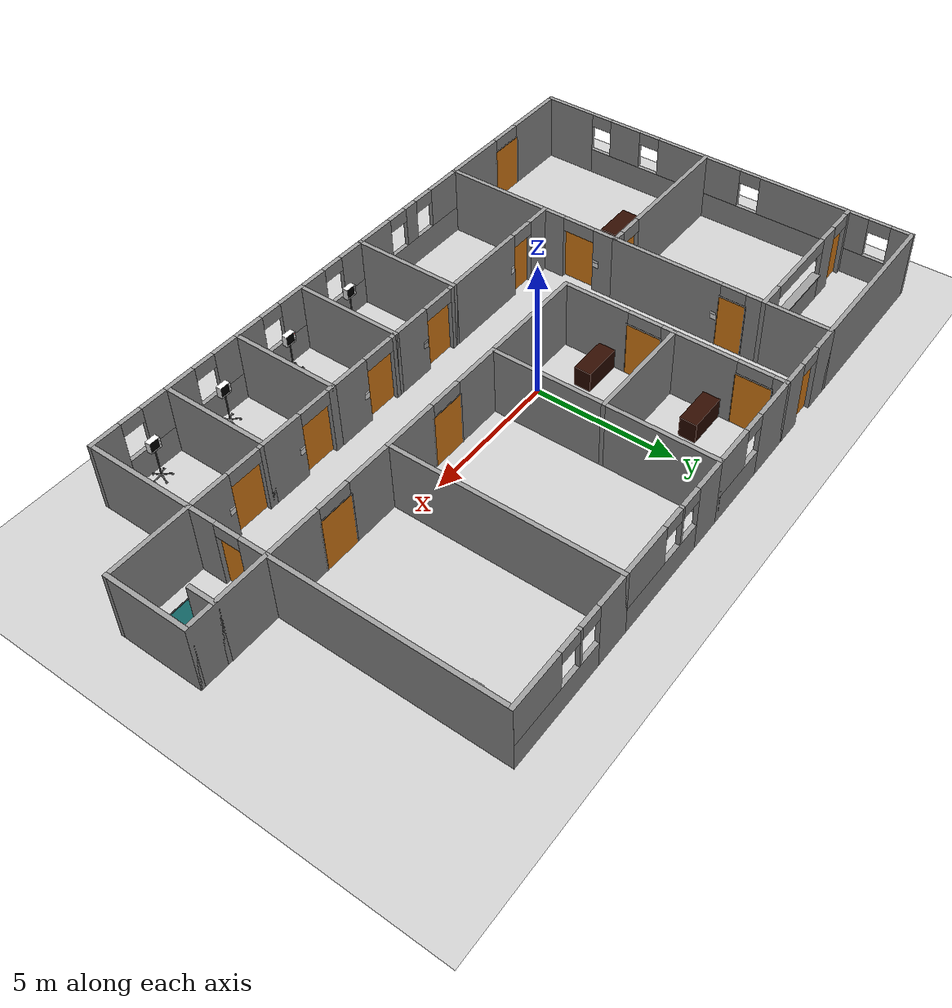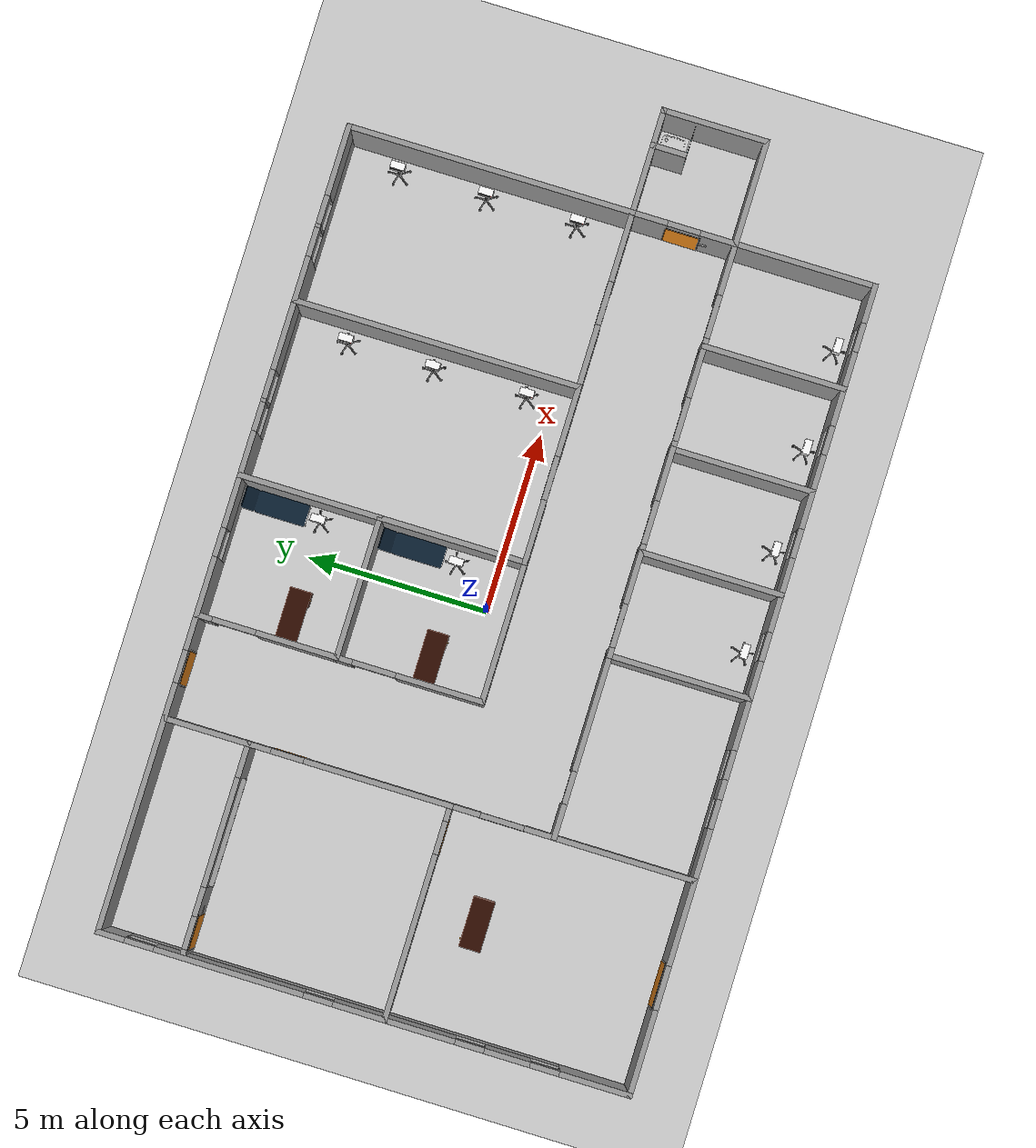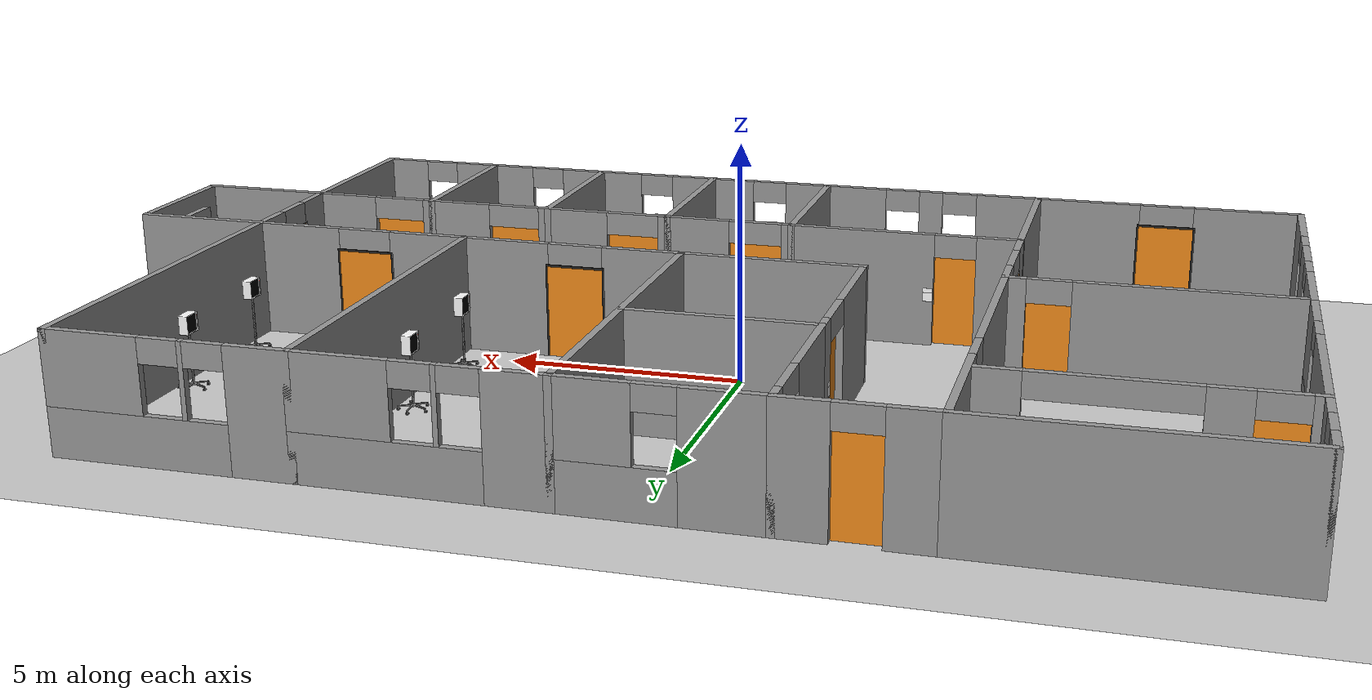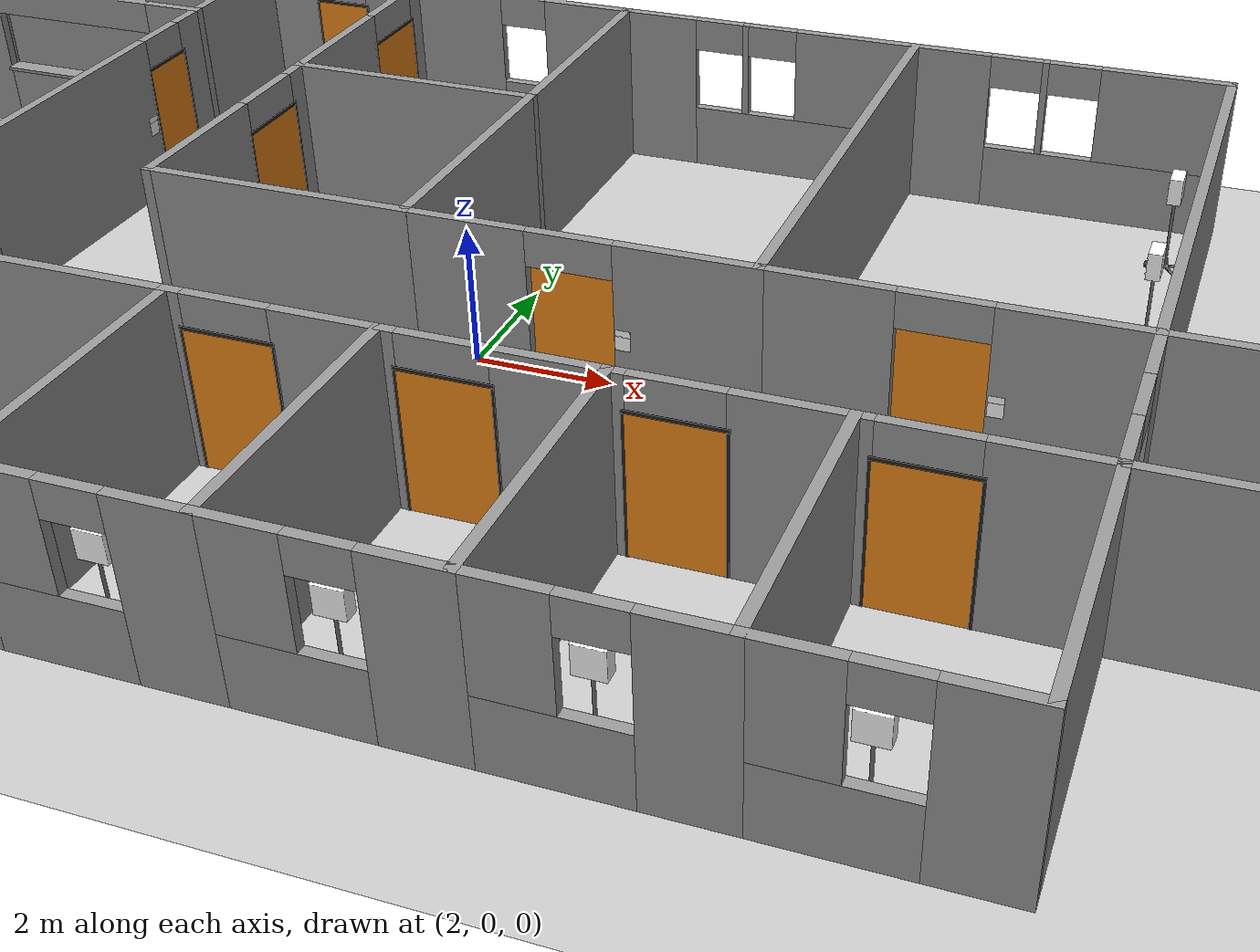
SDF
<sdf version="1.6">
 <world name="default">
  <light name="sun" type="directional">
   <pose>0 0 10 0 -0 0</pose>
   <diffuse>0.8 0.8 0.8 1</diffuse>
   <specular>0.1 0.1 0.1 1</specular>
   <attenuation>
    <range>1000</range>
    <constant>0.9</constant>
    <linear>0.01</linear>
    <quadratic>0.001</quadratic>
   </attenuation>
   <direction>-0.5 0.5 -1</direction>
  </light>
  <model name="ground_plane">
   <static>1</static>
   <link name="link">
    <collision name="collision">
     <geometry><plane><normal>0 0 1</normal><size>100 100</size></plane></geometry>
     <surface><friction><ode><mu>100</mu><mu2>50</mu2></ode></friction></surface>
    </collision>
    <visual name="visual">
     <cast_shadows>0</cast_shadows>
     <geometry><plane><normal>0 0 1</normal><size>100 100</size></plane></geometry>
     <material>
      <script><uri>file://media/materials/scripts/gazebo.material</uri><name>Gazebo/Grey</name></script>
     </material>
    </visual>
   </link>
  </model>
  <gravity>0 0 -9.8</gravity>
  <magnetic_field>6e-06 2.3e-05 -4.2e-05</magnetic_field>
  <atmosphere type="adiabatic"/>
  <physics name="default_physics" default="0" type="ode">
   <max_step_size>0.001</max_step_size>
   <real_time_factor>1</real_time_factor>
   <real_time_update_rate>1000</real_time_update_rate>
  </physics>
  <scene><ambient>0.4 0.4 0.4 1</ambient><background>0.7 0.7 0.7 1</background><shadows>1</shadows></scene>
  <spherical_coordinates>
   <surface_model>EARTH_WGS84</surface_model>
   <latitude_deg>0</latitude_deg>
   <longitude_deg>0</longitude_deg>
   <elevation>0</elevation>
   <heading_deg>0</heading_deg>
  </spherical_coordinates>
  <audio><device>default</device></audio>
  <model name="vitals_monitor">
   <static>1</static>
   <link name="vitals_monitor">
    <collision name="vitals_monitor">
     <geometry><mesh><uri>model://vitals_monitor/meshes/model.dae</uri></mesh></geometry>
    </collision>
    <visual name="vitals_monitor_mesh">
     <geometry><mesh><uri>model://vitals_monitor/meshes/model.dae</uri></mesh></geometry>
    </visual>
   </link>
   <pose>9.47829 -6.89873 0 0 -0 3.14159</pose>
  </model>
  <model name="vitals_monitor_clone">
   <static>1</static>
   <link name="vitals_monitor">
    <collision name="vitals_monitor">
     <geometry><mesh><uri>model://vitals_monitor/meshes/model.dae</uri></mesh></geometry>
    </collision>
    <visual name="vitals_monitor_mesh">
     <geometry><mesh><uri>model://vitals_monitor/meshes/model.dae</uri></mesh></geometry>
    </visual>
   </link>
   <pose>6.64162 -6.89863 0 0 -0 3.14159</pose>
  </model>
  <model name="vitals_monitor_clone_0">
   <static>1</static>
   <link name="vitals_monitor">
    <collision name="vitals_monitor">
     <geometry><mesh><uri>model://vitals_monitor/meshes/model.dae</uri></mesh></geometry>
    </collision>
    <visual name="vitals_monitor_mesh">
     <geometry><mesh><uri>model://vitals_monitor/meshes/model.dae</uri></mesh></geometry>
    </visual>
   </link>
   <pose>3.79191 -6.89962 0 0 -0 3.14159</pose>
  </model>
  <model name="vitals_monitor_clone_1">
   <static>1</static>
   <link name="vitals_monitor">
    <collision name="vitals_monitor">
     <geometry><mesh><uri>model://vitals_monitor/meshes/model.dae</uri></mesh></geometry>
    </collision>
    <visual name="vitals_monitor_mesh">
     <geometry><mesh><uri>model://vitals_monitor/meshes/model.dae</uri></mesh></geometry>
    </visual>
   </link>
   <pose>0.94132 -6.89183 0 0 -0 3.14159</pose>
  </model>
  <model name="vitals_monitor_clone_2">
   <static>1</static>
   <link name="vitals_monitor">
    <collision name="vitals_monitor">
     <geometry><mesh><uri>model://vitals_monitor/meshes/model.dae</uri></mesh></geometry>
    </collision>
    <visual name="vitals_monitor_mesh">
     <geometry><mesh><uri>model://vitals_monitor/meshes/model.dae</uri></mesh></geometry>
    </visual>
   </link>
   <pose>10.6596 5.74993 0 0 0 -1.5708</pose>
  </model>
  <model name="vitals_monitor_clone_2_clone">
   <static>1</static>
   <link name="vitals_monitor">
    <collision name="vitals_monitor">
     <geometry><mesh><uri>model://vitals_monitor/meshes/model.dae</uri></mesh></geometry>
    </collision>
    <visual name="vitals_monitor_mesh">
     <geometry><mesh><uri>model://vitals_monitor/meshes/model.dae</uri></mesh></geometry>
    </visual>
   </link>
   <pose>10.6882 3.29236 0 0 0 -1.5708</pose>
  </model>
  <model name="vitals_monitor_clone_2_clone_0">
   <static>1</static>
   <link name="vitals_monitor">
    <collision name="vitals_monitor">
     <geometry><mesh><uri>model://vitals_monitor/meshes/model.dae</uri></mesh></geometry>
    </collision>
    <visual name="vitals_monitor_mesh">
     <geometry><mesh><uri>model://vitals_monitor/meshes/model.dae</uri></mesh></geometry>
    </visual>
   </link>
   <pose>10.7026 0.733748 0 0 0 -1.5708</pose>
  </model>
  <model name="vitals_monitor_clone_2_clone_1">
   <static>1</static>
   <link name="vitals_monitor">
    <collision name="vitals_monitor">
     <geometry><mesh><uri>model://vitals_monitor/meshes/model.dae</uri></mesh></geometry>
    </collision>
    <visual name="vitals_monitor_mesh">
     <geometry><mesh><uri>model://vitals_monitor/meshes/model.dae</uri></mesh></geometry>
    </visual>
   </link>
   <pose>5.84678 0.669607 0 0 0 -1.5708</pose>
  </model>
  <model name="vitals_monitor_clone_2_clone_2">
   <static>1</static>
   <link name="vitals_monitor">
    <collision name="vitals_monitor">
     <geometry><mesh><uri>model://vitals_monitor/meshes/model.dae</uri></mesh></geometry>
    </collision>
    <visual name="vitals_monitor_mesh">
     <geometry><mesh><uri>model://vitals_monitor/meshes/model.dae</uri></mesh></geometry>
    </visual>
   </link>
   <pose>5.82137 3.28498 0 0 0 -1.5708</pose>
  </model>
  <model name="vitals_monitor_clone_2_clone_3">
   <static>1</static>
   <link name="vitals_monitor">
    <collision name="vitals_monitor">
     <geometry><mesh><uri>model://vitals_monitor/meshes/model.dae</uri></mesh></geometry>
    </collision>
    <visual name="vitals_monitor_mesh">
     <geometry><mesh><uri>model://vitals_monitor/meshes/model.dae</uri></mesh></geometry>
    </visual>
   </link>
   <pose>5.83292 5.71579 0 0 0 -1.5708</pose>
  </model>
  <model name="three_drawer_desk">
   <static>1</static>
   <link name="three_drawer_desk">
    <collision name="three_drawer_desk">
     <geometry><mesh><uri>model://three_drawer_desk/meshes/model.dae</uri></mesh></geometry>
    </collision>
    <visual name="three_drawer_desk_mesh">
     <geometry><mesh><uri>model://three_drawer_desk/meshes/model.dae</uri></mesh></geometry>
    </visual>
   </link>
   <pose>-1.618 4.9115 0 0 -0 3.14159</pose>
  </model>
  <model name="three_drawer_desk_clone">
   <static>1</static>
   <link name="three_drawer_desk">
    <collision name="three_drawer_desk">
     <geometry><mesh><uri>model://three_drawer_desk/meshes/model.dae</uri></mesh></geometry>
    </collision>
    <visual name="three_drawer_desk_mesh">
     <geometry><mesh><uri>model://three_drawer_desk/meshes/model.dae</uri></mesh></geometry>
    </visual>
   </link>
   <pose>-1.62836 1.05851 0 0 -0 3.14159</pose>
  </model>
  <model name="medical_couch">
   <static>1</static>
   <link name="medical_couch">
    <collision name="medical_couch">
     <geometry><mesh><uri>model://medical_couch/meshes/model.dae</uri></mesh></geometry>
    </collision>
    <visual name="medical_couch_mesh">
     <geometry><mesh><uri>model://medical_couch/meshes/model.dae</uri></mesh></geometry>
    </visual>
   </link>
   <pose>1.03141 6.05659 0 0 -0 3.14159</pose>
  </model>
  <model name="medical_couch_clone">
   <static>1</static>
   <link name="medical_couch">
    <collision name="medical_couch">
     <geometry><mesh><uri>model://medical_couch/meshes/model.dae</uri></mesh></geometry>
    </collision>
    <visual name="medical_couch_mesh">
     <geometry><mesh><uri>model://medical_couch/meshes/model.dae</uri></mesh></geometry>
    </visual>
   </link>
   <pose>1.03641 2.21268 0 0 -0 3.14159</pose>
  </model>
  <model name="vitals_monitor_clone_2_clone_3_clone">
   <static>1</static>
   <link name="vitals_monitor">
    <collision name="vitals_monitor">
     <geometry><mesh><uri>model://vitals_monitor/meshes/model.dae</uri></mesh></geometry>
    </collision>
    <visual name="vitals_monitor_mesh">
     <geometry><mesh><uri>model://vitals_monitor/meshes/model.dae</uri></mesh></geometry>
    </visual>
   </link>
   <pose>0.995211 4.99575 0 0 0 -1.5708</pose>
  </model>
  <model name="vitals_monitor_clone_2_clone_3_clone_0">
   <static>1</static>
   <link name="vitals_monitor">
    <collision name="vitals_monitor">
     <geometry><mesh><uri>model://vitals_monitor/meshes/model.dae</uri></mesh></geometry>
    </collision>
    <visual name="vitals_monitor_mesh">
     <geometry><mesh><uri>model://vitals_monitor/meshes/model.dae</uri></mesh></geometry>
    </visual>
   </link>
   <pose>0.989105 1.14447 0 0 0 -1.5708</pose>
  </model>
  <model name="three_drawer_desk_clone_0">
   <static>1</static>
   <link name="three_drawer_desk">
    <collision name="three_drawer_desk">
     <geometry><mesh><uri>model://three_drawer_desk/meshes/model.dae</uri></mesh></geometry>
    </collision>
    <visual name="three_drawer_desk_mesh">
     <geometry><mesh><uri>model://three_drawer_desk/meshes/model.dae</uri></mesh></geometry>
    </visual>
   </link>
   <pose>-8.08485 -2.2155 0 0 -0 0</pose>
  </model>
  <model name="room_door">
   <link name="base_link">
    <inertial>
     <pose>0 0 1.00051 0 -0 0</pose>
     <mass>2001</mass>
     <inertia><ixx>797.85</ixx><ixy>0</ixy><ixz>0</ixz><iyy>4.0501</iyy><iyz>0</iyz><izz>796.8</izz></inertia>
    </inertial>
    <collision name="base_link_fixed_joint_lump__top_post_collision">
     <pose>0 0 2.025 0 -0 0</pose>
     <geometry><box><size>0.01 1.3 0.05</size></box></geometry>
    </collision>
    <collision name="base_link_fixed_joint_lump__left_post_collision_1">
     <pose>0 -0.63 1 0 -0 0</pose>
     <geometry><box><size>0.01 0.04 2</size></box></geometry>
    </collision>
    <collision name="base_link_fixed_joint_lump__right_post_collision_2">
     <pose>0 0.63 1 0 -0 0</pose>
     <geometry><box><size>0.01 0.04 2</size></box></geometry>
    </collision>
    <visual name="base_link_fixed_joint_lump__top_post_visual">
     <pose>0 0 2.025 0 -0 0</pose>
     <geometry><box><size>0.01 1.3 0.05</size></box></geometry>
     <material>
      <script><name>Gazebo/Black</name><uri>file://media/materials/scripts/gazebo.material</uri></script>
     </material>
    </visual>
    <visual name="base_link_fixed_joint_lump__left_post_visual_1">
     <pose>0 -0.63 1 0 -0 0</pose>
     <geometry><box><size>0.01 0.04 2</size></box></geometry>
     <material>
      <script><name>Gazebo/Black</name><uri>file://media/materials/scripts/gazebo.material</uri></script>
     </material>
    </visual>
    <visual name="base_link_fixed_joint_lump__right_post_visual_2">
     <pose>0 0.63 1 0 -0 0</pose>
     <geometry><box><size>0.01 0.04 2</size></box></geometry>
     <material>
      <script><name>Gazebo/Black</name><uri>file://media/materials/scripts/gazebo.material</uri></script>
     </material>
    </visual>
   </link>
   <link name="door_front">
    <pose>0.005 0.61 1 0 -0 0</pose>
    <inertial>
     <mass>1</mass>
     <inertia><ixx>1</ixx><ixy>0</ixy><ixz>0</ixz><iyy>1</iyy><iyz>0</iyz><izz>1</izz></inertia>
    </inertial>
    <collision name="door_front_collision">
     <pose>-0.005 -0.61 0.005 0 -0 0</pose>
     <geometry><box><size>0.01 1.22 1.99</size></box></geometry>
    </collision>
    <visual name="door_front_visual">
     <pose>-0.005 -0.61 0.005 0 -0 0</pose>
     <geometry><box><size>0.01 1.22 1.99</size></box></geometry>
     <material>
      <script><name>Gazebo/Orange</name><uri>file://media/materials/scripts/gazebo.material</uri></script>
     </material>
    </visual>
   </link>
   <joint name="door_front_to_right_post" type="revolute">
    <child>door_front</child>
    <parent>base_link</parent>
    <axis>
     <xyz>0 0 1</xyz>
     <limit><lower>0</lower><upper>3.14</upper><effort>1000</effort><velocity>100</velocity></limit>
     <dynamics>
      <damping>0.5</damping>
      <friction>0</friction>
      <spring_reference>0</spring_reference>
      <spring_stiffness>0</spring_stiffness>
     </dynamics>
     <use_parent_model_frame>0</use_parent_model_frame>
    </axis>
   </joint>
   <pose>-5.34333 -2.04893 -0 -1e-06 -0 3.14133</pose>
  </model>
  <model name="room_door_0">
   <link name="base_link">
    <inertial>
     <pose>0 0 1.00051 0 -0 0</pose>
     <mass>2001</mass>
     <inertia><ixx>464.85</ixx><ixy>0</ixy><ixz>0</ixz><iyy>4.0501</iyy><iyz>0</iyz><izz>463.8</izz></inertia>
    </inertial>
    <collision name="base_link_fixed_joint_lump__top_post_collision">
     <pose>0 0 2.025 0 -0 0</pose>
     <geometry><box><size>0.01 1 0.05</size></box></geometry>
    </collision>
    <collision name="base_link_fixed_joint_lump__left_post_collision_1">
     <pose>0 -0.48 1 0 -0 0</pose>
     <geometry><box><size>0.01 0.04 2</size></box></geometry>
    </collision>
    <collision name="base_link_fixed_joint_lump__right_post_collision_2">
     <pose>0 0.48 1 0 -0 0</pose>
     <geometry><box><size>0.01 0.04 2</size></box></geometry>
    </collision>
    <visual name="base_link_fixed_joint_lump__top_post_visual">
     <pose>0 0 2.025 0 -0 0</pose>
     <geometry><box><size>0.01 1 0.05</size></box></geometry>
     <material>
      <script><name>Gazebo/Black</name><uri>file://media/materials/scripts/gazebo.material</uri></script>
     </material>
    </visual>
    <visual name="base_link_fixed_joint_lump__left_post_visual_1">
     <pose>0 -0.48 1 0 -0 0</pose>
     <geometry><box><size>0.01 0.04 2</size></box></geometry>
     <material>
      <script><name>Gazebo/Black</name><uri>file://media/materials/scripts/gazebo.material</uri></script>
     </material>
    </visual>
    <visual name="base_link_fixed_joint_lump__right_post_visual_2">
     <pose>0 0.48 1 0 -0 0</pose>
     <geometry><box><size>0.01 0.04 2</size></box></geometry>
     <material>
      <script><name>Gazebo/Black</name><uri>file://media/materials/scripts/gazebo.material</uri></script>
     </material>
    </visual>
   </link>
   <link name="door_front">
    <pose>0.005 -0.46 1 0 -0 0</pose>
    <inertial>
     <mass>1</mass>
     <inertia><ixx>1</ixx><ixy>0</ixy><ixz>0</ixz><iyy>1</iyy><iyz>0</iyz><izz>1</izz></inertia>
    </inertial>
    <collision name="door_front_collision">
     <pose>-0.005 0.46 0.005 0 -0 0</pose>
     <geometry><box><size>0.01 0.92 1.99</size></box></geometry>
    </collision>
    <visual name="door_front_visual">
     <pose>-0.005 0.46 0.005 0 -0 0</pose>
     <geometry><box><size>0.01 0.92 1.99</size></box></geometry>
     <material>
      <script><name>Gazebo/Orange</name><uri>file://media/materials/scripts/gazebo.material</uri></script>
     </material>
    </visual>
   </link>
   <joint name="door_front_to_left_post" type="revolute">
    <child>door_front</child>
    <parent>base_link</parent>
    <axis>
     <xyz>0 0 1</xyz>
     <limit><lower>-3.14</lower><upper>0</upper><effort>1000</effort><velocity>100</velocity></limit>
     <dynamics>
      <damping>0.5</damping>
      <friction>0</friction>
      <spring_reference>0</spring_reference>
      <spring_stiffness>0</spring_stiffness>
     </dynamics>
     <use_parent_model_frame>0</use_parent_model_frame>
    </axis>
   </joint>
   <pose>-6.1318 -0.700552 -0 1e-06 -1e-06 -1.57113</pose>
  </model>
  <model name="room_door_0_clone">
   <link name="base_link">
    <inertial>
     <pose>0 0 1.00051 0 -0 0</pose>
     <mass>2001</mass>
     <inertia><ixx>464.85</ixx><ixy>0</ixy><ixz>0</ixz><iyy>4.0501</iyy><iyz>0</iyz><izz>463.8</izz></inertia>
    </inertial>
    <collision name="base_link_fixed_joint_lump__top_post_collision">
     <pose>0 0 2.025 0 -0 0</pose>
     <geometry><box><size>0.01 1 0.05</size></box></geometry>
    </collision>
    <collision name="base_link_fixed_joint_lump__left_post_collision_1">
     <pose>0 -0.48 1 0 -0 0</pose>
     <geometry><box><size>0.01 0.04 2</size></box></geometry>
    </collision>
    <collision name="base_link_fixed_joint_lump__right_post_collision_2">
     <pose>0 0.48 1 0 -0 0</pose>
     <geometry><box><size>0.01 0.04 2</size></box></geometry>
    </collision>
    <visual name="base_link_fixed_joint_lump__top_post_visual">
     <pose>0 0 2.025 0 -0 0</pose>
     <geometry><box><size>0.01 1 0.05</size></box></geometry>
     <material>
      <script><name>Gazebo/Black</name><uri>file://media/materials/scripts/gazebo.material</uri></script>
     </material>
    </visual>
    <visual name="base_link_fixed_joint_lump__left_post_visual_1">
     <pose>0 -0.48 1 0 -0 0</pose>
     <geometry><box><size>0.01 0.04 2</size></box></geometry>
     <material>
      <script><name>Gazebo/Black</name><uri>file://media/materials/scripts/gazebo.material</uri></script>
     </material>
    </visual>
    <visual name="base_link_fixed_joint_lump__right_post_visual_2">
     <pose>0 0.48 1 0 -0 0</pose>
     <geometry><box><size>0.01 0.04 2</size></box></geometry>
     <material>
      <script><name>Gazebo/Black</name><uri>file://media/materials/scripts/gazebo.material</uri></script>
     </material>
    </visual>
   </link>
   <link name="door_front">
    <pose>0.005 -0.46 1 0 -0 0</pose>
    <inertial>
     <mass>1</mass>
     <inertia><ixx>1</ixx><ixy>0</ixy><ixz>0</ixz><iyy>1</iyy><iyz>0</iyz><izz>1</izz></inertia>
    </inertial>
    <collision name="door_front_collision">
     <pose>-0.005 0.46 0.005 0 -0 0</pose>
     <geometry><box><size>0.01 0.92 1.99</size></box></geometry>
    </collision>
    <visual name="door_front_visual">
     <pose>-0.005 0.46 0.005 0 -0 0</pose>
     <geometry><box><size>0.01 0.92 1.99</size></box></geometry>
     <material>
      <script><name>Gazebo/Orange</name><uri>file://media/materials/scripts/gazebo.material</uri></script>
     </material>
    </visual>
   </link>
   <joint name="door_front_to_left_post" type="revolute">
    <child>door_front</child>
    <parent>base_link</parent>
    <axis>
     <xyz>0 0 1</xyz>
     <limit><lower>-3.14</lower><upper>0</upper><effort>1000</effort><velocity>100</velocity></limit>
     <dynamics>
      <damping>0.5</damping>
      <friction>0</friction>
      <spring_reference>0</spring_reference>
      <spring_stiffness>0</spring_stiffness>
     </dynamics>
     <use_parent_model_frame>0</use_parent_model_frame>
    </axis>
   </joint>
   <pose>-10.4433 4.84956 -0 1e-06 -1e-06 -1.57097</pose>
  </model>
  <model name="room_door_1">
   <link name="base_link">
    <inertial>
     <pose>0 0 1.00051 0 -0 0</pose>
     <mass>2001</mass>
     <inertia><ixx>464.85</ixx><ixy>0</ixy><ixz>0</ixz><iyy>4.0501</iyy><iyz>0</iyz><izz>463.8</izz></inertia>
    </inertial>
    <collision name="base_link_fixed_joint_lump__top_post_collision">
     <pose>0 0 2.025 0 -0 0</pose>
     <geometry><box><size>0.01 1 0.05</size></box></geometry>
    </collision>
    <collision name="base_link_fixed_joint_lump__left_post_collision_1">
     <pose>0 -0.48 1 0 -0 0</pose>
     <geometry><box><size>0.01 0.04 2</size></box></geometry>
    </collision>
    <collision name="base_link_fixed_joint_lump__right_post_collision_2">
     <pose>0 0.48 1 0 -0 0</pose>
     <geometry><box><size>0.01 0.04 2</size></box></geometry>
    </collision>
    <visual name="base_link_fixed_joint_lump__top_post_visual">
     <pose>0 0 2.025 0 -0 0</pose>
     <geometry><box><size>0.01 1 0.05</size></box></geometry>
     <material>
      <script><name>Gazebo/Black</name><uri>file://media/materials/scripts/gazebo.material</uri></script>
     </material>
    </visual>
    <visual name="base_link_fixed_joint_lump__left_post_visual_1">
     <pose>0 -0.48 1 0 -0 0</pose>
     <geometry><box><size>0.01 0.04 2</size></box></geometry>
     <material>
      <script><name>Gazebo/Black</name><uri>file://media/materials/scripts/gazebo.material</uri></script>
     </material>
    </visual>
    <visual name="base_link_fixed_joint_lump__right_post_visual_2">
     <pose>0 0.48 1 0 -0 0</pose>
     <geometry><box><size>0.01 0.04 2</size></box></geometry>
     <material>
      <script><name>Gazebo/Black</name><uri>file://media/materials/scripts/gazebo.material</uri></script>
     </material>
    </visual>
   </link>
   <link name="door_front">
    <pose>0.005 0.46 1 0 -0 0</pose>
    <inertial>
     <mass>1</mass>
     <inertia><ixx>1</ixx><ixy>0</ixy><ixz>0</ixz><iyy>1</iyy><iyz>0</iyz><izz>1</izz></inertia>
    </inertial>
    <collision name="door_front_collision">
     <pose>-0.005 -0.46 0.005 0 -0 0</pose>
     <geometry><box><size>0.01 0.92 1.99</size></box></geometry>
    </collision>
    <visual name="door_front_visual">
     <pose>-0.005 -0.46 0.005 0 -0 0</pose>
     <geometry><box><size>0.01 0.92 1.99</size></box></geometry>
     <material>
      <script><name>Gazebo/Orange</name><uri>file://media/materials/scripts/gazebo.material</uri></script>
     </material>
    </visual>
   </link>
   <joint name="door_front_to_right_post" type="revolute">
    <child>door_front</child>
    <parent>base_link</parent>
    <axis>
     <xyz>0 0 1</xyz>
     <limit><lower>0</lower><upper>3.14</upper><effort>1000</effort><velocity>100</velocity></limit>
     <dynamics>
      <damping>0.5</damping>
      <friction>0</friction>
      <spring_reference>0</spring_reference>
      <spring_stiffness>0</spring_stiffness>
     </dynamics>
     <use_parent_model_frame>0</use_parent_model_frame>
    </axis>
   </joint>
   <pose>-5.18302 3.85603 -0 -1e-06 -1e-06 0.000145</pose>
  </model>
  <model name="room_door_clone">
   <link name="base_link">
    <inertial>
     <pose>0 0 1.00051 0 -0 0</pose>
     <mass>2001</mass>
     <inertia><ixx>797.85</ixx><ixy>0</ixy><ixz>0</ixz><iyy>4.0501</iyy><iyz>0</iyz><izz>796.8</izz></inertia>
    </inertial>
    <collision name="base_link_fixed_joint_lump__top_post_collision">
     <pose>0 0 2.025 0 -0 0</pose>
     <geometry><box><size>0.01 1.3 0.05</size></box></geometry>
    </collision>
    <collision name="base_link_fixed_joint_lump__left_post_collision_1">
     <pose>0 -0.63 1 0 -0 0</pose>
     <geometry><box><size>0.01 0.04 2</size></box></geometry>
    </collision>
    <collision name="base_link_fixed_joint_lump__right_post_collision_2">
     <pose>0 0.63 1 0 -0 0</pose>
     <geometry><box><size>0.01 0.04 2</size></box></geometry>
    </collision>
    <visual name="base_link_fixed_joint_lump__top_post_visual">
     <pose>0 0 2.025 0 -0 0</pose>
     <geometry><box><size>0.01 1.3 0.05</size></box></geometry>
     <material>
      <script><name>Gazebo/Black</name><uri>file://media/materials/scripts/gazebo.material</uri></script>
     </material>
    </visual>
    <visual name="base_link_fixed_joint_lump__left_post_visual_1">
     <pose>0 -0.63 1 0 -0 0</pose>
     <geometry><box><size>0.01 0.04 2</size></box></geometry>
     <material>
      <script><name>Gazebo/Black</name><uri>file://media/materials/scripts/gazebo.material</uri></script>
     </material>
    </visual>
    <visual name="base_link_fixed_joint_lump__right_post_visual_2">
     <pose>0 0.63 1 0 -0 0</pose>
     <geometry><box><size>0.01 0.04 2</size></box></geometry>
     <material>
      <script><name>Gazebo/Black</name><uri>file://media/materials/scripts/gazebo.material</uri></script>
     </material>
    </visual>
   </link>
   <link name="door_front">
    <pose>0.005 0.61 1 0 -0 0</pose>
    <inertial>
     <mass>1</mass>
     <inertia><ixx>1</ixx><ixy>0</ixy><ixz>0</ixz><iyy>1</iyy><iyz>0</iyz><izz>1</izz></inertia>
    </inertial>
    <collision name="door_front_collision">
     <pose>-0.005 -0.61 0.005 0 -0 0</pose>
     <geometry><box><size>0.01 1.22 1.99</size></box></geometry>
    </collision>
    <visual name="door_front_visual">
     <pose>-0.005 -0.61 0.005 0 -0 0</pose>
     <geometry><box><size>0.01 1.22 1.99</size></box></geometry>
     <material>
      <script><name>Gazebo/Orange</name><uri>file://media/materials/scripts/gazebo.material</uri></script>
     </material>
    </visual>
   </link>
   <joint name="door_front_to_right_post" type="revolute">
    <child>door_front</child>
    <parent>base_link</parent>
    <axis>
     <xyz>0 0 1</xyz>
     <limit><lower>0</lower><upper>3.14</upper><effort>1000</effort><velocity>100</velocity></limit>
     <dynamics>
      <damping>0.5</damping>
      <friction>0</friction>
      <spring_reference>0</spring_reference>
      <spring_stiffness>0</spring_stiffness>
     </dynamics>
     <use_parent_model_frame>0</use_parent_model_frame>
    </axis>
   </joint>
   <pose>-2.33298 6.2017 -3e-06 -5e-06 1e-06 -0.000148</pose>
  </model>
  <model name="room_door_clone_clone">
   <link name="base_link">
    <inertial>
     <pose>0 0 1.00051 0 -0 0</pose>
     <mass>2001</mass>
     <inertia><ixx>797.85</ixx><ixy>0</ixy><ixz>0</ixz><iyy>4.0501</iyy><iyz>0</iyz><izz>796.8</izz></inertia>
    </inertial>
    <collision name="base_link_fixed_joint_lump__top_post_collision">
     <pose>0 0 2.025 0 -0 0</pose>
     <geometry><box><size>0.01 1.3 0.05</size></box></geometry>
    </collision>
    <collision name="base_link_fixed_joint_lump__left_post_collision_1">
     <pose>0 -0.63 1 0 -0 0</pose>
     <geometry><box><size>0.01 0.04 2</size></box></geometry>
    </collision>
    <collision name="base_link_fixed_joint_lump__right_post_collision_2">
     <pose>0 0.63 1 0 -0 0</pose>
     <geometry><box><size>0.01 0.04 2</size></box></geometry>
    </collision>
    <visual name="base_link_fixed_joint_lump__top_post_visual">
     <pose>0 0 2.025 0 -0 0</pose>
     <geometry><box><size>0.01 1.3 0.05</size></box></geometry>
     <material>
      <script><name>Gazebo/Black</name><uri>file://media/materials/scripts/gazebo.material</uri></script>
     </material>
    </visual>
    <visual name="base_link_fixed_joint_lump__left_post_visual_1">
     <pose>0 -0.63 1 0 -0 0</pose>
     <geometry><box><size>0.01 0.04 2</size></box></geometry>
     <material>
      <script><name>Gazebo/Black</name><uri>file://media/materials/scripts/gazebo.material</uri></script>
     </material>
    </visual>
    <visual name="base_link_fixed_joint_lump__right_post_visual_2">
     <pose>0 0.63 1 0 -0 0</pose>
     <geometry><box><size>0.01 0.04 2</size></box></geometry>
     <material>
      <script><name>Gazebo/Black</name><uri>file://media/materials/scripts/gazebo.material</uri></script>
     </material>
    </visual>
   </link>
   <link name="door_front">
    <pose>0.005 0.61 1 0 -0 0</pose>
    <inertial>
     <mass>1</mass>
     <inertia><ixx>1</ixx><ixy>0</ixy><ixz>0</ixz><iyy>1</iyy><iyz>0</iyz><izz>1</izz></inertia>
    </inertial>
    <collision name="door_front_collision">
     <pose>-0.005 -0.61 0.005 0 -0 0</pose>
     <geometry><box><size>0.01 1.22 1.99</size></box></geometry>
    </collision>
    <visual name="door_front_visual">
     <pose>-0.005 -0.61 0.005 0 -0 0</pose>
     <geometry><box><size>0.01 1.22 1.99</size></box></geometry>
     <material>
      <script><name>Gazebo/Orange</name><uri>file://media/materials/scripts/gazebo.material</uri></script>
     </material>
    </visual>
   </link>
   <joint name="door_front_to_right_post" type="revolute">
    <child>door_front</child>
    <parent>base_link</parent>
    <axis>
     <xyz>0 0 1</xyz>
     <limit><lower>0</lower><upper>3.14</upper><effort>1000</effort><velocity>100</velocity></limit>
     <dynamics>
      <damping>0.5</damping>
      <friction>0</friction>
      <spring_reference>0</spring_reference>
      <spring_stiffness>0</spring_stiffness>
     </dynamics>
     <use_parent_model_frame>0</use_parent_model_frame>
    </axis>
   </joint>
   <pose>-2.33309 2.35384 -5e-06 1e-06 0 3e-06</pose>
  </model>
  <model name="room_door_2">
   <link name="base_link">
    <inertial>
     <pose>0 0 1.00051 0 -0 0</pose>
     <mass>2001</mass>
     <inertia><ixx>464.85</ixx><ixy>0</ixy><ixz>0</ixz><iyy>4.0501</iyy><iyz>0</iyz><izz>463.8</izz></inertia>
    </inertial>
    <collision name="base_link_fixed_joint_lump__top_post_collision">
     <pose>0 0 2.025 0 -0 0</pose>
     <geometry><box><size>0.01 1 0.05</size></box></geometry>
    </collision>
    <collision name="base_link_fixed_joint_lump__left_post_collision_1">
     <pose>0 -0.48 1 0 -0 0</pose>
     <geometry><box><size>0.01 0.04 2</size></box></geometry>
    </collision>
    <collision name="base_link_fixed_joint_lump__right_post_collision_2">
     <pose>0 0.48 1 0 -0 0</pose>
     <geometry><box><size>0.01 0.04 2</size></box></geometry>
    </collision>
    <visual name="base_link_fixed_joint_lump__top_post_visual">
     <pose>0 0 2.025 0 -0 0</pose>
     <geometry><box><size>0.01 1 0.05</size></box></geometry>
     <material>
      <script><name>Gazebo/Black</name><uri>file://media/materials/scripts/gazebo.material</uri></script>
     </material>
    </visual>
    <visual name="base_link_fixed_joint_lump__left_post_visual_1">
     <pose>0 -0.48 1 0 -0 0</pose>
     <geometry><box><size>0.01 0.04 2</size></box></geometry>
     <material>
      <script><name>Gazebo/Black</name><uri>file://media/materials/scripts/gazebo.material</uri></script>
     </material>
    </visual>
    <visual name="base_link_fixed_joint_lump__right_post_visual_2">
     <pose>0 0.48 1 0 -0 0</pose>
     <geometry><box><size>0.01 0.04 2</size></box></geometry>
     <material>
      <script><name>Gazebo/Black</name><uri>file://media/materials/scripts/gazebo.material</uri></script>
     </material>
    </visual>
   </link>
   <link name="door_front">
    <pose>0.005 0.46 1 0 -0 0</pose>
    <inertial>
     <mass>1</mass>
     <inertia><ixx>1</ixx><ixy>0</ixy><ixz>0</ixz><iyy>1</iyy><iyz>0</iyz><izz>1</izz></inertia>
    </inertial>
    <collision name="door_front_collision">
     <pose>-0.005 -0.46 0.005 0 -0 0</pose>
     <geometry><box><size>0.01 0.92 1.99</size></box></geometry>
    </collision>
    <visual name="door_front_visual">
     <pose>-0.005 -0.46 0.005 0 -0 0</pose>
     <geometry><box><size>0.01 0.92 1.99</size></box></geometry>
     <material>
      <script><name>Gazebo/Orange</name><uri>file://media/materials/scripts/gazebo.material</uri></script>
     </material>
    </visual>
   </link>
   <joint name="door_front_to_right_post" type="revolute">
    <child>door_front</child>
    <parent>base_link</parent>
    <axis>
     <xyz>0 0 1</xyz>
     <limit><lower>0</lower><upper>3.14</upper><effort>1000</effort><velocity>100</velocity></limit>
     <dynamics>
      <damping>0.5</damping>
      <friction>0</friction>
      <spring_reference>0</spring_reference>
      <spring_stiffness>0</spring_stiffness>
     </dynamics>
     <use_parent_model_frame>0</use_parent_model_frame>
    </axis>
   </joint>
   <pose>-3.88747 -3.55038 -0 1e-06 1e-06 -1.57069</pose>
  </model>
  <model name="room_door_3">
   <link name="base_link">
    <inertial>
     <pose>0 0 1.00051 0 -0 0</pose>
     <mass>2001</mass>
     <inertia><ixx>797.85</ixx><ixy>0</ixy><ixz>0</ixz><iyy>4.0501</iyy><iyz>0</iyz><izz>796.8</izz></inertia>
    </inertial>
    <collision name="base_link_fixed_joint_lump__top_post_collision">
     <pose>0 0 2.025 0 -0 0</pose>
     <geometry><box><size>0.01 1.3 0.05</size></box></geometry>
    </collision>
    <collision name="base_link_fixed_joint_lump__left_post_collision_1">
     <pose>0 -0.63 1 0 -0 0</pose>
     <geometry><box><size>0.01 0.04 2</size></box></geometry>
    </collision>
    <collision name="base_link_fixed_joint_lump__right_post_collision_2">
     <pose>0 0.63 1 0 -0 0</pose>
     <geometry><box><size>0.01 0.04 2</size></box></geometry>
    </collision>
    <visual name="base_link_fixed_joint_lump__top_post_visual">
     <pose>0 0 2.025 0 -0 0</pose>
     <geometry><box><size>0.01 1.3 0.05</size></box></geometry>
     <material>
      <script><name>Gazebo/Black</name><uri>file://media/materials/scripts/gazebo.material</uri></script>
     </material>
    </visual>
    <visual name="base_link_fixed_joint_lump__left_post_visual_1">
     <pose>0 -0.63 1 0 -0 0</pose>
     <geometry><box><size>0.01 0.04 2</size></box></geometry>
     <material>
      <script><name>Gazebo/Black</name><uri>file://media/materials/scripts/gazebo.material</uri></script>
     </material>
    </visual>
    <visual name="base_link_fixed_joint_lump__right_post_visual_2">
     <pose>0 0.63 1 0 -0 0</pose>
     <geometry><box><size>0.01 0.04 2</size></box></geometry>
     <material>
      <script><name>Gazebo/Black</name><uri>file://media/materials/scripts/gazebo.material</uri></script>
     </material>
    </visual>
   </link>
   <link name="door_front">
    <pose>0.005 -0.61 1 0 -0 0</pose>
    <inertial>
     <mass>1</mass>
     <inertia><ixx>1</ixx><ixy>0</ixy><ixz>0</ixz><iyy>1</iyy><iyz>0</iyz><izz>1</izz></inertia>
    </inertial>
    <collision name="door_front_collision">
     <pose>-0.005 0.61 0.005 0 -0 0</pose>
     <geometry><box><size>0.01 1.22 1.99</size></box></geometry>
    </collision>
    <visual name="door_front_visual">
     <pose>-0.005 0.61 0.005 0 -0 0</pose>
     <geometry><box><size>0.01 1.22 1.99</size></box></geometry>
     <material>
      <script><name>Gazebo/Orange</name><uri>file://media/materials/scripts/gazebo.material</uri></script>
     </material>
    </visual>
   </link>
   <joint name="door_front_to_left_post" type="revolute">
    <child>door_front</child>
    <parent>base_link</parent>
    <axis>
     <xyz>0 0 1</xyz>
     <limit><lower>-3.14</lower><upper>0</upper><effort>1000</effort><velocity>100</velocity></limit>
     <dynamics>
      <damping>0.5</damping>
      <friction>0</friction>
      <spring_reference>0</spring_reference>
      <spring_stiffness>0</spring_stiffness>
     </dynamics>
     <use_parent_model_frame>0</use_parent_model_frame>
    </axis>
   </joint>
   <pose>0.553159 -3.55062 -1e-06 -1e-06 -0 -1.57102</pose>
  </model>
  <model name="room_door_3_clone">
   <link name="base_link">
    <inertial>
     <pose>0 0 1.00051 0 -0 0</pose>
     <mass>2001</mass>
     <inertia><ixx>797.85</ixx><ixy>0</ixy><ixz>0</ixz><iyy>4.0501</iyy><iyz>0</iyz><izz>796.8</izz></inertia>
    </inertial>
    <collision name="base_link_fixed_joint_lump__top_post_collision">
     <pose>0 0 2.025 0 -0 0</pose>
     <geometry><box><size>0.01 1.3 0.05</size></box></geometry>
    </collision>
    <collision name="base_link_fixed_joint_lump__left_post_collision_1">
     <pose>0 -0.63 1 0 -0 0</pose>
     <geometry><box><size>0.01 0.04 2</size></box></geometry>
    </collision>
    <collision name="base_link_fixed_joint_lump__right_post_collision_2">
     <pose>0 0.63 1 0 -0 0</pose>
     <geometry><box><size>0.01 0.04 2</size></box></geometry>
    </collision>
    <visual name="base_link_fixed_joint_lump__top_post_visual">
     <pose>0 0 2.025 0 -0 0</pose>
     <geometry><box><size>0.01 1.3 0.05</size></box></geometry>
     <material>
      <script><name>Gazebo/Black</name><uri>file://media/materials/scripts/gazebo.material</uri></script>
     </material>
    </visual>
    <visual name="base_link_fixed_joint_lump__left_post_visual_1">
     <pose>0 -0.63 1 0 -0 0</pose>
     <geometry><box><size>0.01 0.04 2</size></box></geometry>
     <material>
      <script><name>Gazebo/Black</name><uri>file://media/materials/scripts/gazebo.material</uri></script>
     </material>
    </visual>
    <visual name="base_link_fixed_joint_lump__right_post_visual_2">
     <pose>0 0.63 1 0 -0 0</pose>
     <geometry><box><size>0.01 0.04 2</size></box></geometry>
     <material>
      <script><name>Gazebo/Black</name><uri>file://media/materials/scripts/gazebo.material</uri></script>
     </material>
    </visual>
   </link>
   <link name="door_front">
    <pose>0.005 -0.61 1 0 -0 0</pose>
    <inertial>
     <mass>1</mass>
     <inertia><ixx>1</ixx><ixy>0</ixy><ixz>0</ixz><iyy>1</iyy><iyz>0</iyz><izz>1</izz></inertia>
    </inertial>
    <collision name="door_front_collision">
     <pose>-0.005 0.61 0.005 0 -0 0</pose>
     <geometry><box><size>0.01 1.22 1.99</size></box></geometry>
    </collision>
    <visual name="door_front_visual">
     <pose>-0.005 0.61 0.005 0 -0 0</pose>
     <geometry><box><size>0.01 1.22 1.99</size></box></geometry>
     <material>
      <script><name>Gazebo/Orange</name><uri>file://media/materials/scripts/gazebo.material</uri></script>
     </material>
    </visual>
   </link>
   <joint name="door_front_to_left_post" type="revolute">
    <child>door_front</child>
    <parent>base_link</parent>
    <axis>
     <xyz>0 0 1</xyz>
     <limit><lower>-3.14</lower><upper>0</upper><effort>1000</effort><velocity>100</velocity></limit>
     <dynamics>
      <damping>0.5</damping>
      <friction>0</friction>
      <spring_reference>0</spring_reference>
      <spring_stiffness>0</spring_stiffness>
     </dynamics>
     <use_parent_model_frame>0</use_parent_model_frame>
    </axis>
   </joint>
   <pose>3.41388 -3.55031 -1e-06 1e-06 -0 -1.5708</pose>
  </model>
  <model name="room_door_3_clone_clone">
   <link name="base_link">
    <inertial>
     <pose>0 0 1.00051 0 -0 0</pose>
     <mass>2001</mass>
     <inertia><ixx>797.85</ixx><ixy>0</ixy><ixz>0</ixz><iyy>4.0501</iyy><iyz>0</iyz><izz>796.8</izz></inertia>
    </inertial>
    <collision name="base_link_fixed_joint_lump__top_post_collision">
     <pose>0 0 2.025 0 -0 0</pose>
     <geometry><box><size>0.01 1.3 0.05</size></box></geometry>
    </collision>
    <collision name="base_link_fixed_joint_lump__left_post_collision_1">
     <pose>0 -0.63 1 0 -0 0</pose>
     <geometry><box><size>0.01 0.04 2</size></box></geometry>
    </collision>
    <collision name="base_link_fixed_joint_lump__right_post_collision_2">
     <pose>0 0.63 1 0 -0 0</pose>
     <geometry><box><size>0.01 0.04 2</size></box></geometry>
    </collision>
    <visual name="base_link_fixed_joint_lump__top_post_visual">
     <pose>0 0 2.025 0 -0 0</pose>
     <geometry><box><size>0.01 1.3 0.05</size></box></geometry>
     <material>
      <script><name>Gazebo/Black</name><uri>file://media/materials/scripts/gazebo.material</uri></script>
     </material>
    </visual>
    <visual name="base_link_fixed_joint_lump__left_post_visual_1">
     <pose>0 -0.63 1 0 -0 0</pose>
     <geometry><box><size>0.01 0.04 2</size></box></geometry>
     <material>
      <script><name>Gazebo/Black</name><uri>file://media/materials/scripts/gazebo.material</uri></script>
     </material>
    </visual>
    <visual name="base_link_fixed_joint_lump__right_post_visual_2">
     <pose>0 0.63 1 0 -0 0</pose>
     <geometry><box><size>0.01 0.04 2</size></box></geometry>
     <material>
      <script><name>Gazebo/Black</name><uri>file://media/materials/scripts/gazebo.material</uri></script>
     </material>
    </visual>
   </link>
   <link name="door_front">
    <pose>0.005 -0.61 1 0 -0 0</pose>
    <inertial>
     <mass>1</mass>
     <inertia><ixx>1</ixx><ixy>0</ixy><ixz>0</ixz><iyy>1</iyy><iyz>0</iyz><izz>1</izz></inertia>
    </inertial>
    <collision name="door_front_collision">
     <pose>-0.005 0.61 0.005 0 -0 0</pose>
     <geometry><box><size>0.01 1.22 1.99</size></box></geometry>
    </collision>
    <visual name="door_front_visual">
     <pose>-0.005 0.61 0.005 0 -0 0</pose>
     <geometry><box><size>0.01 1.22 1.99</size></box></geometry>
     <material>
      <script><name>Gazebo/Orange</name><uri>file://media/materials/scripts/gazebo.material</uri></script>
     </material>
    </visual>
   </link>
   <joint name="door_front_to_left_post" type="revolute">
    <child>door_front</child>
    <parent>base_link</parent>
    <axis>
     <xyz>0 0 1</xyz>
     <limit><lower>-3.14</lower><upper>0</upper><effort>1000</effort><velocity>100</velocity></limit>
     <dynamics>
      <damping>0.5</damping>
      <friction>0</friction>
      <spring_reference>0</spring_reference>
      <spring_stiffness>0</spring_stiffness>
     </dynamics>
     <use_parent_model_frame>0</use_parent_model_frame>
    </axis>
   </joint>
   <pose>6.26096 -3.5504 -2e-06 4e-06 -7e-06 -1.57077</pose>
  </model>
  <model name="room_door_3_clone_clone_0">
   <link name="base_link">
    <inertial>
     <pose>0 0 1.00051 0 -0 0</pose>
     <mass>2001</mass>
     <inertia><ixx>797.85</ixx><ixy>0</ixy><ixz>0</ixz><iyy>4.0501</iyy><iyz>0</iyz><izz>796.8</izz></inertia>
    </inertial>
    <collision name="base_link_fixed_joint_lump__top_post_collision">
     <pose>0 0 2.025 0 -0 0</pose>
     <geometry><box><size>0.01 1.3 0.05</size></box></geometry>
    </collision>
    <collision name="base_link_fixed_joint_lump__left_post_collision_1">
     <pose>0 -0.63 1 0 -0 0</pose>
     <geometry><box><size>0.01 0.04 2</size></box></geometry>
    </collision>
    <collision name="base_link_fixed_joint_lump__right_post_collision_2">
     <pose>0 0.63 1 0 -0 0</pose>
     <geometry><box><size>0.01 0.04 2</size></box></geometry>
    </collision>
    <visual name="base_link_fixed_joint_lump__top_post_visual">
     <pose>0 0 2.025 0 -0 0</pose>
     <geometry><box><size>0.01 1.3 0.05</size></box></geometry>
     <material>
      <script><name>Gazebo/Black</name><uri>file://media/materials/scripts/gazebo.material</uri></script>
     </material>
    </visual>
    <visual name="base_link_fixed_joint_lump__left_post_visual_1">
     <pose>0 -0.63 1 0 -0 0</pose>
     <geometry><box><size>0.01 0.04 2</size></box></geometry>
     <material>
      <script><name>Gazebo/Black</name><uri>file://media/materials/scripts/gazebo.material</uri></script>
     </material>
    </visual>
    <visual name="base_link_fixed_joint_lump__right_post_visual_2">
     <pose>0 0.63 1 0 -0 0</pose>
     <geometry><box><size>0.01 0.04 2</size></box></geometry>
     <material>
      <script><name>Gazebo/Black</name><uri>file://media/materials/scripts/gazebo.material</uri></script>
     </material>
    </visual>
   </link>
   <link name="door_front">
    <pose>0.005 -0.61 1 0 -0 0</pose>
    <inertial>
     <mass>1</mass>
     <inertia><ixx>1</ixx><ixy>0</ixy><ixz>0</ixz><iyy>1</iyy><iyz>0</iyz><izz>1</izz></inertia>
    </inertial>
    <collision name="door_front_collision">
     <pose>-0.005 0.61 0.005 0 -0 0</pose>
     <geometry><box><size>0.01 1.22 1.99</size></box></geometry>
    </collision>
    <visual name="door_front_visual">
     <pose>-0.005 0.61 0.005 0 -0 0</pose>
     <geometry><box><size>0.01 1.22 1.99</size></box></geometry>
     <material>
      <script><name>Gazebo/Orange</name><uri>file://media/materials/scripts/gazebo.material</uri></script>
     </material>
    </visual>
   </link>
   <joint name="door_front_to_left_post" type="revolute">
    <child>door_front</child>
    <parent>base_link</parent>
    <axis>
     <xyz>0 0 1</xyz>
     <limit><lower>-3.14</lower><upper>0</upper><effort>1000</effort><velocity>100</velocity></limit>
     <dynamics>
      <damping>0.5</damping>
      <friction>0</friction>
      <spring_reference>0</spring_reference>
      <spring_stiffness>0</spring_stiffness>
     </dynamics>
     <use_parent_model_frame>0</use_parent_model_frame>
    </axis>
   </joint>
   <pose>9.11377 -3.55071 -1e-06 -1e-06 -0 -1.57102</pose>
  </model>
  <model name="room_door_3_clone_clone_0_clone">
   <link name="base_link">
    <inertial>
     <pose>0 0 1.00051 0 -0 0</pose>
     <mass>2001</mass>
     <inertia><ixx>797.85</ixx><ixy>0</ixy><ixz>0</ixz><iyy>4.0501</iyy><iyz>0</iyz><izz>796.8</izz></inertia>
    </inertial>
    <collision name="base_link_fixed_joint_lump__top_post_collision">
     <pose>0 0 2.025 0 -0 0</pose>
     <geometry><box><size>0.01 1.3 0.05</size></box></geometry>
    </collision>
    <collision name="base_link_fixed_joint_lump__left_post_collision_1">
     <pose>0 -0.63 1 0 -0 0</pose>
     <geometry><box><size>0.01 0.04 2</size></box></geometry>
    </collision>
    <collision name="base_link_fixed_joint_lump__right_post_collision_2">
     <pose>0 0.63 1 0 -0 0</pose>
     <geometry><box><size>0.01 0.04 2</size></box></geometry>
    </collision>
    <visual name="base_link_fixed_joint_lump__top_post_visual">
     <pose>0 0 2.025 0 -0 0</pose>
     <geometry><box><size>0.01 1.3 0.05</size></box></geometry>
     <material>
      <script><name>Gazebo/Black</name><uri>file://media/materials/scripts/gazebo.material</uri></script>
     </material>
    </visual>
    <visual name="base_link_fixed_joint_lump__left_post_visual_1">
     <pose>0 -0.63 1 0 -0 0</pose>
     <geometry><box><size>0.01 0.04 2</size></box></geometry>
     <material>
      <script><name>Gazebo/Black</name><uri>file://media/materials/scripts/gazebo.material</uri></script>
     </material>
    </visual>
    <visual name="base_link_fixed_joint_lump__right_post_visual_2">
     <pose>0 0.63 1 0 -0 0</pose>
     <geometry><box><size>0.01 0.04 2</size></box></geometry>
     <material>
      <script><name>Gazebo/Black</name><uri>file://media/materials/scripts/gazebo.material</uri></script>
     </material>
    </visual>
   </link>
   <link name="door_front">
    <pose>0.005 -0.61 1 0 -0 0</pose>
    <inertial>
     <mass>1</mass>
     <inertia><ixx>1</ixx><ixy>0</ixy><ixz>0</ixz><iyy>1</iyy><iyz>0</iyz><izz>1</izz></inertia>
    </inertial>
    <collision name="door_front_collision">
     <pose>-0.005 0.61 0.005 0 -0 0</pose>
     <geometry><box><size>0.01 1.22 1.99</size></box></geometry>
    </collision>
    <visual name="door_front_visual">
     <pose>-0.005 0.61 0.005 0 -0 0</pose>
     <geometry><box><size>0.01 1.22 1.99</size></box></geometry>
     <material>
      <script><name>Gazebo/Orange</name><uri>file://media/materials/scripts/gazebo.material</uri></script>
     </material>
    </visual>
   </link>
   <joint name="door_front_to_left_post" type="revolute">
    <child>door_front</child>
    <parent>base_link</parent>
    <axis>
     <xyz>0 0 1</xyz>
     <limit><lower>-3.14</lower><upper>0</upper><effort>1000</effort><velocity>100</velocity></limit>
     <dynamics>
      <damping>0.5</damping>
      <friction>0</friction>
      <spring_reference>0</spring_reference>
      <spring_stiffness>0</spring_stiffness>
     </dynamics>
     <use_parent_model_frame>0</use_parent_model_frame>
    </axis>
   </joint>
   <pose>8.60531 -0.539945 -5e-06 1e-06 -1e-06 1.57057</pose>
  </model>
  <model name="room_door_3_clone_clone_0_clone_0">
   <link name="base_link">
    <inertial>
     <pose>0 0 1.00051 0 -0 0</pose>
     <mass>2001</mass>
     <inertia><ixx>797.85</ixx><ixy>0</ixy><ixz>0</ixz><iyy>4.0501</iyy><iyz>0</iyz><izz>796.8</izz></inertia>
    </inertial>
    <collision name="base_link_fixed_joint_lump__top_post_collision">
     <pose>0 0 2.025 0 -0 0</pose>
     <geometry><box><size>0.01 1.3 0.05</size></box></geometry>
    </collision>
    <collision name="base_link_fixed_joint_lump__left_post_collision_1">
     <pose>0 -0.63 1 0 -0 0</pose>
     <geometry><box><size>0.01 0.04 2</size></box></geometry>
    </collision>
    <collision name="base_link_fixed_joint_lump__right_post_collision_2">
     <pose>0 0.63 1 0 -0 0</pose>
     <geometry><box><size>0.01 0.04 2</size></box></geometry>
    </collision>
    <visual name="base_link_fixed_joint_lump__top_post_visual">
     <pose>0 0 2.025 0 -0 0</pose>
     <geometry><box><size>0.01 1.3 0.05</size></box></geometry>
     <material>
      <script><name>Gazebo/Black</name><uri>file://media/materials/scripts/gazebo.material</uri></script>
     </material>
    </visual>
    <visual name="base_link_fixed_joint_lump__left_post_visual_1">
     <pose>0 -0.63 1 0 -0 0</pose>
     <geometry><box><size>0.01 0.04 2</size></box></geometry>
     <material>
      <script><name>Gazebo/Black</name><uri>file://media/materials/scripts/gazebo.material</uri></script>
     </material>
    </visual>
    <visual name="base_link_fixed_joint_lump__right_post_visual_2">
     <pose>0 0.63 1 0 -0 0</pose>
     <geometry><box><size>0.01 0.04 2</size></box></geometry>
     <material>
      <script><name>Gazebo/Black</name><uri>file://media/materials/scripts/gazebo.material</uri></script>
     </material>
    </visual>
   </link>
   <link name="door_front">
    <pose>0.005 -0.61 1 0 -0 0</pose>
    <inertial>
     <mass>1</mass>
     <inertia><ixx>1</ixx><ixy>0</ixy><ixz>0</ixz><iyy>1</iyy><iyz>0</iyz><izz>1</izz></inertia>
    </inertial>
    <collision name="door_front_collision">
     <pose>-0.005 0.61 0.005 0 -0 0</pose>
     <geometry><box><size>0.01 1.22 1.99</size></box></geometry>
    </collision>
    <visual name="door_front_visual">
     <pose>-0.005 0.61 0.005 0 -0 0</pose>
     <geometry><box><size>0.01 1.22 1.99</size></box></geometry>
     <material>
      <script><name>Gazebo/Orange</name><uri>file://media/materials/scripts/gazebo.material</uri></script>
     </material>
    </visual>
   </link>
   <joint name="door_front_to_left_post" type="revolute">
    <child>door_front</child>
    <parent>base_link</parent>
    <axis>
     <xyz>0 0 1</xyz>
     <limit><lower>-3.14</lower><upper>0</upper><effort>1000</effort><velocity>100</velocity></limit>
     <dynamics>
      <damping>0.5</damping>
      <friction>0</friction>
      <spring_reference>0</spring_reference>
      <spring_stiffness>0</spring_stiffness>
     </dynamics>
     <use_parent_model_frame>0</use_parent_model_frame>
    </axis>
   </joint>
   <pose>3.76836 -0.540279 -1e-06 1e-06 -1e-06 1.57084</pose>
  </model>
  <model name="room_door_4">
   <link name="base_link">
    <inertial>
     <pose>0 0 1.00051 0 -0 0</pose>
     <mass>2001</mass>
     <inertia><ixx>464.85</ixx><ixy>0</ixy><ixz>0</ixz><iyy>4.0501</iyy><iyz>0</iyz><izz>463.8</izz></inertia>
    </inertial>
    <collision name="base_link_fixed_joint_lump__top_post_collision">
     <pose>0 0 2.025 0 -0 0</pose>
     <geometry><box><size>0.01 1 0.05</size></box></geometry>
    </collision>
    <collision name="base_link_fixed_joint_lump__left_post_collision_1">
     <pose>0 -0.48 1 0 -0 0</pose>
     <geometry><box><size>0.01 0.04 2</size></box></geometry>
    </collision>
    <collision name="base_link_fixed_joint_lump__right_post_collision_2">
     <pose>0 0.48 1 0 -0 0</pose>
     <geometry><box><size>0.01 0.04 2</size></box></geometry>
    </collision>
    <visual name="base_link_fixed_joint_lump__top_post_visual">
     <pose>0 0 2.025 0 -0 0</pose>
     <geometry><box><size>0.01 1 0.05</size></box></geometry>
     <material>
      <script><name>Gazebo/Black</name><uri>file://media/materials/scripts/gazebo.material</uri></script>
     </material>
    </visual>
    <visual name="base_link_fixed_joint_lump__left_post_visual_1">
     <pose>0 -0.48 1 0 -0 0</pose>
     <geometry><box><size>0.01 0.04 2</size></box></geometry>
     <material>
      <script><name>Gazebo/Black</name><uri>file://media/materials/scripts/gazebo.material</uri></script>
     </material>
    </visual>
    <visual name="base_link_fixed_joint_lump__right_post_visual_2">
     <pose>0 0.48 1 0 -0 0</pose>
     <geometry><box><size>0.01 0.04 2</size></box></geometry>
     <material>
      <script><name>Gazebo/Black</name><uri>file://media/materials/scripts/gazebo.material</uri></script>
     </material>
    </visual>
   </link>
   <link name="door_front">
    <pose>0.005 -0.46 1 0 -0 0</pose>
    <inertial>
     <mass>1</mass>
     <inertia><ixx>1</ixx><ixy>0</ixy><ixz>0</ixz><iyy>1</iyy><iyz>0</iyz><izz>1</izz></inertia>
    </inertial>
    <collision name="door_front_collision">
     <pose>-0.005 0.46 0.005 0 -0 0</pose>
     <geometry><box><size>0.01 0.92 1.99</size></box></geometry>
    </collision>
    <visual name="door_front_visual">
     <pose>-0.005 0.46 0.005 0 -0 0</pose>
     <geometry><box><size>0.01 0.92 1.99</size></box></geometry>
     <material>
      <script><name>Gazebo/Orange</name><uri>file://media/materials/scripts/gazebo.material</uri></script>
     </material>
    </visual>
   </link>
   <joint name="door_front_to_left_post" type="revolute">
    <child>door_front</child>
    <parent>base_link</parent>
    <axis>
     <xyz>0 0 1</xyz>
     <limit><lower>-3.14</lower><upper>0</upper><effort>1000</effort><velocity>100</velocity></limit>
     <dynamics>
      <damping>0.5</damping>
      <friction>0</friction>
      <spring_reference>0</spring_reference>
      <spring_stiffness>0</spring_stiffness>
     </dynamics>
     <use_parent_model_frame>0</use_parent_model_frame>
    </axis>
   </joint>
   <pose>-3.83625 7.1492 -0 -1e-06 -1e-06 -1.57132</pose>
  </model>
  <model name="room_door_5">
   <link name="base_link">
    <inertial>
     <pose>0 0 1.00051 0 -0 0</pose>
     <mass>2001</mass>
     <inertia><ixx>464.85</ixx><ixy>0</ixy><ixz>0</ixz><iyy>4.0501</iyy><iyz>0</iyz><izz>463.8</izz></inertia>
    </inertial>
    <collision name="base_link_fixed_joint_lump__top_post_collision">
     <pose>0 0 2.025 0 -0 0</pose>
     <geometry><box><size>0.01 1 0.05</size></box></geometry>
    </collision>
    <collision name="base_link_fixed_joint_lump__left_post_collision_1">
     <pose>0 -0.48 1 0 -0 0</pose>
     <geometry><box><size>0.01 0.04 2</size></box></geometry>
    </collision>
    <collision name="base_link_fixed_joint_lump__right_post_collision_2">
     <pose>0 0.48 1 0 -0 0</pose>
     <geometry><box><size>0.01 0.04 2</size></box></geometry>
    </collision>
    <visual name="base_link_fixed_joint_lump__top_post_visual">
     <pose>0 0 2.025 0 -0 0</pose>
     <geometry><box><size>0.01 1 0.05</size></box></geometry>
     <material>
      <script><name>Gazebo/Black</name><uri>file://media/materials/scripts/gazebo.material</uri></script>
     </material>
    </visual>
    <visual name="base_link_fixed_joint_lump__left_post_visual_1">
     <pose>0 -0.48 1 0 -0 0</pose>
     <geometry><box><size>0.01 0.04 2</size></box></geometry>
     <material>
      <script><name>Gazebo/Black</name><uri>file://media/materials/scripts/gazebo.material</uri></script>
     </material>
    </visual>
    <visual name="base_link_fixed_joint_lump__right_post_visual_2">
     <pose>0 0.48 1 0 -0 0</pose>
     <geometry><box><size>0.01 0.04 2</size></box></geometry>
     <material>
      <script><name>Gazebo/Black</name><uri>file://media/materials/scripts/gazebo.material</uri></script>
     </material>
    </visual>
   </link>
   <link name="door_front">
    <pose>0.005 -0.46 1 0 -0 0</pose>
    <inertial>
     <mass>1</mass>
     <inertia><ixx>1</ixx><ixy>0</ixy><ixz>0</ixz><iyy>1</iyy><iyz>0</iyz><izz>1</izz></inertia>
    </inertial>
    <collision name="door_front_collision">
     <pose>-0.005 0.46 0.005 0 -0 0</pose>
     <geometry><box><size>0.01 0.92 1.99</size></box></geometry>
    </collision>
    <visual name="door_front_visual">
     <pose>-0.005 0.46 0.005 0 -0 0</pose>
     <geometry><box><size>0.01 0.92 1.99</size></box></geometry>
     <material>
      <script><name>Gazebo/Orange</name><uri>file://media/materials/scripts/gazebo.material</uri></script>
     </material>
    </visual>
   </link>
   <joint name="door_front_to_left_post" type="revolute">
    <child>door_front</child>
    <parent>base_link</parent>
    <axis>
     <xyz>0 0 1</xyz>
     <limit><lower>-3.14</lower><upper>0</upper><effort>1000</effort><velocity>100</velocity></limit>
     <dynamics>
      <damping>0.5</damping>
      <friction>0</friction>
      <spring_reference>0</spring_reference>
      <spring_stiffness>0</spring_stiffness>
     </dynamics>
     <use_parent_model_frame>0</use_parent_model_frame>
    </axis>
   </joint>
   <pose>11.0569 -2.04956 -0 0 -0 3.14159</pose>
  </model>
  <model name="room_door_6">
   <link name="base_link">
    <inertial>
     <pose>0 0 1.00051 0 -0 0</pose>
     <mass>2001</mass>
     <inertia><ixx>797.85</ixx><ixy>0</ixy><ixz>0</ixz><iyy>4.0501</iyy><iyz>0</iyz><izz>796.8</izz></inertia>
    </inertial>
    <collision name="base_link_fixed_joint_lump__top_post_collision">
     <pose>0 0 2.025 0 -0 0</pose>
     <geometry><box><size>0.01 1.3 0.05</size></box></geometry>
    </collision>
    <collision name="base_link_fixed_joint_lump__left_post_collision_1">
     <pose>0 -0.63 1 0 -0 0</pose>
     <geometry><box><size>0.01 0.04 2</size></box></geometry>
    </collision>
    <collision name="base_link_fixed_joint_lump__right_post_collision_2">
     <pose>0 0.63 1 0 -0 0</pose>
     <geometry><box><size>0.01 0.04 2</size></box></geometry>
    </collision>
    <visual name="base_link_fixed_joint_lump__top_post_visual">
     <pose>0 0 2.025 0 -0 0</pose>
     <geometry><box><size>0.01 1.3 0.05</size></box></geometry>
     <material>
      <script><name>Gazebo/Black</name><uri>file://media/materials/scripts/gazebo.material</uri></script>
     </material>
    </visual>
    <visual name="base_link_fixed_joint_lump__left_post_visual_1">
     <pose>0 -0.63 1 0 -0 0</pose>
     <geometry><box><size>0.01 0.04 2</size></box></geometry>
     <material>
      <script><name>Gazebo/Black</name><uri>file://media/materials/scripts/gazebo.material</uri></script>
     </material>
    </visual>
    <visual name="base_link_fixed_joint_lump__right_post_visual_2">
     <pose>0 0.63 1 0 -0 0</pose>
     <geometry><box><size>0.01 0.04 2</size></box></geometry>
     <material>
      <script><name>Gazebo/Black</name><uri>file://media/materials/scripts/gazebo.material</uri></script>
     </material>
    </visual>
   </link>
   <link name="door_front">
    <pose>0.005 0.61 1 0 -0 0</pose>
    <inertial>
     <mass>1</mass>
     <inertia><ixx>1</ixx><ixy>0</ixy><ixz>0</ixz><iyy>1</iyy><iyz>0</iyz><izz>1</izz></inertia>
    </inertial>
    <collision name="door_front_collision">
     <pose>-0.005 -0.61 0.005 0 -0 0</pose>
     <geometry><box><size>0.01 1.22 1.99</size></box></geometry>
    </collision>
    <visual name="door_front_visual">
     <pose>-0.005 -0.61 0.005 0 -0 0</pose>
     <geometry><box><size>0.01 1.22 1.99</size></box></geometry>
     <material>
      <script><name>Gazebo/Orange</name><uri>file://media/materials/scripts/gazebo.material</uri></script>
     </material>
    </visual>
   </link>
   <joint name="door_front_to_right_post" type="revolute">
    <child>door_front</child>
    <parent>base_link</parent>
    <axis>
     <xyz>0 0 1</xyz>
     <limit><lower>0</lower><upper>3.14</upper><effort>1000</effort><velocity>100</velocity></limit>
     <dynamics>
      <damping>0.5</damping>
      <friction>0</friction>
      <spring_reference>0</spring_reference>
      <spring_stiffness>0</spring_stiffness>
     </dynamics>
     <use_parent_model_frame>0</use_parent_model_frame>
    </axis>
   </joint>
   <pose>-8.19194 -7.24015 -5e-06 1e-06 1e-06 1.57065</pose>
  </model>
  <model name="info_plate">
   <static>1</static>
   <link name="info_plate">
    <collision name="info_plate">
     <pose>0 0 0.1485 0 -0 0</pose>
     <geometry><box><size>0.001 0.21 0.297</size></box></geometry>
    </collision>
    <visual name="info_plate_upper">
     <pose>0 0 0.2485 0 -0 0</pose>
     <geometry><box><size>0.001 0.21 0.097</size></box></geometry>
     <material>
      <script>
       <uri>model://info_plate/materials/scripts</uri>
       <uri>model://info_plate/materials/textures</uri>
       <name>Room/S1</name>
       <name>__default__</name>
      </script>
     </material>
    </visual>
    <visual name="info_plate_lower">
     <pose>0 0 0.105 0 -0 0</pose>
     <geometry><box><size>0.001 0.21 0.21</size></box></geometry>
     <material>
      <script>
       <uri>model://info_plate/materials/scripts</uri>
       <uri>model://info_plate/materials/textures</uri>
       <name>QR_Room/S1</name>
      </script>
     </material>
    </visual>
   </link>
   <pose>1.29234 -3.395 1 0 -0 1.57</pose>
  </model>
  <model name="info_plate_clone">
   <link name="info_plate">
    <inertial>
     <mass>1</mass>
     <inertia><ixx>1</ixx><ixy>0</ixy><ixz>0</ixz><iyy>1</iyy><iyz>0</iyz><izz>1</izz></inertia>
    </inertial>
    <visual name="info_plate_upper">
     <pose>0 0 0.2485 0 -0 0</pose>
     <geometry><box><size>0.001 0.21 0.097</size></box></geometry>
     <material>
      <script>
       <uri>model://info_plate/materials/scripts</uri>
       <uri>model://info_plate/materials/textures</uri>
       <name>Room/S2</name>
       <name>__default__</name>
      </script>
      <shader type="vertex"><normal_map>__default__</normal_map></shader>
      <ambient>1 1 1 1</ambient>
      <diffuse>1 1 1 1</diffuse>
      <specular>0 0 0 1</specular>
      <emissive>0 0 0 1</emissive>
     </material>
    </visual>
    <visual name="info_plate_lower">
     <pose>0 0 0.105 0 -0 0</pose>
     <geometry><box><size>0.001 0.21 0.21</size></box></geometry>
     <material>
      <script>
       <uri>model://info_plate/materials/scripts</uri>
       <uri>model://info_plate/materials/textures</uri>
       <name>QR_Room/S2</name>
      </script>
      <shader type="vertex"><normal_map>__default__</normal_map></shader>
      <ambient>1 1 1 1</ambient>
      <diffuse>1 1 1 1</diffuse>
      <specular>0 0 0 1</specular>
      <emissive>0 0 0 1</emissive>
     </material>
    </visual>
    <collision name="info_plate">
     <pose>0 0 0.1485 0 -0 0</pose>
     <geometry><box><size>0.001 0.21 0.297</size></box></geometry>
     <surface>
      <friction>
       <ode><mu>1</mu><mu2>1</mu2><fdir1>0 0 0</fdir1><slip1>0</slip1><slip2>0</slip2></ode>
       <torsional>
        <coefficient>1</coefficient>
        <patch_radius>0</patch_radius>
        <surface_radius>0</surface_radius>
        <use_patch_radius>1</use_patch_radius>
        <ode><slip>0</slip></ode>
       </torsional>
      </friction>
      <bounce><restitution_coefficient>0</restitution_coefficient><threshold>1e+06</threshold></bounce>
      <contact>
       <collide_without_contact>0</collide_without_contact>
       <collide_without_contact_bitmask>1</collide_without_contact_bitmask>
       <collide_bitmask>1</collide_bitmask>
       <ode>
        <soft_cfm>0</soft_cfm>
        <soft_erp>0.2</soft_erp>
        <kp>1e+13</kp>
        <kd>1</kd>
        <max_vel>0.01</max_vel>
        <min_depth>0</min_depth>
       </ode>
       <bullet>
        <split_impulse>1</split_impulse>
        <split_impulse_penetration_threshold>-0.01</split_impulse_penetration_threshold>
        <soft_cfm>0</soft_cfm>
        <soft_erp>0.2</soft_erp>
        <kp>1e+13</kp>
        <kd>1</kd>
       </bullet>
      </contact>
     </surface>
    </collision>
   </link>
   <static>1</static>
   <pose>4.1207 -3.395 1 0 -0 1.57</pose>
  </model>
  <model name="wading_pool">
   <static>1</static>
   <link name="wading_pool">
    <collision name="wading_pool">
     <geometry><mesh><uri>model://wading_pool/meshes/model.dae</uri></mesh></geometry>
    </collision>
    <visual name="wading_pool_mesh">
     <geometry><mesh><uri>model://wading_pool/meshes/model.dae</uri></mesh></geometry>
    </visual>
   </link>
   <pose>13.4946 -1.09947 0 0 0 -1.57572</pose>
  </model>
  <model name="hospital_walls">
   <link name="Wall_0">
    <pose>-8.2 7.275 0 0 -0 0</pose>
    <visual name="Wall_0_Visual">
     <pose>0 0 1.25 0 -0 0</pose>
     <geometry><box><size>6 0.15 2.5</size></box></geometry>
     <material>
      <script><uri>file://media/materials/scripts/gazebo.material</uri><name>Gazebo/Grey</name></script>
      <ambient>1 1 1 1</ambient>
      <shader type="pixel"/>
     </material>
     <meta><layer>0</layer></meta>
    </visual>
    <collision name="Wall_0_Collision">
     <pose>0 0 1.25 0 -0 0</pose>
     <geometry><box><size>6 0.15 2.5</size></box></geometry>
     <surface>
      <friction>
       <ode><mu>1</mu><mu2>1</mu2><fdir1>0 0 0</fdir1><slip1>0</slip1><slip2>0</slip2></ode>
       <torsional>
        <coefficient>1</coefficient>
        <patch_radius>0</patch_radius>
        <surface_radius>0</surface_radius>
        <use_patch_radius>1</use_patch_radius>
        <ode><slip>0</slip></ode>
       </torsional>
      </friction>
      <bounce><restitution_coefficient>0</restitution_coefficient><threshold>1e+06</threshold></bounce>
      <contact>
       <collide_without_contact>0</collide_without_contact>
       <collide_without_contact_bitmask>1</collide_without_contact_bitmask>
       <collide_bitmask>1</collide_bitmask>
       <ode>
        <soft_cfm>0</soft_cfm>
        <soft_erp>0.2</soft_erp>
        <kp>1e+13</kp>
        <kd>1</kd>
        <max_vel>0.01</max_vel>
        <min_depth>0</min_depth>
       </ode>
       <bullet>
        <split_impulse>1</split_impulse>
        <split_impulse_penetration_threshold>-0.01</split_impulse_penetration_threshold>
        <soft_cfm>0</soft_cfm>
        <soft_erp>0.2</soft_erp>
        <kp>1e+13</kp>
        <kd>1</kd>
       </bullet>
      </contact>
     </surface>
    </collision>
   </link>
   <link name="Wall_0_clone">
    <pose>-8.2 4.975 0 0 -0 0</pose>
    <inertial>
     <mass>1</mass>
     <inertia><ixx>1</ixx><ixy>0</ixy><ixz>0</ixz><iyy>1</iyy><iyz>0</iyz><izz>1</izz></inertia>
    </inertial>
    <visual name="ModelPreview_4::Wall_0_clone::visual_5">
     <pose>-2.85 0 1.25 0 -0 0</pose>
     <geometry><box><size>0.3 0.15 2.5</size></box></geometry>
     <material>
      <script><uri>file://media/materials/scripts/gazebo.material</uri><name>Gazebo/Grey</name></script>
      <ambient>1 1 1 1</ambient>
      <shader type="vertex"><normal_map>__default__</normal_map></shader>
      <diffuse>0.7 0.7 0.7 1</diffuse>
      <specular>0.01 0.01 0.01 1</specular>
      <emissive>0 0 0 1</emissive>
     </material>
     <meta><layer>0</layer></meta>
    </visual>
    <visual name="Wall_0_Visual">
     <pose>2.5 0 1.25 0 -0 0</pose>
     <geometry><box><size>1 0.15 2.5</size></box></geometry>
     <material>
      <script><uri>file://media/materials/scripts/gazebo.material</uri><name>Gazebo/Grey</name></script>
      <ambient>1 1 1 1</ambient>
      <shader type="vertex"><normal_map>__default__</normal_map></shader>
      <diffuse>0.7 0.7 0.7 1</diffuse>
      <specular>0.01 0.01 0.01 1</specular>
      <emissive>0 0 0 1</emissive>
     </material>
     <meta><layer>0</layer></meta>
    </visual>
    <visual name="ModelPreview_4::Wall_0_clone::visual_4">
     <pose>-2.25 0 2.25 0 -0 0</pose>
     <geometry><box><size>0.9 0.15 0.5</size></box></geometry>
     <material>
      <script><uri>file://media/materials/scripts/gazebo.material</uri><name>Gazebo/Grey</name></script>
      <ambient>1 1 1 1</ambient>
      <shader type="vertex"><normal_map>__default__</normal_map></shader>
      <diffuse>0.7 0.7 0.7 1</diffuse>
      <specular>0.01 0.01 0.01 1</specular>
      <emissive>0 0 0 1</emissive>
     </material>
     <meta><layer>0</layer></meta>
    </visual>
    <visual name="ModelPreview_4::Wall_0_clone::visual_2">
     <pose>0.5 0 2.25 0 -0 0</pose>
     <geometry><box><size>3 0.15 0.5</size></box></geometry>
     <material>
      <script><uri>file://media/materials/scripts/gazebo.material</uri><name>Gazebo/Grey</name></script>
      <ambient>1 1 1 1</ambient>
      <shader type="vertex"><normal_map>__default__</normal_map></shader>
      <diffuse>0.7 0.7 0.7 1</diffuse>
      <specular>0.01 0.01 0.01 1</specular>
      <emissive>0 0 0 1</emissive>
     </material>
     <meta><layer>0</layer></meta>
    </visual>
    <visual name="ModelPreview_4::Wall_0_clone::visual_3">
     <pose>-1.4 0 1.25 0 -0 0</pose>
     <geometry><box><size>0.8 0.15 2.5</size></box></geometry>
     <material>
      <script><uri>file://media/materials/scripts/gazebo.material</uri><name>Gazebo/Grey</name></script>
      <ambient>1 1 1 1</ambient>
      <shader type="vertex"><normal_map>__default__</normal_map></shader>
      <diffuse>0.7 0.7 0.7 1</diffuse>
      <specular>0.01 0.01 0.01 1</specular>
      <emissive>0 0 0 1</emissive>
     </material>
     <meta><layer>0</layer></meta>
    </visual>
    <visual name="ModelPreview_4::Wall_0_clone::visual_1">
     <pose>0.5 0 0.5 0 -0 0</pose>
     <geometry><box><size>3 0.15 1</size></box></geometry>
     <material>
      <script><uri>file://media/materials/scripts/gazebo.material</uri><name>Gazebo/Grey</name></script>
      <ambient>1 1 1 1</ambient>
      <shader type="vertex"><normal_map>__default__</normal_map></shader>
      <diffuse>0.7 0.7 0.7 1</diffuse>
      <specular>0.01 0.01 0.01 1</specular>
      <emissive>0 0 0 1</emissive>
     </material>
     <meta><layer>0</layer></meta>
    </visual>
    <visual name="ModelPreview_10::Wall_0_clone::visual_6">
     <pose>0.5 0 1.025 0 -0 0</pose>
     <geometry><box><size>3 0.3 0.05</size></box></geometry>
     <material>
      <script><uri>file://media/materials/scripts/gazebo.material</uri><name>Gazebo/Grey</name></script>
      <ambient>1 1 1 1</ambient>
      <shader type="vertex"><normal_map>__default__</normal_map></shader>
      <diffuse>0.7 0.7 0.7 1</diffuse>
      <specular>0.01 0.01 0.01 1</specular>
      <emissive>0 0 0 1</emissive>
     </material>
     <meta><layer>0</layer></meta>
    </visual>
    <collision name="collision_3">
     <pose>-1.4 0 1.25 0 -0 0</pose>
     <geometry><box><size>0.8 0.15 2.5</size></box></geometry>
     <surface>
      <friction>
       <ode><mu>1</mu><mu2>1</mu2><fdir1>0 0 0</fdir1><slip1>0</slip1><slip2>0</slip2></ode>
       <torsional>
        <coefficient>1</coefficient>
        <patch_radius>0</patch_radius>
        <surface_radius>0</surface_radius>
        <use_patch_radius>1</use_patch_radius>
        <ode><slip>0</slip></ode>
       </torsional>
      </friction>
      <bounce><restitution_coefficient>0</restitution_coefficient><threshold>1e+06</threshold></bounce>
      <contact>
       <collide_without_contact>0</collide_without_contact>
       <collide_without_contact_bitmask>1</collide_without_contact_bitmask>
       <collide_bitmask>1</collide_bitmask>
       <ode>
        <soft_cfm>0</soft_cfm>
        <soft_erp>0.2</soft_erp>
        <kp>1e+13</kp>
        <kd>1</kd>
        <max_vel>0.01</max_vel>
        <min_depth>0</min_depth>
       </ode>
       <bullet>
        <split_impulse>1</split_impulse>
        <split_impulse_penetration_threshold>-0.01</split_impulse_penetration_threshold>
        <soft_cfm>0</soft_cfm>
        <soft_erp>0.2</soft_erp>
        <kp>1e+13</kp>
        <kd>1</kd>
       </bullet>
      </contact>
     </surface>
    </collision>
    <collision name="collision_2">
     <pose>0.5 0 2.25 0 -0 0</pose>
     <geometry><box><size>3 0.15 0.5</size></box></geometry>
     <surface>
      <friction>
       <ode><mu>1</mu><mu2>1</mu2><fdir1>0 0 0</fdir1><slip1>0</slip1><slip2>0</slip2></ode>
       <torsional>
        <coefficient>1</coefficient>
        <patch_radius>0</patch_radius>
        <surface_radius>0</surface_radius>
        <use_patch_radius>1</use_patch_radius>
        <ode><slip>0</slip></ode>
       </torsional>
      </friction>
      <bounce><restitution_coefficient>0</restitution_coefficient><threshold>1e+06</threshold></bounce>
      <contact>
       <collide_without_contact>0</collide_without_contact>
       <collide_without_contact_bitmask>1</collide_without_contact_bitmask>
       <collide_bitmask>1</collide_bitmask>
       <ode>
        <soft_cfm>0</soft_cfm>
        <soft_erp>0.2</soft_erp>
        <kp>1e+13</kp>
        <kd>1</kd>
        <max_vel>0.01</max_vel>
        <min_depth>0</min_depth>
       </ode>
       <bullet>
        <split_impulse>1</split_impulse>
        <split_impulse_penetration_threshold>-0.01</split_impulse_penetration_threshold>
        <soft_cfm>0</soft_cfm>
        <soft_erp>0.2</soft_erp>
        <kp>1e+13</kp>
        <kd>1</kd>
       </bullet>
      </contact>
     </surface>
    </collision>
    <collision name="collision_4">
     <pose>-2.25 0 2.25 0 -0 0</pose>
     <geometry><box><size>0.9 0.15 0.5</size></box></geometry>
     <surface>
      <friction>
       <ode><mu>1</mu><mu2>1</mu2><fdir1>0 0 0</fdir1><slip1>0</slip1><slip2>0</slip2></ode>
       <torsional>
        <coefficient>1</coefficient>
        <patch_radius>0</patch_radius>
        <surface_radius>0</surface_radius>
        <use_patch_radius>1</use_patch_radius>
        <ode><slip>0</slip></ode>
       </torsional>
      </friction>
      <bounce><restitution_coefficient>0</restitution_coefficient><threshold>1e+06</threshold></bounce>
      <contact>
       <collide_without_contact>0</collide_without_contact>
       <collide_without_contact_bitmask>1</collide_without_contact_bitmask>
       <collide_bitmask>1</collide_bitmask>
       <ode>
        <soft_cfm>0</soft_cfm>
        <soft_erp>0.2</soft_erp>
        <kp>1e+13</kp>
        <kd>1</kd>
        <max_vel>0.01</max_vel>
        <min_depth>0</min_depth>
       </ode>
       <bullet>
        <split_impulse>1</split_impulse>
        <split_impulse_penetration_threshold>-0.01</split_impulse_penetration_threshold>
        <soft_cfm>0</soft_cfm>
        <soft_erp>0.2</soft_erp>
        <kp>1e+13</kp>
        <kd>1</kd>
       </bullet>
      </contact>
     </surface>
    </collision>
    <collision name="collision_6">
     <pose>0.5 0 1.025 0 -0 0</pose>
     <geometry><box><size>3 0.3 0.05</size></box></geometry>
     <surface>
      <friction>
       <ode><mu>1</mu><mu2>1</mu2><fdir1>0 0 0</fdir1><slip1>0</slip1><slip2>0</slip2></ode>
       <torsional>
        <coefficient>1</coefficient>
        <patch_radius>0</patch_radius>
        <surface_radius>0</surface_radius>
        <use_patch_radius>1</use_patch_radius>
        <ode><slip>0</slip></ode>
       </torsional>
      </friction>
      <bounce><restitution_coefficient>0</restitution_coefficient><threshold>1e+06</threshold></bounce>
      <contact>
       <collide_without_contact>0</collide_without_contact>
       <collide_without_contact_bitmask>1</collide_without_contact_bitmask>
       <collide_bitmask>1</collide_bitmask>
       <ode>
        <soft_cfm>0</soft_cfm>
        <soft_erp>0.2</soft_erp>
        <kp>1e+13</kp>
        <kd>1</kd>
        <max_vel>0.01</max_vel>
        <min_depth>0</min_depth>
       </ode>
       <bullet>
        <split_impulse>1</split_impulse>
        <split_impulse_penetration_threshold>-0.01</split_impulse_penetration_threshold>
        <soft_cfm>0</soft_cfm>
        <soft_erp>0.2</soft_erp>
        <kp>1e+13</kp>
        <kd>1</kd>
       </bullet>
      </contact>
     </surface>
    </collision>
    <collision name="Wall_0_Collision">
     <pose>2.5 0 1.25 0 -0 0</pose>
     <geometry><box><size>1 0.15 2.5</size></box></geometry>
     <surface>
      <friction>
       <ode><mu>1</mu><mu2>1</mu2><fdir1>0 0 0</fdir1><slip1>0</slip1><slip2>0</slip2></ode>
       <torsional>
        <coefficient>1</coefficient>
        <patch_radius>0</patch_radius>
        <surface_radius>0</surface_radius>
        <use_patch_radius>1</use_patch_radius>
        <ode><slip>0</slip></ode>
       </torsional>
      </friction>
      <bounce><restitution_coefficient>0</restitution_coefficient><threshold>1e+06</threshold></bounce>
      <contact>
       <collide_without_contact>0</collide_without_contact>
       <collide_without_contact_bitmask>1</collide_without_contact_bitmask>
       <collide_bitmask>1</collide_bitmask>
       <ode>
        <soft_cfm>0</soft_cfm>
        <soft_erp>0.2</soft_erp>
        <kp>1e+13</kp>
        <kd>1</kd>
        <max_vel>0.01</max_vel>
        <min_depth>0</min_depth>
       </ode>
       <bullet>
        <split_impulse>1</split_impulse>
        <split_impulse_penetration_threshold>-0.01</split_impulse_penetration_threshold>
        <soft_cfm>0</soft_cfm>
        <soft_erp>0.2</soft_erp>
        <kp>1e+13</kp>
        <kd>1</kd>
       </bullet>
      </contact>
     </surface>
    </collision>
    <collision name="collision_1">
     <pose>0.5 0 0.5 0 -0 0</pose>
     <geometry><box><size>3 0.15 1</size></box></geometry>
     <surface>
      <friction>
       <ode><mu>1</mu><mu2>1</mu2><fdir1>0 0 0</fdir1><slip1>0</slip1><slip2>0</slip2></ode>
       <torsional>
        <coefficient>1</coefficient>
        <patch_radius>0</patch_radius>
        <surface_radius>0</surface_radius>
        <use_patch_radius>1</use_patch_radius>
        <ode><slip>0</slip></ode>
       </torsional>
      </friction>
      <bounce><restitution_coefficient>0</restitution_coefficient><threshold>1e+06</threshold></bounce>
      <contact>
       <collide_without_contact>0</collide_without_contact>
       <collide_without_contact_bitmask>1</collide_without_contact_bitmask>
       <collide_bitmask>1</collide_bitmask>
       <ode>
        <soft_cfm>0</soft_cfm>
        <soft_erp>0.2</soft_erp>
        <kp>1e+13</kp>
        <kd>1</kd>
        <max_vel>0.01</max_vel>
        <min_depth>0</min_depth>
       </ode>
       <bullet>
        <split_impulse>1</split_impulse>
        <split_impulse_penetration_threshold>-0.01</split_impulse_penetration_threshold>
        <soft_cfm>0</soft_cfm>
        <soft_erp>0.2</soft_erp>
        <kp>1e+13</kp>
        <kd>1</kd>
       </bullet>
      </contact>
     </surface>
    </collision>
    <collision name="collision_5">
     <pose>-2.85 0 1.25 0 -0 0</pose>
     <geometry><box><size>0.3 0.15 2.5</size></box></geometry>
     <surface>
      <friction>
       <ode><mu>1</mu><mu2>1</mu2><fdir1>0 0 0</fdir1><slip1>0</slip1><slip2>0</slip2></ode>
       <torsional>
        <coefficient>1</coefficient>
        <patch_radius>0</patch_radius>
        <surface_radius>0</surface_radius>
        <use_patch_radius>1</use_patch_radius>
        <ode><slip>0</slip></ode>
       </torsional>
      </friction>
      <bounce><restitution_coefficient>0</restitution_coefficient><threshold>1e+06</threshold></bounce>
      <contact>
       <collide_without_contact>0</collide_without_contact>
       <collide_without_contact_bitmask>1</collide_without_contact_bitmask>
       <collide_bitmask>1</collide_bitmask>
       <ode>
        <soft_cfm>0</soft_cfm>
        <soft_erp>0.2</soft_erp>
        <kp>1e+13</kp>
        <kd>1</kd>
        <max_vel>0.01</max_vel>
        <min_depth>0</min_depth>
       </ode>
       <bullet>
        <split_impulse>1</split_impulse>
        <split_impulse_penetration_threshold>-0.01</split_impulse_penetration_threshold>
        <soft_cfm>0</soft_cfm>
        <soft_erp>0.2</soft_erp>
        <kp>1e+13</kp>
        <kd>1</kd>
       </bullet>
      </contact>
     </surface>
    </collision>
   </link>
   <link name="Wall_10">
    <pose>1.425 5.35 0 0 0 -1.5708</pose>
    <visual name="Wall_10_Visual">
     <pose>0 0 1.25 0 -0 0</pose>
     <geometry><box><size>4 0.15 2.5</size></box></geometry>
     <material>
      <script><uri>file://media/materials/scripts/gazebo.material</uri><name>Gazebo/Grey</name></script>
      <ambient>1 1 1 1</ambient>
      <shader type="pixel"/>
     </material>
     <meta><layer>0</layer></meta>
    </visual>
    <collision name="Wall_10_Collision">
     <pose>0 0 1.25 0 -0 0</pose>
     <geometry><box><size>4 0.15 2.5</size></box></geometry>
     <surface>
      <friction>
       <ode><mu>1</mu><mu2>1</mu2><fdir1>0 0 0</fdir1><slip1>0</slip1><slip2>0</slip2></ode>
       <torsional>
        <coefficient>1</coefficient>
        <patch_radius>0</patch_radius>
        <surface_radius>0</surface_radius>
        <use_patch_radius>1</use_patch_radius>
        <ode><slip>0</slip></ode>
       </torsional>
      </friction>
      <bounce><restitution_coefficient>0</restitution_coefficient><threshold>1e+06</threshold></bounce>
      <contact>
       <collide_without_contact>0</collide_without_contact>
       <collide_without_contact_bitmask>1</collide_without_contact_bitmask>
       <collide_bitmask>1</collide_bitmask>
       <ode>
        <soft_cfm>0</soft_cfm>
        <soft_erp>0.2</soft_erp>
        <kp>1e+13</kp>
        <kd>1</kd>
        <max_vel>0.01</max_vel>
        <min_depth>0</min_depth>
       </ode>
       <bullet>
        <split_impulse>1</split_impulse>
        <split_impulse_penetration_threshold>-0.01</split_impulse_penetration_threshold>
        <soft_cfm>0</soft_cfm>
        <soft_erp>0.2</soft_erp>
        <kp>1e+13</kp>
        <kd>1</kd>
       </bullet>
      </contact>
     </surface>
    </collision>
   </link>
   <link name="Wall_11">
    <pose>-0.5 3.425 0 0 -0 3.14159</pose>
    <visual name="Wall_11_Visual">
     <pose>0 0 1.25 0 -0 0</pose>
     <geometry><box><size>4 0.15 2.5</size></box></geometry>
     <material>
      <script><uri>file://media/materials/scripts/gazebo.material</uri><name>Gazebo/Grey</name></script>
      <ambient>1 1 1 1</ambient>
      <shader type="pixel"/>
     </material>
     <meta><layer>0</layer></meta>
    </visual>
    <collision name="Wall_11_Collision">
     <pose>0 0 1.25 0 -0 0</pose>
     <geometry><box><size>4 0.15 2.5</size></box></geometry>
     <surface>
      <friction>
       <ode><mu>1</mu><mu2>1</mu2><fdir1>0 0 0</fdir1><slip1>0</slip1><slip2>0</slip2></ode>
       <torsional>
        <coefficient>1</coefficient>
        <patch_radius>0</patch_radius>
        <surface_radius>0</surface_radius>
        <use_patch_radius>1</use_patch_radius>
        <ode><slip>0</slip></ode>
       </torsional>
      </friction>
      <bounce><restitution_coefficient>0</restitution_coefficient><threshold>1e+06</threshold></bounce>
      <contact>
       <collide_without_contact>0</collide_without_contact>
       <collide_without_contact_bitmask>1</collide_without_contact_bitmask>
       <collide_bitmask>1</collide_bitmask>
       <ode>
        <soft_cfm>0</soft_cfm>
        <soft_erp>0.2</soft_erp>
        <kp>1e+13</kp>
        <kd>1</kd>
        <max_vel>0.01</max_vel>
        <min_depth>0</min_depth>
       </ode>
       <bullet>
        <split_impulse>1</split_impulse>
        <split_impulse_penetration_threshold>-0.01</split_impulse_penetration_threshold>
        <soft_cfm>0</soft_cfm>
        <soft_erp>0.2</soft_erp>
        <kp>1e+13</kp>
        <kd>1</kd>
       </bullet>
      </contact>
     </surface>
    </collision>
   </link>
   <link name="Wall_12">
    <pose>-2.425 5.35 0 0 -0 1.5708</pose>
    <visual name="Wall_12_Visual_0">
     <pose>-0.85 0 1.25 0 -0 0</pose>
     <geometry><box><size>2.3 0.15 2.5</size></box></geometry>
     <material>
      <script><uri>file://media/materials/scripts/gazebo.material</uri><name>Gazebo/Grey</name></script>
      <ambient>1 1 1 1</ambient>
      <shader type="pixel"/>
     </material>
     <meta><layer>0</layer></meta>
    </visual>
    <visual name="Wall_12_Visual_1">
     <pose>1.75 0 1.25 0 -0 0</pose>
     <geometry><box><size>0.5 0.15 2.5</size></box></geometry>
     <material>
      <script><uri>file://media/materials/scripts/gazebo.material</uri><name>Gazebo/Grey</name></script>
      <ambient>1 1 1 1</ambient>
      <shader type="pixel"/>
     </material>
     <meta><layer>0</layer></meta>
    </visual>
    <visual name="Wall_12_Visual_2">
     <pose>0.9 0 2.25 0 -0 0</pose>
     <geometry><box><size>1.2 0.15 0.5</size></box></geometry>
     <material>
      <script><uri>file://media/materials/scripts/gazebo.material</uri><name>Gazebo/Grey</name></script>
      <ambient>1 1 1 1</ambient>
      <shader type="pixel"/>
     </material>
     <meta><layer>0</layer></meta>
    </visual>
    <collision name="Wall_12_Collision_1">
     <pose>1.75 0 1.25 0 -0 0</pose>
     <geometry><box><size>0.5 0.15 2.5</size></box></geometry>
     <surface>
      <friction>
       <ode><mu>1</mu><mu2>1</mu2><fdir1>0 0 0</fdir1><slip1>0</slip1><slip2>0</slip2></ode>
       <torsional>
        <coefficient>1</coefficient>
        <patch_radius>0</patch_radius>
        <surface_radius>0</surface_radius>
        <use_patch_radius>1</use_patch_radius>
        <ode><slip>0</slip></ode>
       </torsional>
      </friction>
      <bounce><restitution_coefficient>0</restitution_coefficient><threshold>1e+06</threshold></bounce>
      <contact>
       <collide_without_contact>0</collide_without_contact>
       <collide_without_contact_bitmask>1</collide_without_contact_bitmask>
       <collide_bitmask>1</collide_bitmask>
       <ode>
        <soft_cfm>0</soft_cfm>
        <soft_erp>0.2</soft_erp>
        <kp>1e+13</kp>
        <kd>1</kd>
        <max_vel>0.01</max_vel>
        <min_depth>0</min_depth>
       </ode>
       <bullet>
        <split_impulse>1</split_impulse>
        <split_impulse_penetration_threshold>-0.01</split_impulse_penetration_threshold>
        <soft_cfm>0</soft_cfm>
        <soft_erp>0.2</soft_erp>
        <kp>1e+13</kp>
        <kd>1</kd>
       </bullet>
      </contact>
     </surface>
    </collision>
    <collision name="Wall_12_Collision_2">
     <pose>0.9 0 2.25 0 -0 0</pose>
     <geometry><box><size>1.2 0.15 0.5</size></box></geometry>
     <surface>
      <friction>
       <ode><mu>1</mu><mu2>1</mu2><fdir1>0 0 0</fdir1><slip1>0</slip1><slip2>0</slip2></ode>
       <torsional>
        <coefficient>1</coefficient>
        <patch_radius>0</patch_radius>
        <surface_radius>0</surface_radius>
        <use_patch_radius>1</use_patch_radius>
        <ode><slip>0</slip></ode>
       </torsional>
      </friction>
      <bounce><restitution_coefficient>0</restitution_coefficient><threshold>1e+06</threshold></bounce>
      <contact>
       <collide_without_contact>0</collide_without_contact>
       <collide_without_contact_bitmask>1</collide_without_contact_bitmask>
       <collide_bitmask>1</collide_bitmask>
       <ode>
        <soft_cfm>0</soft_cfm>
        <soft_erp>0.2</soft_erp>
        <kp>1e+13</kp>
        <kd>1</kd>
        <max_vel>0.01</max_vel>
        <min_depth>0</min_depth>
       </ode>
       <bullet>
        <split_impulse>1</split_impulse>
        <split_impulse_penetration_threshold>-0.01</split_impulse_penetration_threshold>
        <soft_cfm>0</soft_cfm>
        <soft_erp>0.2</soft_erp>
        <kp>1e+13</kp>
        <kd>1</kd>
       </bullet>
      </contact>
     </surface>
    </collision>
    <collision name="Wall_12_Collision_0">
     <pose>-0.85 0 1.25 0 -0 0</pose>
     <geometry><box><size>2.3 0.15 2.5</size></box></geometry>
     <surface>
      <friction>
       <ode><mu>1</mu><mu2>1</mu2><fdir1>0 0 0</fdir1><slip1>0</slip1><slip2>0</slip2></ode>
       <torsional>
        <coefficient>1</coefficient>
        <patch_radius>0</patch_radius>
        <surface_radius>0</surface_radius>
        <use_patch_radius>1</use_patch_radius>
        <ode><slip>0</slip></ode>
       </torsional>
      </friction>
      <bounce><restitution_coefficient>0</restitution_coefficient><threshold>1e+06</threshold></bounce>
      <contact>
       <collide_without_contact>0</collide_without_contact>
       <collide_without_contact_bitmask>1</collide_without_contact_bitmask>
       <collide_bitmask>1</collide_bitmask>
       <ode>
        <soft_cfm>0</soft_cfm>
        <soft_erp>0.2</soft_erp>
        <kp>1e+13</kp>
        <kd>1</kd>
        <max_vel>0.01</max_vel>
        <min_depth>0</min_depth>
       </ode>
       <bullet>
        <split_impulse>1</split_impulse>
        <split_impulse_penetration_threshold>-0.01</split_impulse_penetration_threshold>
        <soft_cfm>0</soft_cfm>
        <soft_erp>0.2</soft_erp>
        <kp>1e+13</kp>
        <kd>1</kd>
       </bullet>
      </contact>
     </surface>
    </collision>
   </link>
   <link name="Wall_15">
    <pose>3.85 7.275 0 0 -0 0</pose>
    <inertial>
     <mass>1</mass>
     <inertia><ixx>1</ixx><ixy>0</ixy><ixz>0</ixz><iyy>1</iyy><iyz>0</iyz><izz>1</izz></inertia>
    </inertial>
    <visual name="Wall_15_Visual_5">
     <pose>0.1 0 2.25 0 -0 0</pose>
     <geometry><box><size>0.8 0.15 0.5</size></box></geometry>
     <material>
      <script><uri>file://media/materials/scripts/gazebo.material</uri><name>Gazebo/Grey</name></script>
      <ambient>1 1 1 1</ambient>
      <shader type="vertex"><normal_map>__default__</normal_map></shader>
      <diffuse>0.7 0.7 0.7 1</diffuse>
      <specular>0.01 0.01 0.01 1</specular>
      <emissive>0 0 0 1</emissive>
     </material>
     <meta><layer>0</layer></meta>
    </visual>
    <visual name="Wall_15_Visual_4">
     <pose>-0.8 0 2.25 0 -0 0</pose>
     <geometry><box><size>0.8 0.15 0.5</size></box></geometry>
     <material>
      <script><uri>file://media/materials/scripts/gazebo.material</uri><name>Gazebo/Grey</name></script>
      <ambient>1 1 1 1</ambient>
      <shader type="vertex"><normal_map>__default__</normal_map></shader>
      <diffuse>0.7 0.7 0.7 1</diffuse>
      <specular>0.01 0.01 0.01 1</specular>
      <emissive>0 0 0 1</emissive>
     </material>
     <meta><layer>0</layer></meta>
    </visual>
    <visual name="Wall_15_Visual_0">
     <pose>-1.85 0 1.25 0 -0 0</pose>
     <geometry><box><size>1.3 0.15 2.5</size></box></geometry>
     <material>
      <script><uri>file://media/materials/scripts/gazebo.material</uri><name>Gazebo/Grey</name></script>
      <ambient>1 1 1 1</ambient>
      <shader type="vertex"><normal_map>__default__</normal_map></shader>
      <diffuse>0.7 0.7 0.7 1</diffuse>
      <specular>0.01 0.01 0.01 1</specular>
      <emissive>0 0 0 1</emissive>
     </material>
     <meta><layer>0</layer></meta>
    </visual>
    <visual name="Wall_15_Visual_1">
     <pose>0.65 0 0.5 0 -0 0</pose>
     <geometry><box><size>3.7 0.15 1</size></box></geometry>
     <material>
      <script><uri>file://media/materials/scripts/gazebo.material</uri><name>Gazebo/Grey</name></script>
      <ambient>1 1 1 1</ambient>
      <shader type="vertex"><normal_map>__default__</normal_map></shader>
      <diffuse>0.7 0.7 0.7 1</diffuse>
      <specular>0.01 0.01 0.01 1</specular>
      <emissive>0 0 0 1</emissive>
     </material>
     <meta><layer>0</layer></meta>
    </visual>
    <visual name="Wall_15_Visual_2">
     <pose>-0.35 0 1.75 0 -0 0</pose>
     <geometry><box><size>0.1 0.15 1.5</size></box></geometry>
     <material>
      <script><uri>file://media/materials/scripts/gazebo.material</uri><name>Gazebo/Grey</name></script>
      <ambient>1 1 1 1</ambient>
      <shader type="vertex"><normal_map>__default__</normal_map></shader>
      <diffuse>0.7 0.7 0.7 1</diffuse>
      <specular>0.01 0.01 0.01 1</specular>
      <emissive>0 0 0 1</emissive>
     </material>
     <meta><layer>0</layer></meta>
    </visual>
    <visual name="Wall_15_Visual_3">
     <pose>1.5 0 1.75 0 -0 0</pose>
     <geometry><box><size>2 0.15 1.5</size></box></geometry>
     <material>
      <script><uri>file://media/materials/scripts/gazebo.material</uri><name>Gazebo/Grey</name></script>
      <ambient>1 1 1 1</ambient>
      <shader type="vertex"><normal_map>__default__</normal_map></shader>
      <diffuse>0.7 0.7 0.7 1</diffuse>
      <specular>0.01 0.01 0.01 1</specular>
      <emissive>0 0 0 1</emissive>
     </material>
     <meta><layer>0</layer></meta>
    </visual>
    <collision name="Wall_15_Collision_1">
     <pose>0.65 0 0.5 0 -0 0</pose>
     <geometry><box><size>3.7 0.15 1</size></box></geometry>
     <surface>
      <friction>
       <ode><mu>1</mu><mu2>1</mu2><fdir1>0 0 0</fdir1><slip1>0</slip1><slip2>0</slip2></ode>
       <torsional>
        <coefficient>1</coefficient>
        <patch_radius>0</patch_radius>
        <surface_radius>0</surface_radius>
        <use_patch_radius>1</use_patch_radius>
        <ode><slip>0</slip></ode>
       </torsional>
      </friction>
      <bounce><restitution_coefficient>0</restitution_coefficient><threshold>1e+06</threshold></bounce>
      <contact>
       <collide_without_contact>0</collide_without_contact>
       <collide_without_contact_bitmask>1</collide_without_contact_bitmask>
       <collide_bitmask>1</collide_bitmask>
       <ode>
        <soft_cfm>0</soft_cfm>
        <soft_erp>0.2</soft_erp>
        <kp>1e+13</kp>
        <kd>1</kd>
        <max_vel>0.01</max_vel>
        <min_depth>0</min_depth>
       </ode>
       <bullet>
        <split_impulse>1</split_impulse>
        <split_impulse_penetration_threshold>-0.01</split_impulse_penetration_threshold>
        <soft_cfm>0</soft_cfm>
        <soft_erp>0.2</soft_erp>
        <kp>1e+13</kp>
        <kd>1</kd>
       </bullet>
      </contact>
     </surface>
    </collision>
    <collision name="Wall_15_Collision_3">
     <pose>1.5 0 1.75 0 -0 0</pose>
     <geometry><box><size>2 0.15 1.5</size></box></geometry>
     <surface>
      <friction>
       <ode><mu>1</mu><mu2>1</mu2><fdir1>0 0 0</fdir1><slip1>0</slip1><slip2>0</slip2></ode>
       <torsional>
        <coefficient>1</coefficient>
        <patch_radius>0</patch_radius>
        <surface_radius>0</surface_radius>
        <use_patch_radius>1</use_patch_radius>
        <ode><slip>0</slip></ode>
       </torsional>
      </friction>
      <bounce><restitution_coefficient>0</restitution_coefficient><threshold>1e+06</threshold></bounce>
      <contact>
       <collide_without_contact>0</collide_without_contact>
       <collide_without_contact_bitmask>1</collide_without_contact_bitmask>
       <collide_bitmask>1</collide_bitmask>
       <ode>
        <soft_cfm>0</soft_cfm>
        <soft_erp>0.2</soft_erp>
        <kp>1e+13</kp>
        <kd>1</kd>
        <max_vel>0.01</max_vel>
        <min_depth>0</min_depth>
       </ode>
       <bullet>
        <split_impulse>1</split_impulse>
        <split_impulse_penetration_threshold>-0.01</split_impulse_penetration_threshold>
        <soft_cfm>0</soft_cfm>
        <soft_erp>0.2</soft_erp>
        <kp>1e+13</kp>
        <kd>1</kd>
       </bullet>
      </contact>
     </surface>
    </collision>
    <collision name="Wall_15_Collision_0">
     <pose>-1.85 0 1.25 0 -0 0</pose>
     <geometry><box><size>1.3 0.15 2.5</size></box></geometry>
     <surface>
      <friction>
       <ode><mu>1</mu><mu2>1</mu2><fdir1>0 0 0</fdir1><slip1>0</slip1><slip2>0</slip2></ode>
       <torsional>
        <coefficient>1</coefficient>
        <patch_radius>0</patch_radius>
        <surface_radius>0</surface_radius>
        <use_patch_radius>1</use_patch_radius>
        <ode><slip>0</slip></ode>
       </torsional>
      </friction>
      <bounce><restitution_coefficient>0</restitution_coefficient><threshold>1e+06</threshold></bounce>
      <contact>
       <collide_without_contact>0</collide_without_contact>
       <collide_without_contact_bitmask>1</collide_without_contact_bitmask>
       <collide_bitmask>1</collide_bitmask>
       <ode>
        <soft_cfm>0</soft_cfm>
        <soft_erp>0.2</soft_erp>
        <kp>1e+13</kp>
        <kd>1</kd>
        <max_vel>0.01</max_vel>
        <min_depth>0</min_depth>
       </ode>
       <bullet>
        <split_impulse>1</split_impulse>
        <split_impulse_penetration_threshold>-0.01</split_impulse_penetration_threshold>
        <soft_cfm>0</soft_cfm>
        <soft_erp>0.2</soft_erp>
        <kp>1e+13</kp>
        <kd>1</kd>
       </bullet>
      </contact>
     </surface>
    </collision>
    <collision name="Wall_15_Collision_5">
     <pose>0.1 0 2.25 0 -0 0</pose>
     <geometry><box><size>0.8 0.15 0.5</size></box></geometry>
     <surface>
      <friction>
       <ode><mu>1</mu><mu2>1</mu2><fdir1>0 0 0</fdir1><slip1>0</slip1><slip2>0</slip2></ode>
       <torsional>
        <coefficient>1</coefficient>
        <patch_radius>0</patch_radius>
        <surface_radius>0</surface_radius>
        <use_patch_radius>1</use_patch_radius>
        <ode><slip>0</slip></ode>
       </torsional>
      </friction>
      <bounce><restitution_coefficient>0</restitution_coefficient><threshold>1e+06</threshold></bounce>
      <contact>
       <collide_without_contact>0</collide_without_contact>
       <collide_without_contact_bitmask>1</collide_without_contact_bitmask>
       <collide_bitmask>1</collide_bitmask>
       <ode>
        <soft_cfm>0</soft_cfm>
        <soft_erp>0.2</soft_erp>
        <kp>1e+13</kp>
        <kd>1</kd>
        <max_vel>0.01</max_vel>
        <min_depth>0</min_depth>
       </ode>
       <bullet>
        <split_impulse>1</split_impulse>
        <split_impulse_penetration_threshold>-0.01</split_impulse_penetration_threshold>
        <soft_cfm>0</soft_cfm>
        <soft_erp>0.2</soft_erp>
        <kp>1e+13</kp>
        <kd>1</kd>
       </bullet>
      </contact>
     </surface>
    </collision>
    <collision name="Wall_15_Collision_2">
     <pose>-0.35 0 1.75 0 -0 0</pose>
     <geometry><box><size>0.1 0.15 1.5</size></box></geometry>
     <surface>
      <friction>
       <ode><mu>1</mu><mu2>1</mu2><fdir1>0 0 0</fdir1><slip1>0</slip1><slip2>0</slip2></ode>
       <torsional>
        <coefficient>1</coefficient>
        <patch_radius>0</patch_radius>
        <surface_radius>0</surface_radius>
        <use_patch_radius>1</use_patch_radius>
        <ode><slip>0</slip></ode>
       </torsional>
      </friction>
      <bounce><restitution_coefficient>0</restitution_coefficient><threshold>1e+06</threshold></bounce>
      <contact>
       <collide_without_contact>0</collide_without_contact>
       <collide_without_contact_bitmask>1</collide_without_contact_bitmask>
       <collide_bitmask>1</collide_bitmask>
       <ode>
        <soft_cfm>0</soft_cfm>
        <soft_erp>0.2</soft_erp>
        <kp>1e+13</kp>
        <kd>1</kd>
        <max_vel>0.01</max_vel>
        <min_depth>0</min_depth>
       </ode>
       <bullet>
        <split_impulse>1</split_impulse>
        <split_impulse_penetration_threshold>-0.01</split_impulse_penetration_threshold>
        <soft_cfm>0</soft_cfm>
        <soft_erp>0.2</soft_erp>
        <kp>1e+13</kp>
        <kd>1</kd>
       </bullet>
      </contact>
     </surface>
    </collision>
    <collision name="Wall_15_Collision_4">
     <pose>-0.8 0 2.25 0 -0 0</pose>
     <geometry><box><size>0.8 0.15 0.5</size></box></geometry>
     <surface>
      <friction>
       <ode><mu>1</mu><mu2>1</mu2><fdir1>0 0 0</fdir1><slip1>0</slip1><slip2>0</slip2></ode>
       <torsional>
        <coefficient>1</coefficient>
        <patch_radius>0</patch_radius>
        <surface_radius>0</surface_radius>
        <use_patch_radius>1</use_patch_radius>
        <ode><slip>0</slip></ode>
       </torsional>
      </friction>
      <bounce><restitution_coefficient>0</restitution_coefficient><threshold>1e+06</threshold></bounce>
      <contact>
       <collide_without_contact>0</collide_without_contact>
       <collide_without_contact_bitmask>1</collide_without_contact_bitmask>
       <collide_bitmask>1</collide_bitmask>
       <ode>
        <soft_cfm>0</soft_cfm>
        <soft_erp>0.2</soft_erp>
        <kp>1e+13</kp>
        <kd>1</kd>
        <max_vel>0.01</max_vel>
        <min_depth>0</min_depth>
       </ode>
       <bullet>
        <split_impulse>1</split_impulse>
        <split_impulse_penetration_threshold>-0.01</split_impulse_penetration_threshold>
        <soft_cfm>0</soft_cfm>
        <soft_erp>0.2</soft_erp>
        <kp>1e+13</kp>
        <kd>1</kd>
       </bullet>
      </contact>
     </surface>
    </collision>
   </link>
   <link name="Wall_16">
    <pose>6.275 3.35 0 0 0 -1.5708</pose>
    <visual name="Wall_16_Visual">
     <pose>0 0 1.25 0 -0 0</pose>
     <geometry><box><size>8 0.15 2.5</size></box></geometry>
     <material>
      <script><uri>file://media/materials/scripts/gazebo.material</uri><name>Gazebo/Grey</name></script>
      <ambient>1 1 1 1</ambient>
      <shader type="pixel"/>
     </material>
     <meta><layer>0</layer></meta>
    </visual>
    <collision name="Wall_16_Collision">
     <pose>0 0 1.25 0 -0 0</pose>
     <geometry><box><size>8 0.15 2.5</size></box></geometry>
     <surface>
      <friction>
       <ode><mu>1</mu><mu2>1</mu2><fdir1>0 0 0</fdir1><slip1>0</slip1><slip2>0</slip2></ode>
       <torsional>
        <coefficient>1</coefficient>
        <patch_radius>0</patch_radius>
        <surface_radius>0</surface_radius>
        <use_patch_radius>1</use_patch_radius>
        <ode><slip>0</slip></ode>
       </torsional>
      </friction>
      <bounce><restitution_coefficient>0</restitution_coefficient><threshold>1e+06</threshold></bounce>
      <contact>
       <collide_without_contact>0</collide_without_contact>
       <collide_without_contact_bitmask>1</collide_without_contact_bitmask>
       <collide_bitmask>1</collide_bitmask>
       <ode>
        <soft_cfm>0</soft_cfm>
        <soft_erp>0.2</soft_erp>
        <kp>1e+13</kp>
        <kd>1</kd>
        <max_vel>0.01</max_vel>
        <min_depth>0</min_depth>
       </ode>
       <bullet>
        <split_impulse>1</split_impulse>
        <split_impulse_penetration_threshold>-0.01</split_impulse_penetration_threshold>
        <soft_cfm>0</soft_cfm>
        <soft_erp>0.2</soft_erp>
        <kp>1e+13</kp>
        <kd>1</kd>
       </bullet>
      </contact>
     </surface>
    </collision>
   </link>
   <link name="Wall_17">
    <pose>3.85 -0.575 0 0 -0 3.14159</pose>
    <visual name="Wall_17_Visual_0">
     <pose>-1.5 0 1.25 0 -0 0</pose>
     <geometry><box><size>2 0.15 2.5</size></box></geometry>
     <material>
      <script><uri>file://media/materials/scripts/gazebo.material</uri><name>Gazebo/Grey</name></script>
      <ambient>1 1 1 1</ambient>
      <shader type="pixel"/>
     </material>
     <meta><layer>0</layer></meta>
    </visual>
    <visual name="Wall_17_Visual_1">
     <pose>1.6 0 1.25 0 -0 0</pose>
     <geometry><box><size>1.8 0.15 2.5</size></box></geometry>
     <material>
      <script><uri>file://media/materials/scripts/gazebo.material</uri><name>Gazebo/Grey</name></script>
      <ambient>1 1 1 1</ambient>
      <shader type="pixel"/>
     </material>
     <meta><layer>0</layer></meta>
    </visual>
    <visual name="Wall_17_Visual_2">
     <pose>0.1 0 2.25 0 -0 0</pose>
     <geometry><box><size>1.2 0.15 0.5</size></box></geometry>
     <material>
      <script><uri>file://media/materials/scripts/gazebo.material</uri><name>Gazebo/Grey</name></script>
      <ambient>1 1 1 1</ambient>
      <shader type="pixel"/>
     </material>
     <meta><layer>0</layer></meta>
    </visual>
    <collision name="Wall_17_Collision_1">
     <pose>1.6 0 1.25 0 -0 0</pose>
     <geometry><box><size>1.8 0.15 2.5</size></box></geometry>
     <surface>
      <friction>
       <ode><mu>1</mu><mu2>1</mu2><fdir1>0 0 0</fdir1><slip1>0</slip1><slip2>0</slip2></ode>
       <torsional>
        <coefficient>1</coefficient>
        <patch_radius>0</patch_radius>
        <surface_radius>0</surface_radius>
        <use_patch_radius>1</use_patch_radius>
        <ode><slip>0</slip></ode>
       </torsional>
      </friction>
      <bounce><restitution_coefficient>0</restitution_coefficient><threshold>1e+06</threshold></bounce>
      <contact>
       <collide_without_contact>0</collide_without_contact>
       <collide_without_contact_bitmask>1</collide_without_contact_bitmask>
       <collide_bitmask>1</collide_bitmask>
       <ode>
        <soft_cfm>0</soft_cfm>
        <soft_erp>0.2</soft_erp>
        <kp>1e+13</kp>
        <kd>1</kd>
        <max_vel>0.01</max_vel>
        <min_depth>0</min_depth>
       </ode>
       <bullet>
        <split_impulse>1</split_impulse>
        <split_impulse_penetration_threshold>-0.01</split_impulse_penetration_threshold>
        <soft_cfm>0</soft_cfm>
        <soft_erp>0.2</soft_erp>
        <kp>1e+13</kp>
        <kd>1</kd>
       </bullet>
      </contact>
     </surface>
    </collision>
    <collision name="Wall_17_Collision_0">
     <pose>-1.5 0 1.25 0 -0 0</pose>
     <geometry><box><size>2 0.15 2.5</size></box></geometry>
     <surface>
      <friction>
       <ode><mu>1</mu><mu2>1</mu2><fdir1>0 0 0</fdir1><slip1>0</slip1><slip2>0</slip2></ode>
       <torsional>
        <coefficient>1</coefficient>
        <patch_radius>0</patch_radius>
        <surface_radius>0</surface_radius>
        <use_patch_radius>1</use_patch_radius>
        <ode><slip>0</slip></ode>
       </torsional>
      </friction>
      <bounce><restitution_coefficient>0</restitution_coefficient><threshold>1e+06</threshold></bounce>
      <contact>
       <collide_without_contact>0</collide_without_contact>
       <collide_without_contact_bitmask>1</collide_without_contact_bitmask>
       <collide_bitmask>1</collide_bitmask>
       <ode>
        <soft_cfm>0</soft_cfm>
        <soft_erp>0.2</soft_erp>
        <kp>1e+13</kp>
        <kd>1</kd>
        <max_vel>0.01</max_vel>
        <min_depth>0</min_depth>
       </ode>
       <bullet>
        <split_impulse>1</split_impulse>
        <split_impulse_penetration_threshold>-0.01</split_impulse_penetration_threshold>
        <soft_cfm>0</soft_cfm>
        <soft_erp>0.2</soft_erp>
        <kp>1e+13</kp>
        <kd>1</kd>
       </bullet>
      </contact>
     </surface>
    </collision>
    <collision name="Wall_17_Collision_2">
     <pose>0.1 0 2.25 0 -0 0</pose>
     <geometry><box><size>1.2 0.15 0.5</size></box></geometry>
     <surface>
      <friction>
       <ode><mu>1</mu><mu2>1</mu2><fdir1>0 0 0</fdir1><slip1>0</slip1><slip2>0</slip2></ode>
       <torsional>
        <coefficient>1</coefficient>
        <patch_radius>0</patch_radius>
        <surface_radius>0</surface_radius>
        <use_patch_radius>1</use_patch_radius>
        <ode><slip>0</slip></ode>
       </torsional>
      </friction>
      <bounce><restitution_coefficient>0</restitution_coefficient><threshold>1e+06</threshold></bounce>
      <contact>
       <collide_without_contact>0</collide_without_contact>
       <collide_without_contact_bitmask>1</collide_without_contact_bitmask>
       <collide_bitmask>1</collide_bitmask>
       <ode>
        <soft_cfm>0</soft_cfm>
        <soft_erp>0.2</soft_erp>
        <kp>1e+13</kp>
        <kd>1</kd>
        <max_vel>0.01</max_vel>
        <min_depth>0</min_depth>
       </ode>
       <bullet>
        <split_impulse>1</split_impulse>
        <split_impulse_penetration_threshold>-0.01</split_impulse_penetration_threshold>
        <soft_cfm>0</soft_cfm>
        <soft_erp>0.2</soft_erp>
        <kp>1e+13</kp>
        <kd>1</kd>
       </bullet>
      </contact>
     </surface>
    </collision>
   </link>
   <link name="Wall_18">
    <pose>1.425 1.425 0 0 -0 1.5708</pose>
    <visual name="Wall_18_Visual">
     <pose>0 0 1.25 0 -0 0</pose>
     <geometry><box><size>4.15 0.15 2.5</size></box></geometry>
     <material>
      <script><uri>file://media/materials/scripts/gazebo.material</uri><name>Gazebo/Grey</name></script>
      <ambient>1 1 1 1</ambient>
      <shader type="pixel"/>
     </material>
     <meta><layer>0</layer></meta>
    </visual>
    <collision name="Wall_18_Collision">
     <pose>0 0 1.25 0 -0 0</pose>
     <geometry><box><size>4.15 0.15 2.5</size></box></geometry>
     <surface>
      <friction>
       <ode><mu>1</mu><mu2>1</mu2><fdir1>0 0 0</fdir1><slip1>0</slip1><slip2>0</slip2></ode>
       <torsional>
        <coefficient>1</coefficient>
        <patch_radius>0</patch_radius>
        <surface_radius>0</surface_radius>
        <use_patch_radius>1</use_patch_radius>
        <ode><slip>0</slip></ode>
       </torsional>
      </friction>
      <bounce><restitution_coefficient>0</restitution_coefficient><threshold>1e+06</threshold></bounce>
      <contact>
       <collide_without_contact>0</collide_without_contact>
       <collide_without_contact_bitmask>1</collide_without_contact_bitmask>
       <collide_bitmask>1</collide_bitmask>
       <ode>
        <soft_cfm>0</soft_cfm>
        <soft_erp>0.2</soft_erp>
        <kp>1e+13</kp>
        <kd>1</kd>
        <max_vel>0.01</max_vel>
        <min_depth>0</min_depth>
       </ode>
       <bullet>
        <split_impulse>1</split_impulse>
        <split_impulse_penetration_threshold>-0.01</split_impulse_penetration_threshold>
        <soft_cfm>0</soft_cfm>
        <soft_erp>0.2</soft_erp>
        <kp>1e+13</kp>
        <kd>1</kd>
       </bullet>
      </contact>
     </surface>
    </collision>
   </link>
   <link name="Wall_20">
    <pose>-0.5 -0.575 0 0 -0 3.14159</pose>
    <visual name="Wall_20_Visual">
     <pose>0 0 1.25 0 -0 0</pose>
     <geometry><box><size>4 0.15 2.5</size></box></geometry>
     <material>
      <script><uri>file://media/materials/scripts/gazebo.material</uri><name>Gazebo/Grey</name></script>
      <ambient>1 1 1 1</ambient>
      <shader type="pixel"/>
     </material>
     <meta><layer>0</layer></meta>
    </visual>
    <collision name="Wall_20_Collision">
     <pose>0 0 1.25 0 -0 0</pose>
     <geometry><box><size>4 0.15 2.5</size></box></geometry>
     <surface>
      <friction>
       <ode><mu>1</mu><mu2>1</mu2><fdir1>0 0 0</fdir1><slip1>0</slip1><slip2>0</slip2></ode>
       <torsional>
        <coefficient>1</coefficient>
        <patch_radius>0</patch_radius>
        <surface_radius>0</surface_radius>
        <use_patch_radius>1</use_patch_radius>
        <ode><slip>0</slip></ode>
       </torsional>
      </friction>
      <bounce><restitution_coefficient>0</restitution_coefficient><threshold>1e+06</threshold></bounce>
      <contact>
       <collide_without_contact>0</collide_without_contact>
       <collide_without_contact_bitmask>1</collide_without_contact_bitmask>
       <collide_bitmask>1</collide_bitmask>
       <ode>
        <soft_cfm>0</soft_cfm>
        <soft_erp>0.2</soft_erp>
        <kp>1e+13</kp>
        <kd>1</kd>
        <max_vel>0.01</max_vel>
        <min_depth>0</min_depth>
       </ode>
       <bullet>
        <split_impulse>1</split_impulse>
        <split_impulse_penetration_threshold>-0.01</split_impulse_penetration_threshold>
        <soft_cfm>0</soft_cfm>
        <soft_erp>0.2</soft_erp>
        <kp>1e+13</kp>
        <kd>1</kd>
       </bullet>
      </contact>
     </surface>
    </collision>
   </link>
   <link name="Wall_21">
    <pose>-2.425 1.425 0 0 -0 1.5708</pose>
    <visual name="Wall_21_Visual_2">
     <pose>0.975 0 2.25 0 -0 0</pose>
     <geometry><box><size>1.2 0.15 0.5</size></box></geometry>
     <material>
      <script><uri>file://media/materials/scripts/gazebo.material</uri><name>Gazebo/Grey</name></script>
      <ambient>1 1 1 1</ambient>
      <shader type="pixel"/>
     </material>
     <meta><layer>0</layer></meta>
    </visual>
    <visual name="Wall_21_Visual_1">
     <pose>1.825 0 1.25 0 -0 0</pose>
     <geometry><box><size>0.5 0.15 2.5</size></box></geometry>
     <material>
      <script><uri>file://media/materials/scripts/gazebo.material</uri><name>Gazebo/Grey</name></script>
      <ambient>1 1 1 1</ambient>
      <shader type="pixel"/>
     </material>
     <meta><layer>0</layer></meta>
    </visual>
    <visual name="Wall_21_Visual_0">
     <pose>-0.85 0 1.25 0 -0 0</pose>
     <geometry><box><size>2.45 0.15 2.5</size></box></geometry>
     <material>
      <script><uri>file://media/materials/scripts/gazebo.material</uri><name>Gazebo/Grey</name></script>
      <ambient>1 1 1 1</ambient>
      <shader type="pixel"/>
     </material>
     <meta><layer>0</layer></meta>
    </visual>
    <collision name="Wall_21_Collision_2">
     <pose>0.975 0 2.25 0 -0 0</pose>
     <geometry><box><size>1.2 0.15 0.5</size></box></geometry>
     <surface>
      <friction>
       <ode><mu>1</mu><mu2>1</mu2><fdir1>0 0 0</fdir1><slip1>0</slip1><slip2>0</slip2></ode>
       <torsional>
        <coefficient>1</coefficient>
        <patch_radius>0</patch_radius>
        <surface_radius>0</surface_radius>
        <use_patch_radius>1</use_patch_radius>
        <ode><slip>0</slip></ode>
       </torsional>
      </friction>
      <bounce><restitution_coefficient>0</restitution_coefficient><threshold>1e+06</threshold></bounce>
      <contact>
       <collide_without_contact>0</collide_without_contact>
       <collide_without_contact_bitmask>1</collide_without_contact_bitmask>
       <collide_bitmask>1</collide_bitmask>
       <ode>
        <soft_cfm>0</soft_cfm>
        <soft_erp>0.2</soft_erp>
        <kp>1e+13</kp>
        <kd>1</kd>
        <max_vel>0.01</max_vel>
        <min_depth>0</min_depth>
       </ode>
       <bullet>
        <split_impulse>1</split_impulse>
        <split_impulse_penetration_threshold>-0.01</split_impulse_penetration_threshold>
        <soft_cfm>0</soft_cfm>
        <soft_erp>0.2</soft_erp>
        <kp>1e+13</kp>
        <kd>1</kd>
       </bullet>
      </contact>
     </surface>
    </collision>
    <collision name="Wall_21_Collision_0">
     <pose>-0.85 0 1.25 0 -0 0</pose>
     <geometry><box><size>2.45 0.15 2.5</size></box></geometry>
     <surface>
      <friction>
       <ode><mu>1</mu><mu2>1</mu2><fdir1>0 0 0</fdir1><slip1>0</slip1><slip2>0</slip2></ode>
       <torsional>
        <coefficient>1</coefficient>
        <patch_radius>0</patch_radius>
        <surface_radius>0</surface_radius>
        <use_patch_radius>1</use_patch_radius>
        <ode><slip>0</slip></ode>
       </torsional>
      </friction>
      <bounce><restitution_coefficient>0</restitution_coefficient><threshold>1e+06</threshold></bounce>
      <contact>
       <collide_without_contact>0</collide_without_contact>
       <collide_without_contact_bitmask>1</collide_without_contact_bitmask>
       <collide_bitmask>1</collide_bitmask>
       <ode>
        <soft_cfm>0</soft_cfm>
        <soft_erp>0.2</soft_erp>
        <kp>1e+13</kp>
        <kd>1</kd>
        <max_vel>0.01</max_vel>
        <min_depth>0</min_depth>
       </ode>
       <bullet>
        <split_impulse>1</split_impulse>
        <split_impulse_penetration_threshold>-0.01</split_impulse_penetration_threshold>
        <soft_cfm>0</soft_cfm>
        <soft_erp>0.2</soft_erp>
        <kp>1e+13</kp>
        <kd>1</kd>
       </bullet>
      </contact>
     </surface>
    </collision>
    <collision name="Wall_21_Collision_1">
     <pose>1.825 0 1.25 0 -0 0</pose>
     <geometry><box><size>0.5 0.15 2.5</size></box></geometry>
     <surface>
      <friction>
       <ode><mu>1</mu><mu2>1</mu2><fdir1>0 0 0</fdir1><slip1>0</slip1><slip2>0</slip2></ode>
       <torsional>
        <coefficient>1</coefficient>
        <patch_radius>0</patch_radius>
        <surface_radius>0</surface_radius>
        <use_patch_radius>1</use_patch_radius>
        <ode><slip>0</slip></ode>
       </torsional>
      </friction>
      <bounce><restitution_coefficient>0</restitution_coefficient><threshold>1e+06</threshold></bounce>
      <contact>
       <collide_without_contact>0</collide_without_contact>
       <collide_without_contact_bitmask>1</collide_without_contact_bitmask>
       <collide_bitmask>1</collide_bitmask>
       <ode>
        <soft_cfm>0</soft_cfm>
        <soft_erp>0.2</soft_erp>
        <kp>1e+13</kp>
        <kd>1</kd>
        <max_vel>0.01</max_vel>
        <min_depth>0</min_depth>
       </ode>
       <bullet>
        <split_impulse>1</split_impulse>
        <split_impulse_penetration_threshold>-0.01</split_impulse_penetration_threshold>
        <soft_cfm>0</soft_cfm>
        <soft_erp>0.2</soft_erp>
        <kp>1e+13</kp>
        <kd>1</kd>
       </bullet>
      </contact>
     </surface>
    </collision>
   </link>
   <link name="Wall_24">
    <pose>8.7 7.275 0 0 -0 0</pose>
    <inertial>
     <mass>1</mass>
     <inertia><ixx>1</ixx><ixy>0</ixy><ixz>0</ixz><iyy>1</iyy><iyz>0</iyz><izz>1</izz></inertia>
    </inertial>
    <visual name="Wall_24_Visual_3">
     <pose>1.5 0 1.75 0 -0 0</pose>
     <geometry><box><size>2 0.15 1.5</size></box></geometry>
     <material>
      <script><uri>file://media/materials/scripts/gazebo.material</uri><name>Gazebo/Grey</name></script>
      <ambient>1 1 1 1</ambient>
      <shader type="vertex"><normal_map>__default__</normal_map></shader>
      <diffuse>0.7 0.7 0.7 1</diffuse>
      <specular>0.01 0.01 0.01 1</specular>
      <emissive>0 0 0 1</emissive>
     </material>
     <meta><layer>0</layer></meta>
    </visual>
    <visual name="Wall_24_Visual_0">
     <pose>-1.85 0 1.25 0 -0 0</pose>
     <geometry><box><size>1.3 0.15 2.5</size></box></geometry>
     <material>
      <script><uri>file://media/materials/scripts/gazebo.material</uri><name>Gazebo/Grey</name></script>
      <ambient>1 1 1 1</ambient>
      <shader type="vertex"><normal_map>__default__</normal_map></shader>
      <diffuse>0.7 0.7 0.7 1</diffuse>
      <specular>0.01 0.01 0.01 1</specular>
      <emissive>0 0 0 1</emissive>
     </material>
     <meta><layer>0</layer></meta>
    </visual>
    <visual name="Wall_24_Visual_4">
     <pose>-0.8 0 2.25 0 -0 0</pose>
     <geometry><box><size>0.8 0.15 0.5</size></box></geometry>
     <material>
      <script><uri>file://media/materials/scripts/gazebo.material</uri><name>Gazebo/Grey</name></script>
      <ambient>1 1 1 1</ambient>
      <shader type="vertex"><normal_map>__default__</normal_map></shader>
      <diffuse>0.7 0.7 0.7 1</diffuse>
      <specular>0.01 0.01 0.01 1</specular>
      <emissive>0 0 0 1</emissive>
     </material>
     <meta><layer>0</layer></meta>
    </visual>
    <visual name="Wall_24_Visual_5">
     <pose>0.1 0 2.25 0 -0 0</pose>
     <geometry><box><size>0.8 0.15 0.5</size></box></geometry>
     <material>
      <script><uri>file://media/materials/scripts/gazebo.material</uri><name>Gazebo/Grey</name></script>
      <ambient>1 1 1 1</ambient>
      <shader type="vertex"><normal_map>__default__</normal_map></shader>
      <diffuse>0.7 0.7 0.7 1</diffuse>
      <specular>0.01 0.01 0.01 1</specular>
      <emissive>0 0 0 1</emissive>
     </material>
     <meta><layer>0</layer></meta>
    </visual>
    <visual name="Wall_24_Visual_2">
     <pose>-0.35 0 1.75 0 -0 0</pose>
     <geometry><box><size>0.1 0.15 1.5</size></box></geometry>
     <material>
      <script><uri>file://media/materials/scripts/gazebo.material</uri><name>Gazebo/Grey</name></script>
      <ambient>1 1 1 1</ambient>
      <shader type="vertex"><normal_map>__default__</normal_map></shader>
      <diffuse>0.7 0.7 0.7 1</diffuse>
      <specular>0.01 0.01 0.01 1</specular>
      <emissive>0 0 0 1</emissive>
     </material>
     <meta><layer>0</layer></meta>
    </visual>
    <visual name="Wall_24_Visual_1">
     <pose>0.65 0 0.5 0 -0 0</pose>
     <geometry><box><size>3.7 0.15 1</size></box></geometry>
     <material>
      <script><uri>file://media/materials/scripts/gazebo.material</uri><name>Gazebo/Grey</name></script>
      <ambient>1 1 1 1</ambient>
      <shader type="vertex"><normal_map>__default__</normal_map></shader>
      <diffuse>0.7 0.7 0.7 1</diffuse>
      <specular>0.01 0.01 0.01 1</specular>
      <emissive>0 0 0 1</emissive>
     </material>
     <meta><layer>0</layer></meta>
    </visual>
    <collision name="Wall_24_Collision_1">
     <pose>0.65 0 0.5 0 -0 0</pose>
     <geometry><box><size>3.7 0.15 1</size></box></geometry>
     <surface>
      <friction>
       <ode><mu>1</mu><mu2>1</mu2><fdir1>0 0 0</fdir1><slip1>0</slip1><slip2>0</slip2></ode>
       <torsional>
        <coefficient>1</coefficient>
        <patch_radius>0</patch_radius>
        <surface_radius>0</surface_radius>
        <use_patch_radius>1</use_patch_radius>
        <ode><slip>0</slip></ode>
       </torsional>
      </friction>
      <bounce><restitution_coefficient>0</restitution_coefficient><threshold>1e+06</threshold></bounce>
      <contact>
       <collide_without_contact>0</collide_without_contact>
       <collide_without_contact_bitmask>1</collide_without_contact_bitmask>
       <collide_bitmask>1</collide_bitmask>
       <ode>
        <soft_cfm>0</soft_cfm>
        <soft_erp>0.2</soft_erp>
        <kp>1e+13</kp>
        <kd>1</kd>
        <max_vel>0.01</max_vel>
        <min_depth>0</min_depth>
       </ode>
       <bullet>
        <split_impulse>1</split_impulse>
        <split_impulse_penetration_threshold>-0.01</split_impulse_penetration_threshold>
        <soft_cfm>0</soft_cfm>
        <soft_erp>0.2</soft_erp>
        <kp>1e+13</kp>
        <kd>1</kd>
       </bullet>
      </contact>
     </surface>
    </collision>
    <collision name="Wall_24_Collision_2">
     <pose>-0.35 0 1.75 0 -0 0</pose>
     <geometry><box><size>0.1 0.15 1.5</size></box></geometry>
     <surface>
      <friction>
       <ode><mu>1</mu><mu2>1</mu2><fdir1>0 0 0</fdir1><slip1>0</slip1><slip2>0</slip2></ode>
       <torsional>
        <coefficient>1</coefficient>
        <patch_radius>0</patch_radius>
        <surface_radius>0</surface_radius>
        <use_patch_radius>1</use_patch_radius>
        <ode><slip>0</slip></ode>
       </torsional>
      </friction>
      <bounce><restitution_coefficient>0</restitution_coefficient><threshold>1e+06</threshold></bounce>
      <contact>
       <collide_without_contact>0</collide_without_contact>
       <collide_without_contact_bitmask>1</collide_without_contact_bitmask>
       <collide_bitmask>1</collide_bitmask>
       <ode>
        <soft_cfm>0</soft_cfm>
        <soft_erp>0.2</soft_erp>
        <kp>1e+13</kp>
        <kd>1</kd>
        <max_vel>0.01</max_vel>
        <min_depth>0</min_depth>
       </ode>
       <bullet>
        <split_impulse>1</split_impulse>
        <split_impulse_penetration_threshold>-0.01</split_impulse_penetration_threshold>
        <soft_cfm>0</soft_cfm>
        <soft_erp>0.2</soft_erp>
        <kp>1e+13</kp>
        <kd>1</kd>
       </bullet>
      </contact>
     </surface>
    </collision>
    <collision name="Wall_24_Collision_0">
     <pose>-1.85 0 1.25 0 -0 0</pose>
     <geometry><box><size>1.3 0.15 2.5</size></box></geometry>
     <surface>
      <friction>
       <ode><mu>1</mu><mu2>1</mu2><fdir1>0 0 0</fdir1><slip1>0</slip1><slip2>0</slip2></ode>
       <torsional>
        <coefficient>1</coefficient>
        <patch_radius>0</patch_radius>
        <surface_radius>0</surface_radius>
        <use_patch_radius>1</use_patch_radius>
        <ode><slip>0</slip></ode>
       </torsional>
      </friction>
      <bounce><restitution_coefficient>0</restitution_coefficient><threshold>1e+06</threshold></bounce>
      <contact>
       <collide_without_contact>0</collide_without_contact>
       <collide_without_contact_bitmask>1</collide_without_contact_bitmask>
       <collide_bitmask>1</collide_bitmask>
       <ode>
        <soft_cfm>0</soft_cfm>
        <soft_erp>0.2</soft_erp>
        <kp>1e+13</kp>
        <kd>1</kd>
        <max_vel>0.01</max_vel>
        <min_depth>0</min_depth>
       </ode>
       <bullet>
        <split_impulse>1</split_impulse>
        <split_impulse_penetration_threshold>-0.01</split_impulse_penetration_threshold>
        <soft_cfm>0</soft_cfm>
        <soft_erp>0.2</soft_erp>
        <kp>1e+13</kp>
        <kd>1</kd>
       </bullet>
      </contact>
     </surface>
    </collision>
    <collision name="Wall_24_Collision_5">
     <pose>0.1 0 2.25 0 -0 0</pose>
     <geometry><box><size>0.8 0.15 0.5</size></box></geometry>
     <surface>
      <friction>
       <ode><mu>1</mu><mu2>1</mu2><fdir1>0 0 0</fdir1><slip1>0</slip1><slip2>0</slip2></ode>
       <torsional>
        <coefficient>1</coefficient>
        <patch_radius>0</patch_radius>
        <surface_radius>0</surface_radius>
        <use_patch_radius>1</use_patch_radius>
        <ode><slip>0</slip></ode>
       </torsional>
      </friction>
      <bounce><restitution_coefficient>0</restitution_coefficient><threshold>1e+06</threshold></bounce>
      <contact>
       <collide_without_contact>0</collide_without_contact>
       <collide_without_contact_bitmask>1</collide_without_contact_bitmask>
       <collide_bitmask>1</collide_bitmask>
       <ode>
        <soft_cfm>0</soft_cfm>
        <soft_erp>0.2</soft_erp>
        <kp>1e+13</kp>
        <kd>1</kd>
        <max_vel>0.01</max_vel>
        <min_depth>0</min_depth>
       </ode>
       <bullet>
        <split_impulse>1</split_impulse>
        <split_impulse_penetration_threshold>-0.01</split_impulse_penetration_threshold>
        <soft_cfm>0</soft_cfm>
        <soft_erp>0.2</soft_erp>
        <kp>1e+13</kp>
        <kd>1</kd>
       </bullet>
      </contact>
     </surface>
    </collision>
    <collision name="Wall_24_Collision_3">
     <pose>1.5 0 1.75 0 -0 0</pose>
     <geometry><box><size>2 0.15 1.5</size></box></geometry>
     <surface>
      <friction>
       <ode><mu>1</mu><mu2>1</mu2><fdir1>0 0 0</fdir1><slip1>0</slip1><slip2>0</slip2></ode>
       <torsional>
        <coefficient>1</coefficient>
        <patch_radius>0</patch_radius>
        <surface_radius>0</surface_radius>
        <use_patch_radius>1</use_patch_radius>
        <ode><slip>0</slip></ode>
       </torsional>
      </friction>
      <bounce><restitution_coefficient>0</restitution_coefficient><threshold>1e+06</threshold></bounce>
      <contact>
       <collide_without_contact>0</collide_without_contact>
       <collide_without_contact_bitmask>1</collide_without_contact_bitmask>
       <collide_bitmask>1</collide_bitmask>
       <ode>
        <soft_cfm>0</soft_cfm>
        <soft_erp>0.2</soft_erp>
        <kp>1e+13</kp>
        <kd>1</kd>
        <max_vel>0.01</max_vel>
        <min_depth>0</min_depth>
       </ode>
       <bullet>
        <split_impulse>1</split_impulse>
        <split_impulse_penetration_threshold>-0.01</split_impulse_penetration_threshold>
        <soft_cfm>0</soft_cfm>
        <soft_erp>0.2</soft_erp>
        <kp>1e+13</kp>
        <kd>1</kd>
       </bullet>
      </contact>
     </surface>
    </collision>
    <collision name="Wall_24_Collision_4">
     <pose>-0.8 0 2.25 0 -0 0</pose>
     <geometry><box><size>0.8 0.15 0.5</size></box></geometry>
     <surface>
      <friction>
       <ode><mu>1</mu><mu2>1</mu2><fdir1>0 0 0</fdir1><slip1>0</slip1><slip2>0</slip2></ode>
       <torsional>
        <coefficient>1</coefficient>
        <patch_radius>0</patch_radius>
        <surface_radius>0</surface_radius>
        <use_patch_radius>1</use_patch_radius>
        <ode><slip>0</slip></ode>
       </torsional>
      </friction>
      <bounce><restitution_coefficient>0</restitution_coefficient><threshold>1e+06</threshold></bounce>
      <contact>
       <collide_without_contact>0</collide_without_contact>
       <collide_without_contact_bitmask>1</collide_without_contact_bitmask>
       <collide_bitmask>1</collide_bitmask>
       <ode>
        <soft_cfm>0</soft_cfm>
        <soft_erp>0.2</soft_erp>
        <kp>1e+13</kp>
        <kd>1</kd>
        <max_vel>0.01</max_vel>
        <min_depth>0</min_depth>
       </ode>
       <bullet>
        <split_impulse>1</split_impulse>
        <split_impulse_penetration_threshold>-0.01</split_impulse_penetration_threshold>
        <soft_cfm>0</soft_cfm>
        <soft_erp>0.2</soft_erp>
        <kp>1e+13</kp>
        <kd>1</kd>
       </bullet>
      </contact>
     </surface>
    </collision>
   </link>
   <link name="Wall_25">
    <pose>11.125 3.35 0 0 0 -1.5708</pose>
    <visual name="Wall_25_Visual">
     <pose>0 0 1.25 0 -0 0</pose>
     <geometry><box><size>8 0.15 2.5</size></box></geometry>
     <material>
      <script><uri>file://media/materials/scripts/gazebo.material</uri><name>Gazebo/Grey</name></script>
      <ambient>1 1 1 1</ambient>
      <shader type="pixel"/>
     </material>
     <meta><layer>0</layer></meta>
    </visual>
    <collision name="Wall_25_Collision">
     <pose>0 0 1.25 0 -0 0</pose>
     <geometry><box><size>8 0.15 2.5</size></box></geometry>
     <surface>
      <friction>
       <ode><mu>1</mu><mu2>1</mu2><fdir1>0 0 0</fdir1><slip1>0</slip1><slip2>0</slip2></ode>
       <torsional>
        <coefficient>1</coefficient>
        <patch_radius>0</patch_radius>
        <surface_radius>0</surface_radius>
        <use_patch_radius>1</use_patch_radius>
        <ode><slip>0</slip></ode>
       </torsional>
      </friction>
      <bounce><restitution_coefficient>0</restitution_coefficient><threshold>1e+06</threshold></bounce>
      <contact>
       <collide_without_contact>0</collide_without_contact>
       <collide_without_contact_bitmask>1</collide_without_contact_bitmask>
       <collide_bitmask>1</collide_bitmask>
       <ode>
        <soft_cfm>0</soft_cfm>
        <soft_erp>0.2</soft_erp>
        <kp>1e+13</kp>
        <kd>1</kd>
        <max_vel>0.01</max_vel>
        <min_depth>0</min_depth>
       </ode>
       <bullet>
        <split_impulse>1</split_impulse>
        <split_impulse_penetration_threshold>-0.01</split_impulse_penetration_threshold>
        <soft_cfm>0</soft_cfm>
        <soft_erp>0.2</soft_erp>
        <kp>1e+13</kp>
        <kd>1</kd>
       </bullet>
      </contact>
     </surface>
    </collision>
   </link>
   <link name="Wall_26">
    <pose>8.7 -0.575 0 0 -0 3.14159</pose>
    <visual name="Wall_26_Visual_2">
     <pose>0.1 0 2.25 0 -0 0</pose>
     <geometry><box><size>1.2 0.15 0.5</size></box></geometry>
     <material>
      <script><uri>file://media/materials/scripts/gazebo.material</uri><name>Gazebo/Grey</name></script>
      <ambient>1 1 1 1</ambient>
      <shader type="pixel"/>
     </material>
     <meta><layer>0</layer></meta>
    </visual>
    <visual name="Wall_26_Visual_1">
     <pose>1.6 0 1.25 0 -0 0</pose>
     <geometry><box><size>1.8 0.15 2.5</size></box></geometry>
     <material>
      <script><uri>file://media/materials/scripts/gazebo.material</uri><name>Gazebo/Grey</name></script>
      <ambient>1 1 1 1</ambient>
      <shader type="pixel"/>
     </material>
     <meta><layer>0</layer></meta>
    </visual>
    <visual name="Wall_26_Visual_0">
     <pose>-1.5 0 1.25 0 -0 0</pose>
     <geometry><box><size>2 0.15 2.5</size></box></geometry>
     <material>
      <script><uri>file://media/materials/scripts/gazebo.material</uri><name>Gazebo/Grey</name></script>
      <ambient>1 1 1 1</ambient>
      <shader type="pixel"/>
     </material>
     <meta><layer>0</layer></meta>
    </visual>
    <collision name="Wall_26_Collision_0">
     <pose>-1.5 0 1.25 0 -0 0</pose>
     <geometry><box><size>2 0.15 2.5</size></box></geometry>
     <surface>
      <friction>
       <ode><mu>1</mu><mu2>1</mu2><fdir1>0 0 0</fdir1><slip1>0</slip1><slip2>0</slip2></ode>
       <torsional>
        <coefficient>1</coefficient>
        <patch_radius>0</patch_radius>
        <surface_radius>0</surface_radius>
        <use_patch_radius>1</use_patch_radius>
        <ode><slip>0</slip></ode>
       </torsional>
      </friction>
      <bounce><restitution_coefficient>0</restitution_coefficient><threshold>1e+06</threshold></bounce>
      <contact>
       <collide_without_contact>0</collide_without_contact>
       <collide_without_contact_bitmask>1</collide_without_contact_bitmask>
       <collide_bitmask>1</collide_bitmask>
       <ode>
        <soft_cfm>0</soft_cfm>
        <soft_erp>0.2</soft_erp>
        <kp>1e+13</kp>
        <kd>1</kd>
        <max_vel>0.01</max_vel>
        <min_depth>0</min_depth>
       </ode>
       <bullet>
        <split_impulse>1</split_impulse>
        <split_impulse_penetration_threshold>-0.01</split_impulse_penetration_threshold>
        <soft_cfm>0</soft_cfm>
        <soft_erp>0.2</soft_erp>
        <kp>1e+13</kp>
        <kd>1</kd>
       </bullet>
      </contact>
     </surface>
    </collision>
    <collision name="Wall_26_Collision_1">
     <pose>1.6 0 1.25 0 -0 0</pose>
     <geometry><box><size>1.8 0.15 2.5</size></box></geometry>
     <surface>
      <friction>
       <ode><mu>1</mu><mu2>1</mu2><fdir1>0 0 0</fdir1><slip1>0</slip1><slip2>0</slip2></ode>
       <torsional>
        <coefficient>1</coefficient>
        <patch_radius>0</patch_radius>
        <surface_radius>0</surface_radius>
        <use_patch_radius>1</use_patch_radius>
        <ode><slip>0</slip></ode>
       </torsional>
      </friction>
      <bounce><restitution_coefficient>0</restitution_coefficient><threshold>1e+06</threshold></bounce>
      <contact>
       <collide_without_contact>0</collide_without_contact>
       <collide_without_contact_bitmask>1</collide_without_contact_bitmask>
       <collide_bitmask>1</collide_bitmask>
       <ode>
        <soft_cfm>0</soft_cfm>
        <soft_erp>0.2</soft_erp>
        <kp>1e+13</kp>
        <kd>1</kd>
        <max_vel>0.01</max_vel>
        <min_depth>0</min_depth>
       </ode>
       <bullet>
        <split_impulse>1</split_impulse>
        <split_impulse_penetration_threshold>-0.01</split_impulse_penetration_threshold>
        <soft_cfm>0</soft_cfm>
        <soft_erp>0.2</soft_erp>
        <kp>1e+13</kp>
        <kd>1</kd>
       </bullet>
      </contact>
     </surface>
    </collision>
    <collision name="Wall_26_Collision_2">
     <pose>0.1 0 2.25 0 -0 0</pose>
     <geometry><box><size>1.2 0.15 0.5</size></box></geometry>
     <surface>
      <friction>
       <ode><mu>1</mu><mu2>1</mu2><fdir1>0 0 0</fdir1><slip1>0</slip1><slip2>0</slip2></ode>
       <torsional>
        <coefficient>1</coefficient>
        <patch_radius>0</patch_radius>
        <surface_radius>0</surface_radius>
        <use_patch_radius>1</use_patch_radius>
        <ode><slip>0</slip></ode>
       </torsional>
      </friction>
      <bounce><restitution_coefficient>0</restitution_coefficient><threshold>1e+06</threshold></bounce>
      <contact>
       <collide_without_contact>0</collide_without_contact>
       <collide_without_contact_bitmask>1</collide_without_contact_bitmask>
       <collide_bitmask>1</collide_bitmask>
       <ode>
        <soft_cfm>0</soft_cfm>
        <soft_erp>0.2</soft_erp>
        <kp>1e+13</kp>
        <kd>1</kd>
        <max_vel>0.01</max_vel>
        <min_depth>0</min_depth>
       </ode>
       <bullet>
        <split_impulse>1</split_impulse>
        <split_impulse_penetration_threshold>-0.01</split_impulse_penetration_threshold>
        <soft_cfm>0</soft_cfm>
        <soft_erp>0.2</soft_erp>
        <kp>1e+13</kp>
        <kd>1</kd>
       </bullet>
      </contact>
     </surface>
    </collision>
   </link>
   <link name="Wall_28">
    <pose>11.125 -2 0 0 0 -1.5708</pose>
    <inertial>
     <mass>1</mass>
     <inertia><ixx>1</ixx><ixy>0</ixy><ixz>0</ixz><iyy>1</iyy><iyz>0</iyz><izz>1</izz></inertia>
    </inertial>
    <visual name="Wall_28_Visual_2">
     <pose>0 0 2.25 0 -0 0</pose>
     <geometry><box><size>0.9 0.15 0.5</size></box></geometry>
     <material>
      <script><uri>file://media/materials/scripts/gazebo.material</uri><name>Gazebo/Grey</name></script>
      <ambient>1 1 1 1</ambient>
      <shader type="pixel"><normal_map>__default__</normal_map></shader>
     </material>
     <meta><layer>0</layer></meta>
    </visual>
    <visual name="Wall_28_Visual_1">
     <pose>0.975 0 1.25 0 -0 0</pose>
     <geometry><box><size>1.05 0.15 2.5</size></box></geometry>
     <material>
      <script><uri>file://media/materials/scripts/gazebo.material</uri><name>Gazebo/Grey</name></script>
      <ambient>1 1 1 1</ambient>
      <shader type="pixel"><normal_map>__default__</normal_map></shader>
     </material>
     <meta><layer>0</layer></meta>
    </visual>
    <visual name="Wall_28_Visual_0">
     <pose>-0.975 0 1.25 0 -0 0</pose>
     <geometry><box><size>1.05 0.15 2.5</size></box></geometry>
     <material>
      <script><uri>file://media/materials/scripts/gazebo.material</uri><name>Gazebo/Grey</name></script>
      <ambient>1 1 1 1</ambient>
      <shader type="pixel"><normal_map>__default__</normal_map></shader>
     </material>
     <meta><layer>0</layer></meta>
    </visual>
    <collision name="Wall_28_Collision_1">
     <pose>0.975 0 1.25 0 -0 0</pose>
     <geometry><box><size>1.05 0.15 2.5</size></box></geometry>
     <surface>
      <friction>
       <ode><mu>1</mu><mu2>1</mu2><fdir1>0 0 0</fdir1><slip1>0</slip1><slip2>0</slip2></ode>
       <torsional>
        <coefficient>1</coefficient>
        <patch_radius>0</patch_radius>
        <surface_radius>0</surface_radius>
        <use_patch_radius>1</use_patch_radius>
        <ode><slip>0</slip></ode>
       </torsional>
      </friction>
      <bounce><restitution_coefficient>0</restitution_coefficient><threshold>1e+06</threshold></bounce>
      <contact>
       <collide_without_contact>0</collide_without_contact>
       <collide_without_contact_bitmask>1</collide_without_contact_bitmask>
       <collide_bitmask>1</collide_bitmask>
       <ode>
        <soft_cfm>0</soft_cfm>
        <soft_erp>0.2</soft_erp>
        <kp>1e+13</kp>
        <kd>1</kd>
        <max_vel>0.01</max_vel>
        <min_depth>0</min_depth>
       </ode>
       <bullet>
        <split_impulse>1</split_impulse>
        <split_impulse_penetration_threshold>-0.01</split_impulse_penetration_threshold>
        <soft_cfm>0</soft_cfm>
        <soft_erp>0.2</soft_erp>
        <kp>1e+13</kp>
        <kd>1</kd>
       </bullet>
      </contact>
     </surface>
    </collision>
    <collision name="Wall_28_Collision_0">
     <pose>-0.975 0 1.25 0 -0 0</pose>
     <geometry><box><size>1.05 0.15 2.5</size></box></geometry>
     <surface>
      <friction>
       <ode><mu>1</mu><mu2>1</mu2><fdir1>0 0 0</fdir1><slip1>0</slip1><slip2>0</slip2></ode>
       <torsional>
        <coefficient>1</coefficient>
        <patch_radius>0</patch_radius>
        <surface_radius>0</surface_radius>
        <use_patch_radius>1</use_patch_radius>
        <ode><slip>0</slip></ode>
       </torsional>
      </friction>
      <bounce><restitution_coefficient>0</restitution_coefficient><threshold>1e+06</threshold></bounce>
      <contact>
       <collide_without_contact>0</collide_without_contact>
       <collide_without_contact_bitmask>1</collide_without_contact_bitmask>
       <collide_bitmask>1</collide_bitmask>
       <ode>
        <soft_cfm>0</soft_cfm>
        <soft_erp>0.2</soft_erp>
        <kp>1e+13</kp>
        <kd>1</kd>
        <max_vel>0.01</max_vel>
        <min_depth>0</min_depth>
       </ode>
       <bullet>
        <split_impulse>1</split_impulse>
        <split_impulse_penetration_threshold>-0.01</split_impulse_penetration_threshold>
        <soft_cfm>0</soft_cfm>
        <soft_erp>0.2</soft_erp>
        <kp>1e+13</kp>
        <kd>1</kd>
       </bullet>
      </contact>
     </surface>
    </collision>
    <collision name="Wall_28_Collision_2">
     <pose>0 0 2.25 0 -0 0</pose>
     <geometry><box><size>0.9 0.15 0.5</size></box></geometry>
     <surface>
      <friction>
       <ode><mu>1</mu><mu2>1</mu2><fdir1>0 0 0</fdir1><slip1>0</slip1><slip2>0</slip2></ode>
       <torsional>
        <coefficient>1</coefficient>
        <patch_radius>0</patch_radius>
        <surface_radius>0</surface_radius>
        <use_patch_radius>1</use_patch_radius>
        <ode><slip>0</slip></ode>
       </torsional>
      </friction>
      <bounce><restitution_coefficient>0</restitution_coefficient><threshold>1e+06</threshold></bounce>
      <contact>
       <collide_without_contact>0</collide_without_contact>
       <collide_without_contact_bitmask>1</collide_without_contact_bitmask>
       <collide_bitmask>1</collide_bitmask>
       <ode>
        <soft_cfm>0</soft_cfm>
        <soft_erp>0.2</soft_erp>
        <kp>1e+13</kp>
        <kd>1</kd>
        <max_vel>0.01</max_vel>
        <min_depth>0</min_depth>
       </ode>
       <bullet>
        <split_impulse>1</split_impulse>
        <split_impulse_penetration_threshold>-0.01</split_impulse_penetration_threshold>
        <soft_cfm>0</soft_cfm>
        <soft_erp>0.2</soft_erp>
        <kp>1e+13</kp>
        <kd>1</kd>
       </bullet>
      </contact>
     </surface>
    </collision>
   </link>
   <link name="Wall_28_clone">
    <pose>13.975 -2 0 0 0 -1.5708</pose>
    <inertial>
     <mass>1</mass>
     <inertia><ixx>1</ixx><ixy>0</ixy><ixz>0</ixz><iyy>1</iyy><iyz>0</iyz><izz>1</izz></inertia>
    </inertial>
    <visual name="Wall_28_Visual_2">
     <pose>0 0 1.25 0 -0 0</pose>
     <geometry><box><size>3 0.15 2.5</size></box></geometry>
     <material>
      <script><uri>file://media/materials/scripts/gazebo.material</uri><name>Gazebo/Grey</name></script>
      <ambient>1 1 1 1</ambient>
      <shader type="pixel"><normal_map>__default__</normal_map></shader>
      <diffuse>0.7 0.7 0.7 1</diffuse>
      <specular>0.01 0.01 0.01 1</specular>
      <emissive>0 0 0 1</emissive>
     </material>
     <meta><layer>0</layer></meta>
    </visual>
    <collision name="Wall_28_Collision_2">
     <pose>0 0 1.25 0 -0 0</pose>
     <geometry><box><size>3 0.15 2.5</size></box></geometry>
     <surface>
      <friction>
       <ode><mu>1</mu><mu2>1</mu2><fdir1>0 0 0</fdir1><slip1>0</slip1><slip2>0</slip2></ode>
       <torsional>
        <coefficient>1</coefficient>
        <patch_radius>0</patch_radius>
        <surface_radius>0</surface_radius>
        <use_patch_radius>1</use_patch_radius>
        <ode><slip>0</slip></ode>
       </torsional>
      </friction>
      <bounce><restitution_coefficient>0</restitution_coefficient><threshold>1e+06</threshold></bounce>
      <contact>
       <collide_without_contact>0</collide_without_contact>
       <collide_without_contact_bitmask>1</collide_without_contact_bitmask>
       <collide_bitmask>1</collide_bitmask>
       <ode>
        <soft_cfm>0</soft_cfm>
        <soft_erp>0.2</soft_erp>
        <kp>1e+13</kp>
        <kd>1</kd>
        <max_vel>0.01</max_vel>
        <min_depth>0</min_depth>
       </ode>
       <bullet>
        <split_impulse>1</split_impulse>
        <split_impulse_penetration_threshold>-0.01</split_impulse_penetration_threshold>
        <soft_cfm>0</soft_cfm>
        <soft_erp>0.2</soft_erp>
        <kp>1e+13</kp>
        <kd>1</kd>
       </bullet>
      </contact>
     </surface>
    </collision>
   </link>
   <link name="Wall_28_clone_clone">
    <pose>12.55 -3.425 0 0 -0 0</pose>
    <inertial>
     <mass>1</mass>
     <inertia><ixx>1</ixx><ixy>0</ixy><ixz>0</ixz><iyy>1</iyy><iyz>0</iyz><izz>1</izz></inertia>
    </inertial>
    <visual name="Wall_28_Visual_2">
     <pose>0 0 1.25 0 -0 0</pose>
     <geometry><box><size>3 0.15 2.5</size></box></geometry>
     <material>
      <script><uri>file://media/materials/scripts/gazebo.material</uri><name>Gazebo/Grey</name></script>
      <ambient>1 1 1 1</ambient>
      <shader type="pixel"><normal_map>__default__</normal_map></shader>
      <diffuse>0.7 0.7 0.7 1</diffuse>
      <specular>0.01 0.01 0.01 1</specular>
      <emissive>0 0 0 1</emissive>
     </material>
     <meta><layer>0</layer></meta>
    </visual>
    <collision name="Wall_28_Collision_2">
     <pose>0 0 1.25 0 -0 0</pose>
     <geometry><box><size>3 0.15 2.5</size></box></geometry>
     <surface>
      <friction>
       <ode><mu>1</mu><mu2>1</mu2><fdir1>0 0 0</fdir1><slip1>0</slip1><slip2>0</slip2></ode>
       <torsional>
        <coefficient>1</coefficient>
        <patch_radius>0</patch_radius>
        <surface_radius>0</surface_radius>
        <use_patch_radius>1</use_patch_radius>
        <ode><slip>0</slip></ode>
       </torsional>
      </friction>
      <bounce><restitution_coefficient>0</restitution_coefficient><threshold>1e+06</threshold></bounce>
      <contact>
       <collide_without_contact>0</collide_without_contact>
       <collide_without_contact_bitmask>1</collide_without_contact_bitmask>
       <collide_bitmask>1</collide_bitmask>
       <ode>
        <soft_cfm>0</soft_cfm>
        <soft_erp>0.2</soft_erp>
        <kp>1e+13</kp>
        <kd>1</kd>
        <max_vel>0.01</max_vel>
        <min_depth>0</min_depth>
       </ode>
       <bullet>
        <split_impulse>1</split_impulse>
        <split_impulse_penetration_threshold>-0.01</split_impulse_penetration_threshold>
        <soft_cfm>0</soft_cfm>
        <soft_erp>0.2</soft_erp>
        <kp>1e+13</kp>
        <kd>1</kd>
       </bullet>
      </contact>
     </surface>
    </collision>
   </link>
   <link name="Wall_28_clone_clone_0">
    <pose>13 -1 0 0 0 -1.5708</pose>
    <inertial>
     <mass>1</mass>
     <inertia><ixx>1</ixx><ixy>0</ixy><ixz>0</ixz><iyy>1</iyy><iyz>0</iyz><izz>1</izz></inertia>
    </inertial>
    <visual name="Wall_28_Visual_2">
     <pose>0 0 1.25 0 -0 0</pose>
     <geometry><box><size>1 0.15 2.5</size></box></geometry>
     <material>
      <script><uri>file://media/materials/scripts/gazebo.material</uri><name>Gazebo/Grey</name></script>
      <ambient>1 1 1 1</ambient>
      <shader type="pixel"><normal_map>__default__</normal_map></shader>
      <diffuse>0.7 0.7 0.7 1</diffuse>
      <specular>0.01 0.01 0.01 1</specular>
      <emissive>0 0 0 1</emissive>
     </material>
     <meta><layer>0</layer></meta>
    </visual>
    <collision name="Wall_28_Collision_2">
     <pose>0 0 1.25 0 -0 0</pose>
     <geometry><box><size>1 0.15 2.5</size></box></geometry>
     <surface>
      <friction>
       <ode><mu>1</mu><mu2>1</mu2><fdir1>0 0 0</fdir1><slip1>0</slip1><slip2>0</slip2></ode>
       <torsional>
        <coefficient>1</coefficient>
        <patch_radius>0</patch_radius>
        <surface_radius>0</surface_radius>
        <use_patch_radius>1</use_patch_radius>
        <ode><slip>0</slip></ode>
       </torsional>
      </friction>
      <bounce><restitution_coefficient>0</restitution_coefficient><threshold>1e+06</threshold></bounce>
      <contact>
       <collide_without_contact>0</collide_without_contact>
       <collide_without_contact_bitmask>1</collide_without_contact_bitmask>
       <collide_bitmask>1</collide_bitmask>
       <ode>
        <soft_cfm>0</soft_cfm>
        <soft_erp>0.2</soft_erp>
        <kp>1e+13</kp>
        <kd>1</kd>
        <max_vel>0.01</max_vel>
        <min_depth>0</min_depth>
       </ode>
       <bullet>
        <split_impulse>1</split_impulse>
        <split_impulse_penetration_threshold>-0.01</split_impulse_penetration_threshold>
        <soft_cfm>0</soft_cfm>
        <soft_erp>0.2</soft_erp>
        <kp>1e+13</kp>
        <kd>1</kd>
       </bullet>
      </contact>
     </surface>
    </collision>
   </link>
   <link name="Wall_28_clone_clone_clone">
    <pose>12.55 -0.575 0 0 -0 0</pose>
    <inertial>
     <mass>1</mass>
     <inertia><ixx>1</ixx><ixy>0</ixy><ixz>0</ixz><iyy>1</iyy><iyz>0</iyz><izz>1</izz></inertia>
    </inertial>
    <visual name="Wall_28_Visual_2">
     <pose>0 0 1.25 0 -0 0</pose>
     <geometry><box><size>3 0.15 2.5</size></box></geometry>
     <material>
      <script><uri>file://media/materials/scripts/gazebo.material</uri><name>Gazebo/Grey</name></script>
      <ambient>1 1 1 1</ambient>
      <shader type="pixel"><normal_map>__default__</normal_map></shader>
      <diffuse>0.7 0.7 0.7 1</diffuse>
      <specular>0.01 0.01 0.01 1</specular>
      <emissive>0 0 0 1</emissive>
     </material>
     <meta><layer>0</layer></meta>
    </visual>
    <collision name="Wall_28_Collision_2">
     <pose>0 0 1.25 0 -0 0</pose>
     <geometry><box><size>3 0.15 2.5</size></box></geometry>
     <surface>
      <friction>
       <ode><mu>1</mu><mu2>1</mu2><fdir1>0 0 0</fdir1><slip1>0</slip1><slip2>0</slip2></ode>
       <torsional>
        <coefficient>1</coefficient>
        <patch_radius>0</patch_radius>
        <surface_radius>0</surface_radius>
        <use_patch_radius>1</use_patch_radius>
        <ode><slip>0</slip></ode>
       </torsional>
      </friction>
      <bounce><restitution_coefficient>0</restitution_coefficient><threshold>1e+06</threshold></bounce>
      <contact>
       <collide_without_contact>0</collide_without_contact>
       <collide_without_contact_bitmask>1</collide_without_contact_bitmask>
       <collide_bitmask>1</collide_bitmask>
       <ode>
        <soft_cfm>0</soft_cfm>
        <soft_erp>0.2</soft_erp>
        <kp>1e+13</kp>
        <kd>1</kd>
        <max_vel>0.01</max_vel>
        <min_depth>0</min_depth>
       </ode>
       <bullet>
        <split_impulse>1</split_impulse>
        <split_impulse_penetration_threshold>-0.01</split_impulse_penetration_threshold>
        <soft_cfm>0</soft_cfm>
        <soft_erp>0.2</soft_erp>
        <kp>1e+13</kp>
        <kd>1</kd>
       </bullet>
      </contact>
     </surface>
    </collision>
   </link>
   <link name="Wall_29">
    <pose>11.125 -5.35 0 0 0 -1.5708</pose>
    <visual name="Wall_29_Visual">
     <pose>0 0 1.25 0 -0 0</pose>
     <geometry><box><size>4 0.15 2.5</size></box></geometry>
     <material>
      <script><uri>file://media/materials/scripts/gazebo.material</uri><name>Gazebo/Grey</name></script>
      <ambient>1 1 1 1</ambient>
      <shader type="pixel"/>
     </material>
     <meta><layer>0</layer></meta>
    </visual>
    <collision name="Wall_29_Collision">
     <pose>0 0 1.25 0 -0 0</pose>
     <geometry><box><size>4 0.15 2.5</size></box></geometry>
     <surface>
      <friction>
       <ode><mu>1</mu><mu2>1</mu2><fdir1>0 0 0</fdir1><slip1>0</slip1><slip2>0</slip2></ode>
       <torsional>
        <coefficient>1</coefficient>
        <patch_radius>0</patch_radius>
        <surface_radius>0</surface_radius>
        <use_patch_radius>1</use_patch_radius>
        <ode><slip>0</slip></ode>
       </torsional>
      </friction>
      <bounce><restitution_coefficient>0</restitution_coefficient><threshold>1e+06</threshold></bounce>
      <contact>
       <collide_without_contact>0</collide_without_contact>
       <collide_without_contact_bitmask>1</collide_without_contact_bitmask>
       <collide_bitmask>1</collide_bitmask>
       <ode>
        <soft_cfm>0</soft_cfm>
        <soft_erp>0.2</soft_erp>
        <kp>1e+13</kp>
        <kd>1</kd>
        <max_vel>0.01</max_vel>
        <min_depth>0</min_depth>
       </ode>
       <bullet>
        <split_impulse>1</split_impulse>
        <split_impulse_penetration_threshold>-0.01</split_impulse_penetration_threshold>
        <soft_cfm>0</soft_cfm>
        <soft_erp>0.2</soft_erp>
        <kp>1e+13</kp>
        <kd>1</kd>
       </bullet>
      </contact>
     </surface>
    </collision>
   </link>
   <link name="Wall_30">
    <pose>9.7 -7.275 0 0 -0 3.14159</pose>
    <inertial>
     <mass>1</mass>
     <inertia><ixx>1</ixx><ixy>0</ixy><ixz>0</ixz><iyy>1</iyy><iyz>0</iyz><izz>1</izz></inertia>
    </inertial>
    <visual name="Wall_30_Visual_3">
     <pose>0 0 2.25 0 -0 0</pose>
     <geometry><box><size>0.8 0.15 0.5</size></box></geometry>
     <material>
      <script><uri>file://media/materials/scripts/gazebo.material</uri><name>Gazebo/Grey</name></script>
      <ambient>1 1 1 1</ambient>
      <shader type="vertex"><normal_map>__default__</normal_map></shader>
      <diffuse>0.7 0.7 0.7 1</diffuse>
      <specular>0.01 0.01 0.01 1</specular>
      <emissive>0 0 0 1</emissive>
     </material>
     <meta><layer>0</layer></meta>
    </visual>
    <visual name="Wall_30_Visual_1">
     <pose>0.55 0 0.5 0 -0 0</pose>
     <geometry><box><size>1.9 0.15 1</size></box></geometry>
     <material>
      <script><uri>file://media/materials/scripts/gazebo.material</uri><name>Gazebo/Grey</name></script>
      <ambient>1 1 1 1</ambient>
      <shader type="vertex"><normal_map>__default__</normal_map></shader>
      <diffuse>0.7 0.7 0.7 1</diffuse>
      <specular>0.01 0.01 0.01 1</specular>
      <emissive>0 0 0 1</emissive>
     </material>
     <meta><layer>0</layer></meta>
    </visual>
    <visual name="Wall_30_Visual_0">
     <pose>-0.95 0 1.25 0 -0 0</pose>
     <geometry><box><size>1.1 0.15 2.5</size></box></geometry>
     <material>
      <script><uri>file://media/materials/scripts/gazebo.material</uri><name>Gazebo/Grey</name></script>
      <ambient>1 1 1 1</ambient>
      <shader type="vertex"><normal_map>__default__</normal_map></shader>
      <diffuse>0.7 0.7 0.7 1</diffuse>
      <specular>0.01 0.01 0.01 1</specular>
      <emissive>0 0 0 1</emissive>
     </material>
     <meta><layer>0</layer></meta>
    </visual>
    <visual name="Wall_30_Visual_2">
     <pose>0.95 0 1.75 0 -0 0</pose>
     <geometry><box><size>1.1 0.15 1.5</size></box></geometry>
     <material>
      <script><uri>file://media/materials/scripts/gazebo.material</uri><name>Gazebo/Grey</name></script>
      <ambient>1 1 1 1</ambient>
      <shader type="vertex"><normal_map>__default__</normal_map></shader>
      <diffuse>0.7 0.7 0.7 1</diffuse>
      <specular>0.01 0.01 0.01 1</specular>
      <emissive>0 0 0 1</emissive>
     </material>
     <meta><layer>0</layer></meta>
    </visual>
    <collision name="Wall_30_Collision_3">
     <pose>0 0 2.25 0 -0 0</pose>
     <geometry><box><size>0.8 0.15 0.5</size></box></geometry>
     <surface>
      <friction>
       <ode><mu>1</mu><mu2>1</mu2><fdir1>0 0 0</fdir1><slip1>0</slip1><slip2>0</slip2></ode>
       <torsional>
        <coefficient>1</coefficient>
        <patch_radius>0</patch_radius>
        <surface_radius>0</surface_radius>
        <use_patch_radius>1</use_patch_radius>
        <ode><slip>0</slip></ode>
       </torsional>
      </friction>
      <bounce><restitution_coefficient>0</restitution_coefficient><threshold>1e+06</threshold></bounce>
      <contact>
       <collide_without_contact>0</collide_without_contact>
       <collide_without_contact_bitmask>1</collide_without_contact_bitmask>
       <collide_bitmask>1</collide_bitmask>
       <ode>
        <soft_cfm>0</soft_cfm>
        <soft_erp>0.2</soft_erp>
        <kp>1e+13</kp>
        <kd>1</kd>
        <max_vel>0.01</max_vel>
        <min_depth>0</min_depth>
       </ode>
       <bullet>
        <split_impulse>1</split_impulse>
        <split_impulse_penetration_threshold>-0.01</split_impulse_penetration_threshold>
        <soft_cfm>0</soft_cfm>
        <soft_erp>0.2</soft_erp>
        <kp>1e+13</kp>
        <kd>1</kd>
       </bullet>
      </contact>
     </surface>
    </collision>
    <collision name="Wall_30_Collision_0">
     <pose>-0.95 0 1.25 0 -0 0</pose>
     <geometry><box><size>1.1 0.15 2.5</size></box></geometry>
     <surface>
      <friction>
       <ode><mu>1</mu><mu2>1</mu2><fdir1>0 0 0</fdir1><slip1>0</slip1><slip2>0</slip2></ode>
       <torsional>
        <coefficient>1</coefficient>
        <patch_radius>0</patch_radius>
        <surface_radius>0</surface_radius>
        <use_patch_radius>1</use_patch_radius>
        <ode><slip>0</slip></ode>
       </torsional>
      </friction>
      <bounce><restitution_coefficient>0</restitution_coefficient><threshold>1e+06</threshold></bounce>
      <contact>
       <collide_without_contact>0</collide_without_contact>
       <collide_without_contact_bitmask>1</collide_without_contact_bitmask>
       <collide_bitmask>1</collide_bitmask>
       <ode>
        <soft_cfm>0</soft_cfm>
        <soft_erp>0.2</soft_erp>
        <kp>1e+13</kp>
        <kd>1</kd>
        <max_vel>0.01</max_vel>
        <min_depth>0</min_depth>
       </ode>
       <bullet>
        <split_impulse>1</split_impulse>
        <split_impulse_penetration_threshold>-0.01</split_impulse_penetration_threshold>
        <soft_cfm>0</soft_cfm>
        <soft_erp>0.2</soft_erp>
        <kp>1e+13</kp>
        <kd>1</kd>
       </bullet>
      </contact>
     </surface>
    </collision>
    <collision name="Wall_30_Collision_1">
     <pose>0.55 0 0.5 0 -0 0</pose>
     <geometry><box><size>1.9 0.15 1</size></box></geometry>
     <surface>
      <friction>
       <ode><mu>1</mu><mu2>1</mu2><fdir1>0 0 0</fdir1><slip1>0</slip1><slip2>0</slip2></ode>
       <torsional>
        <coefficient>1</coefficient>
        <patch_radius>0</patch_radius>
        <surface_radius>0</surface_radius>
        <use_patch_radius>1</use_patch_radius>
        <ode><slip>0</slip></ode>
       </torsional>
      </friction>
      <bounce><restitution_coefficient>0</restitution_coefficient><threshold>1e+06</threshold></bounce>
      <contact>
       <collide_without_contact>0</collide_without_contact>
       <collide_without_contact_bitmask>1</collide_without_contact_bitmask>
       <collide_bitmask>1</collide_bitmask>
       <ode>
        <soft_cfm>0</soft_cfm>
        <soft_erp>0.2</soft_erp>
        <kp>1e+13</kp>
        <kd>1</kd>
        <max_vel>0.01</max_vel>
        <min_depth>0</min_depth>
       </ode>
       <bullet>
        <split_impulse>1</split_impulse>
        <split_impulse_penetration_threshold>-0.01</split_impulse_penetration_threshold>
        <soft_cfm>0</soft_cfm>
        <soft_erp>0.2</soft_erp>
        <kp>1e+13</kp>
        <kd>1</kd>
       </bullet>
      </contact>
     </surface>
    </collision>
    <collision name="Wall_30_Collision_2">
     <pose>0.95 0 1.75 0 -0 0</pose>
     <geometry><box><size>1.1 0.15 1.5</size></box></geometry>
     <surface>
      <friction>
       <ode><mu>1</mu><mu2>1</mu2><fdir1>0 0 0</fdir1><slip1>0</slip1><slip2>0</slip2></ode>
       <torsional>
        <coefficient>1</coefficient>
        <patch_radius>0</patch_radius>
        <surface_radius>0</surface_radius>
        <use_patch_radius>1</use_patch_radius>
        <ode><slip>0</slip></ode>
       </torsional>
      </friction>
      <bounce><restitution_coefficient>0</restitution_coefficient><threshold>1e+06</threshold></bounce>
      <contact>
       <collide_without_contact>0</collide_without_contact>
       <collide_without_contact_bitmask>1</collide_without_contact_bitmask>
       <collide_bitmask>1</collide_bitmask>
       <ode>
        <soft_cfm>0</soft_cfm>
        <soft_erp>0.2</soft_erp>
        <kp>1e+13</kp>
        <kd>1</kd>
        <max_vel>0.01</max_vel>
        <min_depth>0</min_depth>
       </ode>
       <bullet>
        <split_impulse>1</split_impulse>
        <split_impulse_penetration_threshold>-0.01</split_impulse_penetration_threshold>
        <soft_cfm>0</soft_cfm>
        <soft_erp>0.2</soft_erp>
        <kp>1e+13</kp>
        <kd>1</kd>
       </bullet>
      </contact>
     </surface>
    </collision>
   </link>
   <link name="Wall_31">
    <pose>8.275 -5.35 0 0 -0 1.5708</pose>
    <visual name="Wall_31_Visual">
     <pose>0 0 1.25 0 -0 0</pose>
     <geometry><box><size>4 0.15 2.5</size></box></geometry>
     <material>
      <script><uri>file://media/materials/scripts/gazebo.material</uri><name>Gazebo/Grey</name></script>
      <ambient>1 1 1 1</ambient>
      <shader type="pixel"/>
     </material>
     <meta><layer>0</layer></meta>
    </visual>
    <collision name="Wall_31_Collision">
     <pose>0 0 1.25 0 -0 0</pose>
     <geometry><box><size>4 0.15 2.5</size></box></geometry>
     <surface>
      <friction>
       <ode><mu>1</mu><mu2>1</mu2><fdir1>0 0 0</fdir1><slip1>0</slip1><slip2>0</slip2></ode>
       <torsional>
        <coefficient>1</coefficient>
        <patch_radius>0</patch_radius>
        <surface_radius>0</surface_radius>
        <use_patch_radius>1</use_patch_radius>
        <ode><slip>0</slip></ode>
       </torsional>
      </friction>
      <bounce><restitution_coefficient>0</restitution_coefficient><threshold>1e+06</threshold></bounce>
      <contact>
       <collide_without_contact>0</collide_without_contact>
       <collide_without_contact_bitmask>1</collide_without_contact_bitmask>
       <collide_bitmask>1</collide_bitmask>
       <ode>
        <soft_cfm>0</soft_cfm>
        <soft_erp>0.2</soft_erp>
        <kp>1e+13</kp>
        <kd>1</kd>
        <max_vel>0.01</max_vel>
        <min_depth>0</min_depth>
       </ode>
       <bullet>
        <split_impulse>1</split_impulse>
        <split_impulse_penetration_threshold>-0.01</split_impulse_penetration_threshold>
        <soft_cfm>0</soft_cfm>
        <soft_erp>0.2</soft_erp>
        <kp>1e+13</kp>
        <kd>1</kd>
       </bullet>
      </contact>
     </surface>
    </collision>
   </link>
   <link name="Wall_32">
    <pose>9.7 -3.425 0 0 -0 0</pose>
    <visual name="Wall_32_Visual_1">
     <pose>0.75 0 1.25 0 -0 0</pose>
     <geometry><box><size>1.5 0.15 2.5</size></box></geometry>
     <material>
      <script><uri>file://media/materials/scripts/gazebo.material</uri><name>Gazebo/Grey</name></script>
      <ambient>1 1 1 1</ambient>
      <shader type="pixel"/>
     </material>
     <meta><layer>0</layer></meta>
    </visual>
    <visual name="Wall_32_Visual_2">
     <pose>-0.6 0 2.25 0 -0 0</pose>
     <geometry><box><size>1.2 0.15 0.5</size></box></geometry>
     <material>
      <script><uri>file://media/materials/scripts/gazebo.material</uri><name>Gazebo/Grey</name></script>
      <ambient>1 1 1 1</ambient>
      <shader type="pixel"/>
     </material>
     <meta><layer>0</layer></meta>
    </visual>
    <visual name="Wall_32_Visual_0">
     <pose>-1.35 0 1.25 0 -0 0</pose>
     <geometry><box><size>0.3 0.15 2.5</size></box></geometry>
     <material>
      <script><uri>file://media/materials/scripts/gazebo.material</uri><name>Gazebo/Grey</name></script>
      <ambient>1 1 1 1</ambient>
      <shader type="pixel"/>
     </material>
     <meta><layer>0</layer></meta>
    </visual>
    <collision name="Wall_32_Collision_1">
     <pose>0.75 0 1.25 0 -0 0</pose>
     <geometry><box><size>1.5 0.15 2.5</size></box></geometry>
     <surface>
      <friction>
       <ode><mu>1</mu><mu2>1</mu2><fdir1>0 0 0</fdir1><slip1>0</slip1><slip2>0</slip2></ode>
       <torsional>
        <coefficient>1</coefficient>
        <patch_radius>0</patch_radius>
        <surface_radius>0</surface_radius>
        <use_patch_radius>1</use_patch_radius>
        <ode><slip>0</slip></ode>
       </torsional>
      </friction>
      <bounce><restitution_coefficient>0</restitution_coefficient><threshold>1e+06</threshold></bounce>
      <contact>
       <collide_without_contact>0</collide_without_contact>
       <collide_without_contact_bitmask>1</collide_without_contact_bitmask>
       <collide_bitmask>1</collide_bitmask>
       <ode>
        <soft_cfm>0</soft_cfm>
        <soft_erp>0.2</soft_erp>
        <kp>1e+13</kp>
        <kd>1</kd>
        <max_vel>0.01</max_vel>
        <min_depth>0</min_depth>
       </ode>
       <bullet>
        <split_impulse>1</split_impulse>
        <split_impulse_penetration_threshold>-0.01</split_impulse_penetration_threshold>
        <soft_cfm>0</soft_cfm>
        <soft_erp>0.2</soft_erp>
        <kp>1e+13</kp>
        <kd>1</kd>
       </bullet>
      </contact>
     </surface>
    </collision>
    <collision name="Wall_32_Collision_0">
     <pose>-1.35 0 1.25 0 -0 0</pose>
     <geometry><box><size>0.3 0.15 2.5</size></box></geometry>
     <surface>
      <friction>
       <ode><mu>1</mu><mu2>1</mu2><fdir1>0 0 0</fdir1><slip1>0</slip1><slip2>0</slip2></ode>
       <torsional>
        <coefficient>1</coefficient>
        <patch_radius>0</patch_radius>
        <surface_radius>0</surface_radius>
        <use_patch_radius>1</use_patch_radius>
        <ode><slip>0</slip></ode>
       </torsional>
      </friction>
      <bounce><restitution_coefficient>0</restitution_coefficient><threshold>1e+06</threshold></bounce>
      <contact>
       <collide_without_contact>0</collide_without_contact>
       <collide_without_contact_bitmask>1</collide_without_contact_bitmask>
       <collide_bitmask>1</collide_bitmask>
       <ode>
        <soft_cfm>0</soft_cfm>
        <soft_erp>0.2</soft_erp>
        <kp>1e+13</kp>
        <kd>1</kd>
        <max_vel>0.01</max_vel>
        <min_depth>0</min_depth>
       </ode>
       <bullet>
        <split_impulse>1</split_impulse>
        <split_impulse_penetration_threshold>-0.01</split_impulse_penetration_threshold>
        <soft_cfm>0</soft_cfm>
        <soft_erp>0.2</soft_erp>
        <kp>1e+13</kp>
        <kd>1</kd>
       </bullet>
      </contact>
     </surface>
    </collision>
    <collision name="Wall_32_Collision_2">
     <pose>-0.6 0 2.25 0 -0 0</pose>
     <geometry><box><size>1.2 0.15 0.5</size></box></geometry>
     <surface>
      <friction>
       <ode><mu>1</mu><mu2>1</mu2><fdir1>0 0 0</fdir1><slip1>0</slip1><slip2>0</slip2></ode>
       <torsional>
        <coefficient>1</coefficient>
        <patch_radius>0</patch_radius>
        <surface_radius>0</surface_radius>
        <use_patch_radius>1</use_patch_radius>
        <ode><slip>0</slip></ode>
       </torsional>
      </friction>
      <bounce><restitution_coefficient>0</restitution_coefficient><threshold>1e+06</threshold></bounce>
      <contact>
       <collide_without_contact>0</collide_without_contact>
       <collide_without_contact_bitmask>1</collide_without_contact_bitmask>
       <collide_bitmask>1</collide_bitmask>
       <ode>
        <soft_cfm>0</soft_cfm>
        <soft_erp>0.2</soft_erp>
        <kp>1e+13</kp>
        <kd>1</kd>
        <max_vel>0.01</max_vel>
        <min_depth>0</min_depth>
       </ode>
       <bullet>
        <split_impulse>1</split_impulse>
        <split_impulse_penetration_threshold>-0.01</split_impulse_penetration_threshold>
        <soft_cfm>0</soft_cfm>
        <soft_erp>0.2</soft_erp>
        <kp>1e+13</kp>
        <kd>1</kd>
       </bullet>
      </contact>
     </surface>
    </collision>
   </link>
   <link name="Wall_34">
    <pose>6.85 -7.275 0 0 -0 3.14159</pose>
    <inertial>
     <mass>1</mass>
     <inertia><ixx>1</ixx><ixy>0</ixy><ixz>0</ixz><iyy>1</iyy><iyz>0</iyz><izz>1</izz></inertia>
    </inertial>
    <visual name="Wall_34_Visual_0">
     <pose>-0.95 0 1.25 0 -0 0</pose>
     <geometry><box><size>1.1 0.15 2.5</size></box></geometry>
     <material>
      <script><uri>file://media/materials/scripts/gazebo.material</uri><name>Gazebo/Grey</name></script>
      <ambient>1 1 1 1</ambient>
      <shader type="vertex"><normal_map>__default__</normal_map></shader>
      <diffuse>0.7 0.7 0.7 1</diffuse>
      <specular>0.01 0.01 0.01 1</specular>
      <emissive>0 0 0 1</emissive>
     </material>
     <meta><layer>0</layer></meta>
    </visual>
    <visual name="Wall_34_Visual_3">
     <pose>0 0 2.25 0 -0 0</pose>
     <geometry><box><size>0.8 0.15 0.5</size></box></geometry>
     <material>
      <script><uri>file://media/materials/scripts/gazebo.material</uri><name>Gazebo/Grey</name></script>
      <ambient>1 1 1 1</ambient>
      <shader type="vertex"><normal_map>__default__</normal_map></shader>
      <diffuse>0.7 0.7 0.7 1</diffuse>
      <specular>0.01 0.01 0.01 1</specular>
      <emissive>0 0 0 1</emissive>
     </material>
     <meta><layer>0</layer></meta>
    </visual>
    <visual name="Wall_34_Visual_2">
     <pose>0.95 0 1.75 0 -0 0</pose>
     <geometry><box><size>1.1 0.15 1.5</size></box></geometry>
     <material>
      <script><uri>file://media/materials/scripts/gazebo.material</uri><name>Gazebo/Grey</name></script>
      <ambient>1 1 1 1</ambient>
      <shader type="vertex"><normal_map>__default__</normal_map></shader>
      <diffuse>0.7 0.7 0.7 1</diffuse>
      <specular>0.01 0.01 0.01 1</specular>
      <emissive>0 0 0 1</emissive>
     </material>
     <meta><layer>0</layer></meta>
    </visual>
    <visual name="Wall_34_Visual_1">
     <pose>0.55 0 0.5 0 -0 0</pose>
     <geometry><box><size>1.9 0.15 1</size></box></geometry>
     <material>
      <script><uri>file://media/materials/scripts/gazebo.material</uri><name>Gazebo/Grey</name></script>
      <ambient>1 1 1 1</ambient>
      <shader type="vertex"><normal_map>__default__</normal_map></shader>
      <diffuse>0.7 0.7 0.7 1</diffuse>
      <specular>0.01 0.01 0.01 1</specular>
      <emissive>0 0 0 1</emissive>
     </material>
     <meta><layer>0</layer></meta>
    </visual>
    <collision name="Wall_34_Collision_1">
     <pose>0.55 0 0.5 0 -0 0</pose>
     <geometry><box><size>1.9 0.15 1</size></box></geometry>
     <surface>
      <friction>
       <ode><mu>1</mu><mu2>1</mu2><fdir1>0 0 0</fdir1><slip1>0</slip1><slip2>0</slip2></ode>
       <torsional>
        <coefficient>1</coefficient>
        <patch_radius>0</patch_radius>
        <surface_radius>0</surface_radius>
        <use_patch_radius>1</use_patch_radius>
        <ode><slip>0</slip></ode>
       </torsional>
      </friction>
      <bounce><restitution_coefficient>0</restitution_coefficient><threshold>1e+06</threshold></bounce>
      <contact>
       <collide_without_contact>0</collide_without_contact>
       <collide_without_contact_bitmask>1</collide_without_contact_bitmask>
       <collide_bitmask>1</collide_bitmask>
       <ode>
        <soft_cfm>0</soft_cfm>
        <soft_erp>0.2</soft_erp>
        <kp>1e+13</kp>
        <kd>1</kd>
        <max_vel>0.01</max_vel>
        <min_depth>0</min_depth>
       </ode>
       <bullet>
        <split_impulse>1</split_impulse>
        <split_impulse_penetration_threshold>-0.01</split_impulse_penetration_threshold>
        <soft_cfm>0</soft_cfm>
        <soft_erp>0.2</soft_erp>
        <kp>1e+13</kp>
        <kd>1</kd>
       </bullet>
      </contact>
     </surface>
    </collision>
    <collision name="Wall_34_Collision_3">
     <pose>0 0 2.25 0 -0 0</pose>
     <geometry><box><size>0.8 0.15 0.5</size></box></geometry>
     <surface>
      <friction>
       <ode><mu>1</mu><mu2>1</mu2><fdir1>0 0 0</fdir1><slip1>0</slip1><slip2>0</slip2></ode>
       <torsional>
        <coefficient>1</coefficient>
        <patch_radius>0</patch_radius>
        <surface_radius>0</surface_radius>
        <use_patch_radius>1</use_patch_radius>
        <ode><slip>0</slip></ode>
       </torsional>
      </friction>
      <bounce><restitution_coefficient>0</restitution_coefficient><threshold>1e+06</threshold></bounce>
      <contact>
       <collide_without_contact>0</collide_without_contact>
       <collide_without_contact_bitmask>1</collide_without_contact_bitmask>
       <collide_bitmask>1</collide_bitmask>
       <ode>
        <soft_cfm>0</soft_cfm>
        <soft_erp>0.2</soft_erp>
        <kp>1e+13</kp>
        <kd>1</kd>
        <max_vel>0.01</max_vel>
        <min_depth>0</min_depth>
       </ode>
       <bullet>
        <split_impulse>1</split_impulse>
        <split_impulse_penetration_threshold>-0.01</split_impulse_penetration_threshold>
        <soft_cfm>0</soft_cfm>
        <soft_erp>0.2</soft_erp>
        <kp>1e+13</kp>
        <kd>1</kd>
       </bullet>
      </contact>
     </surface>
    </collision>
    <collision name="Wall_34_Collision_2">
     <pose>0.95 0 1.75 0 -0 0</pose>
     <geometry><box><size>1.1 0.15 1.5</size></box></geometry>
     <surface>
      <friction>
       <ode><mu>1</mu><mu2>1</mu2><fdir1>0 0 0</fdir1><slip1>0</slip1><slip2>0</slip2></ode>
       <torsional>
        <coefficient>1</coefficient>
        <patch_radius>0</patch_radius>
        <surface_radius>0</surface_radius>
        <use_patch_radius>1</use_patch_radius>
        <ode><slip>0</slip></ode>
       </torsional>
      </friction>
      <bounce><restitution_coefficient>0</restitution_coefficient><threshold>1e+06</threshold></bounce>
      <contact>
       <collide_without_contact>0</collide_without_contact>
       <collide_without_contact_bitmask>1</collide_without_contact_bitmask>
       <collide_bitmask>1</collide_bitmask>
       <ode>
        <soft_cfm>0</soft_cfm>
        <soft_erp>0.2</soft_erp>
        <kp>1e+13</kp>
        <kd>1</kd>
        <max_vel>0.01</max_vel>
        <min_depth>0</min_depth>
       </ode>
       <bullet>
        <split_impulse>1</split_impulse>
        <split_impulse_penetration_threshold>-0.01</split_impulse_penetration_threshold>
        <soft_cfm>0</soft_cfm>
        <soft_erp>0.2</soft_erp>
        <kp>1e+13</kp>
        <kd>1</kd>
       </bullet>
      </contact>
     </surface>
    </collision>
    <collision name="Wall_34_Collision_0">
     <pose>-0.95 0 1.25 0 -0 0</pose>
     <geometry><box><size>1.1 0.15 2.5</size></box></geometry>
     <surface>
      <friction>
       <ode><mu>1</mu><mu2>1</mu2><fdir1>0 0 0</fdir1><slip1>0</slip1><slip2>0</slip2></ode>
       <torsional>
        <coefficient>1</coefficient>
        <patch_radius>0</patch_radius>
        <surface_radius>0</surface_radius>
        <use_patch_radius>1</use_patch_radius>
        <ode><slip>0</slip></ode>
       </torsional>
      </friction>
      <bounce><restitution_coefficient>0</restitution_coefficient><threshold>1e+06</threshold></bounce>
      <contact>
       <collide_without_contact>0</collide_without_contact>
       <collide_without_contact_bitmask>1</collide_without_contact_bitmask>
       <collide_bitmask>1</collide_bitmask>
       <ode>
        <soft_cfm>0</soft_cfm>
        <soft_erp>0.2</soft_erp>
        <kp>1e+13</kp>
        <kd>1</kd>
        <max_vel>0.01</max_vel>
        <min_depth>0</min_depth>
       </ode>
       <bullet>
        <split_impulse>1</split_impulse>
        <split_impulse_penetration_threshold>-0.01</split_impulse_penetration_threshold>
        <soft_cfm>0</soft_cfm>
        <soft_erp>0.2</soft_erp>
        <kp>1e+13</kp>
        <kd>1</kd>
       </bullet>
      </contact>
     </surface>
    </collision>
   </link>
   <link name="Wall_35">
    <pose>5.425 -5.35 0 0 -0 1.5708</pose>
    <visual name="Wall_35_Visual">
     <pose>0 0 1.25 0 -0 0</pose>
     <geometry><box><size>4 0.15 2.5</size></box></geometry>
     <material>
      <script><uri>file://media/materials/scripts/gazebo.material</uri><name>Gazebo/Grey</name></script>
      <ambient>1 1 1 1</ambient>
      <shader type="pixel"/>
     </material>
     <meta><layer>0</layer></meta>
    </visual>
    <collision name="Wall_35_Collision">
     <pose>0 0 1.25 0 -0 0</pose>
     <geometry><box><size>4 0.15 2.5</size></box></geometry>
     <surface>
      <friction>
       <ode><mu>1</mu><mu2>1</mu2><fdir1>0 0 0</fdir1><slip1>0</slip1><slip2>0</slip2></ode>
       <torsional>
        <coefficient>1</coefficient>
        <patch_radius>0</patch_radius>
        <surface_radius>0</surface_radius>
        <use_patch_radius>1</use_patch_radius>
        <ode><slip>0</slip></ode>
       </torsional>
      </friction>
      <bounce><restitution_coefficient>0</restitution_coefficient><threshold>1e+06</threshold></bounce>
      <contact>
       <collide_without_contact>0</collide_without_contact>
       <collide_without_contact_bitmask>1</collide_without_contact_bitmask>
       <collide_bitmask>1</collide_bitmask>
       <ode>
        <soft_cfm>0</soft_cfm>
        <soft_erp>0.2</soft_erp>
        <kp>1e+13</kp>
        <kd>1</kd>
        <max_vel>0.01</max_vel>
        <min_depth>0</min_depth>
       </ode>
       <bullet>
        <split_impulse>1</split_impulse>
        <split_impulse_penetration_threshold>-0.01</split_impulse_penetration_threshold>
        <soft_cfm>0</soft_cfm>
        <soft_erp>0.2</soft_erp>
        <kp>1e+13</kp>
        <kd>1</kd>
       </bullet>
      </contact>
     </surface>
    </collision>
   </link>
   <link name="Wall_36">
    <pose>6.85 -3.425 0 0 -0 0</pose>
    <visual name="Wall_36_Visual_2">
     <pose>-0.6 0 2.25 0 -0 0</pose>
     <geometry><box><size>1.2 0.15 0.5</size></box></geometry>
     <material>
      <script><uri>file://media/materials/scripts/gazebo.material</uri><name>Gazebo/Grey</name></script>
      <ambient>1 1 1 1</ambient>
      <shader type="pixel"/>
     </material>
     <meta><layer>0</layer></meta>
    </visual>
    <visual name="Wall_36_Visual_0">
     <pose>-1.35 0 1.25 0 -0 0</pose>
     <geometry><box><size>0.3 0.15 2.5</size></box></geometry>
     <material>
      <script><uri>file://media/materials/scripts/gazebo.material</uri><name>Gazebo/Grey</name></script>
      <ambient>1 1 1 1</ambient>
      <shader type="pixel"/>
     </material>
     <meta><layer>0</layer></meta>
    </visual>
    <visual name="Wall_36_Visual_1">
     <pose>0.75 0 1.25 0 -0 0</pose>
     <geometry><box><size>1.5 0.15 2.5</size></box></geometry>
     <material>
      <script><uri>file://media/materials/scripts/gazebo.material</uri><name>Gazebo/Grey</name></script>
      <ambient>1 1 1 1</ambient>
      <shader type="pixel"/>
     </material>
     <meta><layer>0</layer></meta>
    </visual>
    <collision name="Wall_36_Collision_1">
     <pose>0.75 0 1.25 0 -0 0</pose>
     <geometry><box><size>1.5 0.15 2.5</size></box></geometry>
     <surface>
      <friction>
       <ode><mu>1</mu><mu2>1</mu2><fdir1>0 0 0</fdir1><slip1>0</slip1><slip2>0</slip2></ode>
       <torsional>
        <coefficient>1</coefficient>
        <patch_radius>0</patch_radius>
        <surface_radius>0</surface_radius>
        <use_patch_radius>1</use_patch_radius>
        <ode><slip>0</slip></ode>
       </torsional>
      </friction>
      <bounce><restitution_coefficient>0</restitution_coefficient><threshold>1e+06</threshold></bounce>
      <contact>
       <collide_without_contact>0</collide_without_contact>
       <collide_without_contact_bitmask>1</collide_without_contact_bitmask>
       <collide_bitmask>1</collide_bitmask>
       <ode>
        <soft_cfm>0</soft_cfm>
        <soft_erp>0.2</soft_erp>
        <kp>1e+13</kp>
        <kd>1</kd>
        <max_vel>0.01</max_vel>
        <min_depth>0</min_depth>
       </ode>
       <bullet>
        <split_impulse>1</split_impulse>
        <split_impulse_penetration_threshold>-0.01</split_impulse_penetration_threshold>
        <soft_cfm>0</soft_cfm>
        <soft_erp>0.2</soft_erp>
        <kp>1e+13</kp>
        <kd>1</kd>
       </bullet>
      </contact>
     </surface>
    </collision>
    <collision name="Wall_36_Collision_2">
     <pose>-0.6 0 2.25 0 -0 0</pose>
     <geometry><box><size>1.2 0.15 0.5</size></box></geometry>
     <surface>
      <friction>
       <ode><mu>1</mu><mu2>1</mu2><fdir1>0 0 0</fdir1><slip1>0</slip1><slip2>0</slip2></ode>
       <torsional>
        <coefficient>1</coefficient>
        <patch_radius>0</patch_radius>
        <surface_radius>0</surface_radius>
        <use_patch_radius>1</use_patch_radius>
        <ode><slip>0</slip></ode>
       </torsional>
      </friction>
      <bounce><restitution_coefficient>0</restitution_coefficient><threshold>1e+06</threshold></bounce>
      <contact>
       <collide_without_contact>0</collide_without_contact>
       <collide_without_contact_bitmask>1</collide_without_contact_bitmask>
       <collide_bitmask>1</collide_bitmask>
       <ode>
        <soft_cfm>0</soft_cfm>
        <soft_erp>0.2</soft_erp>
        <kp>1e+13</kp>
        <kd>1</kd>
        <max_vel>0.01</max_vel>
        <min_depth>0</min_depth>
       </ode>
       <bullet>
        <split_impulse>1</split_impulse>
        <split_impulse_penetration_threshold>-0.01</split_impulse_penetration_threshold>
        <soft_cfm>0</soft_cfm>
        <soft_erp>0.2</soft_erp>
        <kp>1e+13</kp>
        <kd>1</kd>
       </bullet>
      </contact>
     </surface>
    </collision>
    <collision name="Wall_36_Collision_0">
     <pose>-1.35 0 1.25 0 -0 0</pose>
     <geometry><box><size>0.3 0.15 2.5</size></box></geometry>
     <surface>
      <friction>
       <ode><mu>1</mu><mu2>1</mu2><fdir1>0 0 0</fdir1><slip1>0</slip1><slip2>0</slip2></ode>
       <torsional>
        <coefficient>1</coefficient>
        <patch_radius>0</patch_radius>
        <surface_radius>0</surface_radius>
        <use_patch_radius>1</use_patch_radius>
        <ode><slip>0</slip></ode>
       </torsional>
      </friction>
      <bounce><restitution_coefficient>0</restitution_coefficient><threshold>1e+06</threshold></bounce>
      <contact>
       <collide_without_contact>0</collide_without_contact>
       <collide_without_contact_bitmask>1</collide_without_contact_bitmask>
       <collide_bitmask>1</collide_bitmask>
       <ode>
        <soft_cfm>0</soft_cfm>
        <soft_erp>0.2</soft_erp>
        <kp>1e+13</kp>
        <kd>1</kd>
        <max_vel>0.01</max_vel>
        <min_depth>0</min_depth>
       </ode>
       <bullet>
        <split_impulse>1</split_impulse>
        <split_impulse_penetration_threshold>-0.01</split_impulse_penetration_threshold>
        <soft_cfm>0</soft_cfm>
        <soft_erp>0.2</soft_erp>
        <kp>1e+13</kp>
        <kd>1</kd>
       </bullet>
      </contact>
     </surface>
    </collision>
   </link>
   <link name="Wall_38">
    <pose>4 -7.275 0 0 -0 3.14159</pose>
    <inertial>
     <mass>1</mass>
     <inertia><ixx>1</ixx><ixy>0</ixy><ixz>0</ixz><iyy>1</iyy><iyz>0</iyz><izz>1</izz></inertia>
    </inertial>
    <visual name="Wall_38_Visual_0">
     <pose>-0.95 0 1.25 0 -0 0</pose>
     <geometry><box><size>1.1 0.15 2.5</size></box></geometry>
     <material>
      <script><uri>file://media/materials/scripts/gazebo.material</uri><name>Gazebo/Grey</name></script>
      <ambient>1 1 1 1</ambient>
      <shader type="vertex"><normal_map>__default__</normal_map></shader>
      <diffuse>0.7 0.7 0.7 1</diffuse>
      <specular>0.01 0.01 0.01 1</specular>
      <emissive>0 0 0 1</emissive>
     </material>
     <meta><layer>0</layer></meta>
    </visual>
    <visual name="Wall_38_Visual_3">
     <pose>0 0 2.25 0 -0 0</pose>
     <geometry><box><size>0.8 0.15 0.5</size></box></geometry>
     <material>
      <script><uri>file://media/materials/scripts/gazebo.material</uri><name>Gazebo/Grey</name></script>
      <ambient>1 1 1 1</ambient>
      <shader type="vertex"><normal_map>__default__</normal_map></shader>
      <diffuse>0.7 0.7 0.7 1</diffuse>
      <specular>0.01 0.01 0.01 1</specular>
      <emissive>0 0 0 1</emissive>
     </material>
     <meta><layer>0</layer></meta>
    </visual>
    <visual name="Wall_38_Visual_1">
     <pose>0.55 0 0.5 0 -0 0</pose>
     <geometry><box><size>1.9 0.15 1</size></box></geometry>
     <material>
      <script><uri>file://media/materials/scripts/gazebo.material</uri><name>Gazebo/Grey</name></script>
      <ambient>1 1 1 1</ambient>
      <shader type="vertex"><normal_map>__default__</normal_map></shader>
      <diffuse>0.7 0.7 0.7 1</diffuse>
      <specular>0.01 0.01 0.01 1</specular>
      <emissive>0 0 0 1</emissive>
     </material>
     <meta><layer>0</layer></meta>
    </visual>
    <visual name="Wall_38_Visual_2">
     <pose>0.95 0 1.75 0 -0 0</pose>
     <geometry><box><size>1.1 0.15 1.5</size></box></geometry>
     <material>
      <script><uri>file://media/materials/scripts/gazebo.material</uri><name>Gazebo/Grey</name></script>
      <ambient>1 1 1 1</ambient>
      <shader type="vertex"><normal_map>__default__</normal_map></shader>
      <diffuse>0.7 0.7 0.7 1</diffuse>
      <specular>0.01 0.01 0.01 1</specular>
      <emissive>0 0 0 1</emissive>
     </material>
     <meta><layer>0</layer></meta>
    </visual>
    <collision name="Wall_38_Collision_3">
     <pose>0 0 2.25 0 -0 0</pose>
     <geometry><box><size>0.8 0.15 0.5</size></box></geometry>
     <surface>
      <friction>
       <ode><mu>1</mu><mu2>1</mu2><fdir1>0 0 0</fdir1><slip1>0</slip1><slip2>0</slip2></ode>
       <torsional>
        <coefficient>1</coefficient>
        <patch_radius>0</patch_radius>
        <surface_radius>0</surface_radius>
        <use_patch_radius>1</use_patch_radius>
        <ode><slip>0</slip></ode>
       </torsional>
      </friction>
      <bounce><restitution_coefficient>0</restitution_coefficient><threshold>1e+06</threshold></bounce>
      <contact>
       <collide_without_contact>0</collide_without_contact>
       <collide_without_contact_bitmask>1</collide_without_contact_bitmask>
       <collide_bitmask>1</collide_bitmask>
       <ode>
        <soft_cfm>0</soft_cfm>
        <soft_erp>0.2</soft_erp>
        <kp>1e+13</kp>
        <kd>1</kd>
        <max_vel>0.01</max_vel>
        <min_depth>0</min_depth>
       </ode>
       <bullet>
        <split_impulse>1</split_impulse>
        <split_impulse_penetration_threshold>-0.01</split_impulse_penetration_threshold>
        <soft_cfm>0</soft_cfm>
        <soft_erp>0.2</soft_erp>
        <kp>1e+13</kp>
        <kd>1</kd>
       </bullet>
      </contact>
     </surface>
    </collision>
    <collision name="Wall_38_Collision_0">
     <pose>-0.95 0 1.25 0 -0 0</pose>
     <geometry><box><size>1.1 0.15 2.5</size></box></geometry>
     <surface>
      <friction>
       <ode><mu>1</mu><mu2>1</mu2><fdir1>0 0 0</fdir1><slip1>0</slip1><slip2>0</slip2></ode>
       <torsional>
        <coefficient>1</coefficient>
        <patch_radius>0</patch_radius>
        <surface_radius>0</surface_radius>
        <use_patch_radius>1</use_patch_radius>
        <ode><slip>0</slip></ode>
       </torsional>
      </friction>
      <bounce><restitution_coefficient>0</restitution_coefficient><threshold>1e+06</threshold></bounce>
      <contact>
       <collide_without_contact>0</collide_without_contact>
       <collide_without_contact_bitmask>1</collide_without_contact_bitmask>
       <collide_bitmask>1</collide_bitmask>
       <ode>
        <soft_cfm>0</soft_cfm>
        <soft_erp>0.2</soft_erp>
        <kp>1e+13</kp>
        <kd>1</kd>
        <max_vel>0.01</max_vel>
        <min_depth>0</min_depth>
       </ode>
       <bullet>
        <split_impulse>1</split_impulse>
        <split_impulse_penetration_threshold>-0.01</split_impulse_penetration_threshold>
        <soft_cfm>0</soft_cfm>
        <soft_erp>0.2</soft_erp>
        <kp>1e+13</kp>
        <kd>1</kd>
       </bullet>
      </contact>
     </surface>
    </collision>
    <collision name="Wall_38_Collision_2">
     <pose>0.95 0 1.75 0 -0 0</pose>
     <geometry><box><size>1.1 0.15 1.5</size></box></geometry>
     <surface>
      <friction>
       <ode><mu>1</mu><mu2>1</mu2><fdir1>0 0 0</fdir1><slip1>0</slip1><slip2>0</slip2></ode>
       <torsional>
        <coefficient>1</coefficient>
        <patch_radius>0</patch_radius>
        <surface_radius>0</surface_radius>
        <use_patch_radius>1</use_patch_radius>
        <ode><slip>0</slip></ode>
       </torsional>
      </friction>
      <bounce><restitution_coefficient>0</restitution_coefficient><threshold>1e+06</threshold></bounce>
      <contact>
       <collide_without_contact>0</collide_without_contact>
       <collide_without_contact_bitmask>1</collide_without_contact_bitmask>
       <collide_bitmask>1</collide_bitmask>
       <ode>
        <soft_cfm>0</soft_cfm>
        <soft_erp>0.2</soft_erp>
        <kp>1e+13</kp>
        <kd>1</kd>
        <max_vel>0.01</max_vel>
        <min_depth>0</min_depth>
       </ode>
       <bullet>
        <split_impulse>1</split_impulse>
        <split_impulse_penetration_threshold>-0.01</split_impulse_penetration_threshold>
        <soft_cfm>0</soft_cfm>
        <soft_erp>0.2</soft_erp>
        <kp>1e+13</kp>
        <kd>1</kd>
       </bullet>
      </contact>
     </surface>
    </collision>
    <collision name="Wall_38_Collision_1">
     <pose>0.55 0 0.5 0 -0 0</pose>
     <geometry><box><size>1.9 0.15 1</size></box></geometry>
     <surface>
      <friction>
       <ode><mu>1</mu><mu2>1</mu2><fdir1>0 0 0</fdir1><slip1>0</slip1><slip2>0</slip2></ode>
       <torsional>
        <coefficient>1</coefficient>
        <patch_radius>0</patch_radius>
        <surface_radius>0</surface_radius>
        <use_patch_radius>1</use_patch_radius>
        <ode><slip>0</slip></ode>
       </torsional>
      </friction>
      <bounce><restitution_coefficient>0</restitution_coefficient><threshold>1e+06</threshold></bounce>
      <contact>
       <collide_without_contact>0</collide_without_contact>
       <collide_without_contact_bitmask>1</collide_without_contact_bitmask>
       <collide_bitmask>1</collide_bitmask>
       <ode>
        <soft_cfm>0</soft_cfm>
        <soft_erp>0.2</soft_erp>
        <kp>1e+13</kp>
        <kd>1</kd>
        <max_vel>0.01</max_vel>
        <min_depth>0</min_depth>
       </ode>
       <bullet>
        <split_impulse>1</split_impulse>
        <split_impulse_penetration_threshold>-0.01</split_impulse_penetration_threshold>
        <soft_cfm>0</soft_cfm>
        <soft_erp>0.2</soft_erp>
        <kp>1e+13</kp>
        <kd>1</kd>
       </bullet>
      </contact>
     </surface>
    </collision>
   </link>
   <link name="Wall_39">
    <pose>2.575 -5.35 0 0 -0 1.5708</pose>
    <visual name="Wall_39_Visual">
     <pose>0 0 1.25 0 -0 0</pose>
     <geometry><box><size>4 0.15 2.5</size></box></geometry>
     <material>
      <script><uri>file://media/materials/scripts/gazebo.material</uri><name>Gazebo/Grey</name></script>
      <ambient>1 1 1 1</ambient>
      <shader type="pixel"/>
     </material>
     <meta><layer>0</layer></meta>
    </visual>
    <collision name="Wall_39_Collision">
     <pose>0 0 1.25 0 -0 0</pose>
     <geometry><box><size>4 0.15 2.5</size></box></geometry>
     <surface>
      <friction>
       <ode><mu>1</mu><mu2>1</mu2><fdir1>0 0 0</fdir1><slip1>0</slip1><slip2>0</slip2></ode>
       <torsional>
        <coefficient>1</coefficient>
        <patch_radius>0</patch_radius>
        <surface_radius>0</surface_radius>
        <use_patch_radius>1</use_patch_radius>
        <ode><slip>0</slip></ode>
       </torsional>
      </friction>
      <bounce><restitution_coefficient>0</restitution_coefficient><threshold>1e+06</threshold></bounce>
      <contact>
       <collide_without_contact>0</collide_without_contact>
       <collide_without_contact_bitmask>1</collide_without_contact_bitmask>
       <collide_bitmask>1</collide_bitmask>
       <ode>
        <soft_cfm>0</soft_cfm>
        <soft_erp>0.2</soft_erp>
        <kp>1e+13</kp>
        <kd>1</kd>
        <max_vel>0.01</max_vel>
        <min_depth>0</min_depth>
       </ode>
       <bullet>
        <split_impulse>1</split_impulse>
        <split_impulse_penetration_threshold>-0.01</split_impulse_penetration_threshold>
        <soft_cfm>0</soft_cfm>
        <soft_erp>0.2</soft_erp>
        <kp>1e+13</kp>
        <kd>1</kd>
       </bullet>
      </contact>
     </surface>
    </collision>
   </link>
   <link name="Wall_4">
    <pose>-11.125 3.35 0 0 0 -1.5708</pose>
    <inertial>
     <mass>1</mass>
     <inertia><ixx>1</ixx><ixy>0</ixy><ixz>0</ixz><iyy>1</iyy><iyz>0</iyz><izz>1</izz></inertia>
    </inertial>
    <visual name="Wall_4_Visual_3">
     <pose>3.25 0 1.75 0 -0 0</pose>
     <geometry><box><size>1.5 0.15 1.5</size></box></geometry>
     <material>
      <script><uri>file://media/materials/scripts/gazebo.material</uri><name>Gazebo/Grey</name></script>
      <ambient>1 1 1 1</ambient>
      <shader type="vertex"><normal_map>__default__</normal_map></shader>
      <diffuse>0.7 0.7 0.7 1</diffuse>
      <specular>0.01 0.01 0.01 1</specular>
      <emissive>0 0 0 1</emissive>
     </material>
     <meta><layer>0</layer></meta>
    </visual>
    <visual name="Wall_4_Visual_2">
     <pose>-0.35 0 1.75 0 -0 0</pose>
     <geometry><box><size>4.1 0.15 1.5</size></box></geometry>
     <material>
      <script><uri>file://media/materials/scripts/gazebo.material</uri><name>Gazebo/Grey</name></script>
      <ambient>1 1 1 1</ambient>
      <shader type="vertex"><normal_map>__default__</normal_map></shader>
      <diffuse>0.7 0.7 0.7 1</diffuse>
      <specular>0.01 0.01 0.01 1</specular>
      <emissive>0 0 0 1</emissive>
     </material>
     <meta><layer>0</layer></meta>
    </visual>
    <visual name="Wall_4_Visual_5">
     <pose>2.1 0 2.25 0 -0 0</pose>
     <geometry><box><size>0.8 0.15 0.5</size></box></geometry>
     <material>
      <script><uri>file://media/materials/scripts/gazebo.material</uri><name>Gazebo/Grey</name></script>
      <ambient>1 1 1 1</ambient>
      <shader type="vertex"><normal_map>__default__</normal_map></shader>
      <diffuse>0.7 0.7 0.7 1</diffuse>
      <specular>0.01 0.01 0.01 1</specular>
      <emissive>0 0 0 1</emissive>
     </material>
     <meta><layer>0</layer></meta>
    </visual>
    <visual name="Wall_4_Visual_1">
     <pose>0.4 0 0.5 0 -0 0</pose>
     <geometry><box><size>7.2 0.15 1</size></box></geometry>
     <material>
      <script><uri>file://media/materials/scripts/gazebo.material</uri><name>Gazebo/Grey</name></script>
      <ambient>1 1 1 1</ambient>
      <shader type="vertex"><normal_map>__default__</normal_map></shader>
      <diffuse>0.7 0.7 0.7 1</diffuse>
      <specular>0.01 0.01 0.01 1</specular>
      <emissive>0 0 0 1</emissive>
     </material>
     <meta><layer>0</layer></meta>
    </visual>
    <visual name="Wall_4_Visual_4">
     <pose>-2.8 0 2.25 0 -0 0</pose>
     <geometry><box><size>0.8 0.15 0.5</size></box></geometry>
     <material>
      <script><uri>file://media/materials/scripts/gazebo.material</uri><name>Gazebo/Grey</name></script>
      <ambient>1 1 1 1</ambient>
      <shader type="vertex"><normal_map>__default__</normal_map></shader>
      <diffuse>0.7 0.7 0.7 1</diffuse>
      <specular>0.01 0.01 0.01 1</specular>
      <emissive>0 0 0 1</emissive>
     </material>
     <meta><layer>0</layer></meta>
    </visual>
    <visual name="Wall_4_Visual_0">
     <pose>-3.6 0 1.25 0 -0 0</pose>
     <geometry><box><size>0.8 0.15 2.5</size></box></geometry>
     <material>
      <script><uri>file://media/materials/scripts/gazebo.material</uri><name>Gazebo/Grey</name></script>
      <ambient>1 1 1 1</ambient>
      <shader type="vertex"><normal_map>__default__</normal_map></shader>
      <diffuse>0.7 0.7 0.7 1</diffuse>
      <specular>0.01 0.01 0.01 1</specular>
      <emissive>0 0 0 1</emissive>
     </material>
     <meta><layer>0</layer></meta>
    </visual>
    <collision name="Wall_4_Collision_4">
     <pose>-2.8 0 2.25 0 -0 0</pose>
     <geometry><box><size>0.8 0.15 0.5</size></box></geometry>
     <surface>
      <friction>
       <ode><mu>1</mu><mu2>1</mu2><fdir1>0 0 0</fdir1><slip1>0</slip1><slip2>0</slip2></ode>
       <torsional>
        <coefficient>1</coefficient>
        <patch_radius>0</patch_radius>
        <surface_radius>0</surface_radius>
        <use_patch_radius>1</use_patch_radius>
        <ode><slip>0</slip></ode>
       </torsional>
      </friction>
      <bounce><restitution_coefficient>0</restitution_coefficient><threshold>1e+06</threshold></bounce>
      <contact>
       <collide_without_contact>0</collide_without_contact>
       <collide_without_contact_bitmask>1</collide_without_contact_bitmask>
       <collide_bitmask>1</collide_bitmask>
       <ode>
        <soft_cfm>0</soft_cfm>
        <soft_erp>0.2</soft_erp>
        <kp>1e+13</kp>
        <kd>1</kd>
        <max_vel>0.01</max_vel>
        <min_depth>0</min_depth>
       </ode>
       <bullet>
        <split_impulse>1</split_impulse>
        <split_impulse_penetration_threshold>-0.01</split_impulse_penetration_threshold>
        <soft_cfm>0</soft_cfm>
        <soft_erp>0.2</soft_erp>
        <kp>1e+13</kp>
        <kd>1</kd>
       </bullet>
      </contact>
     </surface>
    </collision>
    <collision name="Wall_4_Collision_5">
     <pose>2.1 0 2.25 0 -0 0</pose>
     <geometry><box><size>0.8 0.15 0.5</size></box></geometry>
     <surface>
      <friction>
       <ode><mu>1</mu><mu2>1</mu2><fdir1>0 0 0</fdir1><slip1>0</slip1><slip2>0</slip2></ode>
       <torsional>
        <coefficient>1</coefficient>
        <patch_radius>0</patch_radius>
        <surface_radius>0</surface_radius>
        <use_patch_radius>1</use_patch_radius>
        <ode><slip>0</slip></ode>
       </torsional>
      </friction>
      <bounce><restitution_coefficient>0</restitution_coefficient><threshold>1e+06</threshold></bounce>
      <contact>
       <collide_without_contact>0</collide_without_contact>
       <collide_without_contact_bitmask>1</collide_without_contact_bitmask>
       <collide_bitmask>1</collide_bitmask>
       <ode>
        <soft_cfm>0</soft_cfm>
        <soft_erp>0.2</soft_erp>
        <kp>1e+13</kp>
        <kd>1</kd>
        <max_vel>0.01</max_vel>
        <min_depth>0</min_depth>
       </ode>
       <bullet>
        <split_impulse>1</split_impulse>
        <split_impulse_penetration_threshold>-0.01</split_impulse_penetration_threshold>
        <soft_cfm>0</soft_cfm>
        <soft_erp>0.2</soft_erp>
        <kp>1e+13</kp>
        <kd>1</kd>
       </bullet>
      </contact>
     </surface>
    </collision>
    <collision name="Wall_4_Collision_0">
     <pose>-3.6 0 1.25 0 -0 0</pose>
     <geometry><box><size>0.8 0.15 2.5</size></box></geometry>
     <surface>
      <friction>
       <ode><mu>1</mu><mu2>1</mu2><fdir1>0 0 0</fdir1><slip1>0</slip1><slip2>0</slip2></ode>
       <torsional>
        <coefficient>1</coefficient>
        <patch_radius>0</patch_radius>
        <surface_radius>0</surface_radius>
        <use_patch_radius>1</use_patch_radius>
        <ode><slip>0</slip></ode>
       </torsional>
      </friction>
      <bounce><restitution_coefficient>0</restitution_coefficient><threshold>1e+06</threshold></bounce>
      <contact>
       <collide_without_contact>0</collide_without_contact>
       <collide_without_contact_bitmask>1</collide_without_contact_bitmask>
       <collide_bitmask>1</collide_bitmask>
       <ode>
        <soft_cfm>0</soft_cfm>
        <soft_erp>0.2</soft_erp>
        <kp>1e+13</kp>
        <kd>1</kd>
        <max_vel>0.01</max_vel>
        <min_depth>0</min_depth>
       </ode>
       <bullet>
        <split_impulse>1</split_impulse>
        <split_impulse_penetration_threshold>-0.01</split_impulse_penetration_threshold>
        <soft_cfm>0</soft_cfm>
        <soft_erp>0.2</soft_erp>
        <kp>1e+13</kp>
        <kd>1</kd>
       </bullet>
      </contact>
     </surface>
    </collision>
    <collision name="Wall_4_Collision_3">
     <pose>3.25 0 1.75 0 -0 0</pose>
     <geometry><box><size>1.5 0.15 1.5</size></box></geometry>
     <surface>
      <friction>
       <ode><mu>1</mu><mu2>1</mu2><fdir1>0 0 0</fdir1><slip1>0</slip1><slip2>0</slip2></ode>
       <torsional>
        <coefficient>1</coefficient>
        <patch_radius>0</patch_radius>
        <surface_radius>0</surface_radius>
        <use_patch_radius>1</use_patch_radius>
        <ode><slip>0</slip></ode>
       </torsional>
      </friction>
      <bounce><restitution_coefficient>0</restitution_coefficient><threshold>1e+06</threshold></bounce>
      <contact>
       <collide_without_contact>0</collide_without_contact>
       <collide_without_contact_bitmask>1</collide_without_contact_bitmask>
       <collide_bitmask>1</collide_bitmask>
       <ode>
        <soft_cfm>0</soft_cfm>
        <soft_erp>0.2</soft_erp>
        <kp>1e+13</kp>
        <kd>1</kd>
        <max_vel>0.01</max_vel>
        <min_depth>0</min_depth>
       </ode>
       <bullet>
        <split_impulse>1</split_impulse>
        <split_impulse_penetration_threshold>-0.01</split_impulse_penetration_threshold>
        <soft_cfm>0</soft_cfm>
        <soft_erp>0.2</soft_erp>
        <kp>1e+13</kp>
        <kd>1</kd>
       </bullet>
      </contact>
     </surface>
    </collision>
    <collision name="Wall_4_Collision_1">
     <pose>0.4 0 0.5 0 -0 0</pose>
     <geometry><box><size>7.2 0.15 1</size></box></geometry>
     <surface>
      <friction>
       <ode><mu>1</mu><mu2>1</mu2><fdir1>0 0 0</fdir1><slip1>0</slip1><slip2>0</slip2></ode>
       <torsional>
        <coefficient>1</coefficient>
        <patch_radius>0</patch_radius>
        <surface_radius>0</surface_radius>
        <use_patch_radius>1</use_patch_radius>
        <ode><slip>0</slip></ode>
       </torsional>
      </friction>
      <bounce><restitution_coefficient>0</restitution_coefficient><threshold>1e+06</threshold></bounce>
      <contact>
       <collide_without_contact>0</collide_without_contact>
       <collide_without_contact_bitmask>1</collide_without_contact_bitmask>
       <collide_bitmask>1</collide_bitmask>
       <ode>
        <soft_cfm>0</soft_cfm>
        <soft_erp>0.2</soft_erp>
        <kp>1e+13</kp>
        <kd>1</kd>
        <max_vel>0.01</max_vel>
        <min_depth>0</min_depth>
       </ode>
       <bullet>
        <split_impulse>1</split_impulse>
        <split_impulse_penetration_threshold>-0.01</split_impulse_penetration_threshold>
        <soft_cfm>0</soft_cfm>
        <soft_erp>0.2</soft_erp>
        <kp>1e+13</kp>
        <kd>1</kd>
       </bullet>
      </contact>
     </surface>
    </collision>
    <collision name="Wall_4_Collision_2">
     <pose>-0.35 0 1.75 0 -0 0</pose>
     <geometry><box><size>4.1 0.15 1.5</size></box></geometry>
     <surface>
      <friction>
       <ode><mu>1</mu><mu2>1</mu2><fdir1>0 0 0</fdir1><slip1>0</slip1><slip2>0</slip2></ode>
       <torsional>
        <coefficient>1</coefficient>
        <patch_radius>0</patch_radius>
        <surface_radius>0</surface_radius>
        <use_patch_radius>1</use_patch_radius>
        <ode><slip>0</slip></ode>
       </torsional>
      </friction>
      <bounce><restitution_coefficient>0</restitution_coefficient><threshold>1e+06</threshold></bounce>
      <contact>
       <collide_without_contact>0</collide_without_contact>
       <collide_without_contact_bitmask>1</collide_without_contact_bitmask>
       <collide_bitmask>1</collide_bitmask>
       <ode>
        <soft_cfm>0</soft_cfm>
        <soft_erp>0.2</soft_erp>
        <kp>1e+13</kp>
        <kd>1</kd>
        <max_vel>0.01</max_vel>
        <min_depth>0</min_depth>
       </ode>
       <bullet>
        <split_impulse>1</split_impulse>
        <split_impulse_penetration_threshold>-0.01</split_impulse_penetration_threshold>
        <soft_cfm>0</soft_cfm>
        <soft_erp>0.2</soft_erp>
        <kp>1e+13</kp>
        <kd>1</kd>
       </bullet>
      </contact>
     </surface>
    </collision>
   </link>
   <link name="Wall_40">
    <pose>4 -3.425 0 0 -0 0</pose>
    <visual name="Wall_40_Visual_2">
     <pose>-0.6 0 2.25 0 -0 0</pose>
     <geometry><box><size>1.2 0.15 0.5</size></box></geometry>
     <material>
      <script><uri>file://media/materials/scripts/gazebo.material</uri><name>Gazebo/Grey</name></script>
      <ambient>1 1 1 1</ambient>
      <shader type="pixel"/>
     </material>
     <meta><layer>0</layer></meta>
    </visual>
    <visual name="Wall_40_Visual_0">
     <pose>-1.35 0 1.25 0 -0 0</pose>
     <geometry><box><size>0.3 0.15 2.5</size></box></geometry>
     <material>
      <script><uri>file://media/materials/scripts/gazebo.material</uri><name>Gazebo/Grey</name></script>
      <ambient>1 1 1 1</ambient>
      <shader type="pixel"/>
     </material>
     <meta><layer>0</layer></meta>
    </visual>
    <visual name="Wall_40_Visual_1">
     <pose>0.75 0 1.25 0 -0 0</pose>
     <geometry><box><size>1.5 0.15 2.5</size></box></geometry>
     <material>
      <script><uri>file://media/materials/scripts/gazebo.material</uri><name>Gazebo/Grey</name></script>
      <ambient>1 1 1 1</ambient>
      <shader type="pixel"/>
     </material>
     <meta><layer>0</layer></meta>
    </visual>
    <collision name="Wall_40_Collision_2">
     <pose>-0.6 0 2.25 0 -0 0</pose>
     <geometry><box><size>1.2 0.15 0.5</size></box></geometry>
     <surface>
      <friction>
       <ode><mu>1</mu><mu2>1</mu2><fdir1>0 0 0</fdir1><slip1>0</slip1><slip2>0</slip2></ode>
       <torsional>
        <coefficient>1</coefficient>
        <patch_radius>0</patch_radius>
        <surface_radius>0</surface_radius>
        <use_patch_radius>1</use_patch_radius>
        <ode><slip>0</slip></ode>
       </torsional>
      </friction>
      <bounce><restitution_coefficient>0</restitution_coefficient><threshold>1e+06</threshold></bounce>
      <contact>
       <collide_without_contact>0</collide_without_contact>
       <collide_without_contact_bitmask>1</collide_without_contact_bitmask>
       <collide_bitmask>1</collide_bitmask>
       <ode>
        <soft_cfm>0</soft_cfm>
        <soft_erp>0.2</soft_erp>
        <kp>1e+13</kp>
        <kd>1</kd>
        <max_vel>0.01</max_vel>
        <min_depth>0</min_depth>
       </ode>
       <bullet>
        <split_impulse>1</split_impulse>
        <split_impulse_penetration_threshold>-0.01</split_impulse_penetration_threshold>
        <soft_cfm>0</soft_cfm>
        <soft_erp>0.2</soft_erp>
        <kp>1e+13</kp>
        <kd>1</kd>
       </bullet>
      </contact>
     </surface>
    </collision>
    <collision name="Wall_40_Collision_0">
     <pose>-1.35 0 1.25 0 -0 0</pose>
     <geometry><box><size>0.3 0.15 2.5</size></box></geometry>
     <surface>
      <friction>
       <ode><mu>1</mu><mu2>1</mu2><fdir1>0 0 0</fdir1><slip1>0</slip1><slip2>0</slip2></ode>
       <torsional>
        <coefficient>1</coefficient>
        <patch_radius>0</patch_radius>
        <surface_radius>0</surface_radius>
        <use_patch_radius>1</use_patch_radius>
        <ode><slip>0</slip></ode>
       </torsional>
      </friction>
      <bounce><restitution_coefficient>0</restitution_coefficient><threshold>1e+06</threshold></bounce>
      <contact>
       <collide_without_contact>0</collide_without_contact>
       <collide_without_contact_bitmask>1</collide_without_contact_bitmask>
       <collide_bitmask>1</collide_bitmask>
       <ode>
        <soft_cfm>0</soft_cfm>
        <soft_erp>0.2</soft_erp>
        <kp>1e+13</kp>
        <kd>1</kd>
        <max_vel>0.01</max_vel>
        <min_depth>0</min_depth>
       </ode>
       <bullet>
        <split_impulse>1</split_impulse>
        <split_impulse_penetration_threshold>-0.01</split_impulse_penetration_threshold>
        <soft_cfm>0</soft_cfm>
        <soft_erp>0.2</soft_erp>
        <kp>1e+13</kp>
        <kd>1</kd>
       </bullet>
      </contact>
     </surface>
    </collision>
    <collision name="Wall_40_Collision_1">
     <pose>0.75 0 1.25 0 -0 0</pose>
     <geometry><box><size>1.5 0.15 2.5</size></box></geometry>
     <surface>
      <friction>
       <ode><mu>1</mu><mu2>1</mu2><fdir1>0 0 0</fdir1><slip1>0</slip1><slip2>0</slip2></ode>
       <torsional>
        <coefficient>1</coefficient>
        <patch_radius>0</patch_radius>
        <surface_radius>0</surface_radius>
        <use_patch_radius>1</use_patch_radius>
        <ode><slip>0</slip></ode>
       </torsional>
      </friction>
      <bounce><restitution_coefficient>0</restitution_coefficient><threshold>1e+06</threshold></bounce>
      <contact>
       <collide_without_contact>0</collide_without_contact>
       <collide_without_contact_bitmask>1</collide_without_contact_bitmask>
       <collide_bitmask>1</collide_bitmask>
       <ode>
        <soft_cfm>0</soft_cfm>
        <soft_erp>0.2</soft_erp>
        <kp>1e+13</kp>
        <kd>1</kd>
        <max_vel>0.01</max_vel>
        <min_depth>0</min_depth>
       </ode>
       <bullet>
        <split_impulse>1</split_impulse>
        <split_impulse_penetration_threshold>-0.01</split_impulse_penetration_threshold>
        <soft_cfm>0</soft_cfm>
        <soft_erp>0.2</soft_erp>
        <kp>1e+13</kp>
        <kd>1</kd>
       </bullet>
      </contact>
     </surface>
    </collision>
   </link>
   <link name="Wall_42">
    <pose>1.15 -7.275 0 0 -0 3.14159</pose>
    <inertial>
     <mass>1</mass>
     <inertia><ixx>1</ixx><ixy>0</ixy><ixz>0</ixz><iyy>1</iyy><iyz>0</iyz><izz>1</izz></inertia>
    </inertial>
    <visual name="Wall_42_Visual_3">
     <pose>0 0 2.25 0 -0 0</pose>
     <geometry><box><size>0.8 0.15 0.5</size></box></geometry>
     <material>
      <script><uri>file://media/materials/scripts/gazebo.material</uri><name>Gazebo/Grey</name></script>
      <ambient>1 1 1 1</ambient>
      <shader type="vertex"><normal_map>__default__</normal_map></shader>
      <diffuse>0.7 0.7 0.7 1</diffuse>
      <specular>0.01 0.01 0.01 1</specular>
      <emissive>0 0 0 1</emissive>
     </material>
     <meta><layer>0</layer></meta>
    </visual>
    <visual name="Wall_42_Visual_2">
     <pose>0.95 0 1.75 0 -0 0</pose>
     <geometry><box><size>1.1 0.15 1.5</size></box></geometry>
     <material>
      <script><uri>file://media/materials/scripts/gazebo.material</uri><name>Gazebo/Grey</name></script>
      <ambient>1 1 1 1</ambient>
      <shader type="vertex"><normal_map>__default__</normal_map></shader>
      <diffuse>0.7 0.7 0.7 1</diffuse>
      <specular>0.01 0.01 0.01 1</specular>
      <emissive>0 0 0 1</emissive>
     </material>
     <meta><layer>0</layer></meta>
    </visual>
    <visual name="Wall_42_Visual_1">
     <pose>0.55 0 0.5 0 -0 0</pose>
     <geometry><box><size>1.9 0.15 1</size></box></geometry>
     <material>
      <script><uri>file://media/materials/scripts/gazebo.material</uri><name>Gazebo/Grey</name></script>
      <ambient>1 1 1 1</ambient>
      <shader type="vertex"><normal_map>__default__</normal_map></shader>
      <diffuse>0.7 0.7 0.7 1</diffuse>
      <specular>0.01 0.01 0.01 1</specular>
      <emissive>0 0 0 1</emissive>
     </material>
     <meta><layer>0</layer></meta>
    </visual>
    <visual name="Wall_42_Visual_0">
     <pose>-0.95 0 1.25 0 -0 0</pose>
     <geometry><box><size>1.1 0.15 2.5</size></box></geometry>
     <material>
      <script><uri>file://media/materials/scripts/gazebo.material</uri><name>Gazebo/Grey</name></script>
      <ambient>1 1 1 1</ambient>
      <shader type="vertex"><normal_map>__default__</normal_map></shader>
      <diffuse>0.7 0.7 0.7 1</diffuse>
      <specular>0.01 0.01 0.01 1</specular>
      <emissive>0 0 0 1</emissive>
     </material>
     <meta><layer>0</layer></meta>
    </visual>
    <collision name="Wall_42_Collision_1">
     <pose>0.55 0 0.5 0 -0 0</pose>
     <geometry><box><size>1.9 0.15 1</size></box></geometry>
     <surface>
      <friction>
       <ode><mu>1</mu><mu2>1</mu2><fdir1>0 0 0</fdir1><slip1>0</slip1><slip2>0</slip2></ode>
       <torsional>
        <coefficient>1</coefficient>
        <patch_radius>0</patch_radius>
        <surface_radius>0</surface_radius>
        <use_patch_radius>1</use_patch_radius>
        <ode><slip>0</slip></ode>
       </torsional>
      </friction>
      <bounce><restitution_coefficient>0</restitution_coefficient><threshold>1e+06</threshold></bounce>
      <contact>
       <collide_without_contact>0</collide_without_contact>
       <collide_without_contact_bitmask>1</collide_without_contact_bitmask>
       <collide_bitmask>1</collide_bitmask>
       <ode>
        <soft_cfm>0</soft_cfm>
        <soft_erp>0.2</soft_erp>
        <kp>1e+13</kp>
        <kd>1</kd>
        <max_vel>0.01</max_vel>
        <min_depth>0</min_depth>
       </ode>
       <bullet>
        <split_impulse>1</split_impulse>
        <split_impulse_penetration_threshold>-0.01</split_impulse_penetration_threshold>
        <soft_cfm>0</soft_cfm>
        <soft_erp>0.2</soft_erp>
        <kp>1e+13</kp>
        <kd>1</kd>
       </bullet>
      </contact>
     </surface>
    </collision>
    <collision name="Wall_42_Collision_2">
     <pose>0.95 0 1.75 0 -0 0</pose>
     <geometry><box><size>1.1 0.15 1.5</size></box></geometry>
     <surface>
      <friction>
       <ode><mu>1</mu><mu2>1</mu2><fdir1>0 0 0</fdir1><slip1>0</slip1><slip2>0</slip2></ode>
       <torsional>
        <coefficient>1</coefficient>
        <patch_radius>0</patch_radius>
        <surface_radius>0</surface_radius>
        <use_patch_radius>1</use_patch_radius>
        <ode><slip>0</slip></ode>
       </torsional>
      </friction>
      <bounce><restitution_coefficient>0</restitution_coefficient><threshold>1e+06</threshold></bounce>
      <contact>
       <collide_without_contact>0</collide_without_contact>
       <collide_without_contact_bitmask>1</collide_without_contact_bitmask>
       <collide_bitmask>1</collide_bitmask>
       <ode>
        <soft_cfm>0</soft_cfm>
        <soft_erp>0.2</soft_erp>
        <kp>1e+13</kp>
        <kd>1</kd>
        <max_vel>0.01</max_vel>
        <min_depth>0</min_depth>
       </ode>
       <bullet>
        <split_impulse>1</split_impulse>
        <split_impulse_penetration_threshold>-0.01</split_impulse_penetration_threshold>
        <soft_cfm>0</soft_cfm>
        <soft_erp>0.2</soft_erp>
        <kp>1e+13</kp>
        <kd>1</kd>
       </bullet>
      </contact>
     </surface>
    </collision>
    <collision name="Wall_42_Collision_0">
     <pose>-0.95 0 1.25 0 -0 0</pose>
     <geometry><box><size>1.1 0.15 2.5</size></box></geometry>
     <surface>
      <friction>
       <ode><mu>1</mu><mu2>1</mu2><fdir1>0 0 0</fdir1><slip1>0</slip1><slip2>0</slip2></ode>
       <torsional>
        <coefficient>1</coefficient>
        <patch_radius>0</patch_radius>
        <surface_radius>0</surface_radius>
        <use_patch_radius>1</use_patch_radius>
        <ode><slip>0</slip></ode>
       </torsional>
      </friction>
      <bounce><restitution_coefficient>0</restitution_coefficient><threshold>1e+06</threshold></bounce>
      <contact>
       <collide_without_contact>0</collide_without_contact>
       <collide_without_contact_bitmask>1</collide_without_contact_bitmask>
       <collide_bitmask>1</collide_bitmask>
       <ode>
        <soft_cfm>0</soft_cfm>
        <soft_erp>0.2</soft_erp>
        <kp>1e+13</kp>
        <kd>1</kd>
        <max_vel>0.01</max_vel>
        <min_depth>0</min_depth>
       </ode>
       <bullet>
        <split_impulse>1</split_impulse>
        <split_impulse_penetration_threshold>-0.01</split_impulse_penetration_threshold>
        <soft_cfm>0</soft_cfm>
        <soft_erp>0.2</soft_erp>
        <kp>1e+13</kp>
        <kd>1</kd>
       </bullet>
      </contact>
     </surface>
    </collision>
    <collision name="Wall_42_Collision_3">
     <pose>0 0 2.25 0 -0 0</pose>
     <geometry><box><size>0.8 0.15 0.5</size></box></geometry>
     <surface>
      <friction>
       <ode><mu>1</mu><mu2>1</mu2><fdir1>0 0 0</fdir1><slip1>0</slip1><slip2>0</slip2></ode>
       <torsional>
        <coefficient>1</coefficient>
        <patch_radius>0</patch_radius>
        <surface_radius>0</surface_radius>
        <use_patch_radius>1</use_patch_radius>
        <ode><slip>0</slip></ode>
       </torsional>
      </friction>
      <bounce><restitution_coefficient>0</restitution_coefficient><threshold>1e+06</threshold></bounce>
      <contact>
       <collide_without_contact>0</collide_without_contact>
       <collide_without_contact_bitmask>1</collide_without_contact_bitmask>
       <collide_bitmask>1</collide_bitmask>
       <ode>
        <soft_cfm>0</soft_cfm>
        <soft_erp>0.2</soft_erp>
        <kp>1e+13</kp>
        <kd>1</kd>
        <max_vel>0.01</max_vel>
        <min_depth>0</min_depth>
       </ode>
       <bullet>
        <split_impulse>1</split_impulse>
        <split_impulse_penetration_threshold>-0.01</split_impulse_penetration_threshold>
        <soft_cfm>0</soft_cfm>
        <soft_erp>0.2</soft_erp>
        <kp>1e+13</kp>
        <kd>1</kd>
       </bullet>
      </contact>
     </surface>
    </collision>
   </link>
   <link name="Wall_43">
    <pose>-0.275 -5.35 0 0 -0 1.5708</pose>
    <visual name="Wall_43_Visual">
     <pose>0 0 1.25 0 -0 0</pose>
     <geometry><box><size>4 0.15 2.5</size></box></geometry>
     <material>
      <script><uri>file://media/materials/scripts/gazebo.material</uri><name>Gazebo/Grey</name></script>
      <ambient>1 1 1 1</ambient>
      <shader type="pixel"/>
     </material>
     <meta><layer>0</layer></meta>
    </visual>
    <collision name="Wall_43_Collision">
     <pose>0 0 1.25 0 -0 0</pose>
     <geometry><box><size>4 0.15 2.5</size></box></geometry>
     <surface>
      <friction>
       <ode><mu>1</mu><mu2>1</mu2><fdir1>0 0 0</fdir1><slip1>0</slip1><slip2>0</slip2></ode>
       <torsional>
        <coefficient>1</coefficient>
        <patch_radius>0</patch_radius>
        <surface_radius>0</surface_radius>
        <use_patch_radius>1</use_patch_radius>
        <ode><slip>0</slip></ode>
       </torsional>
      </friction>
      <bounce><restitution_coefficient>0</restitution_coefficient><threshold>1e+06</threshold></bounce>
      <contact>
       <collide_without_contact>0</collide_without_contact>
       <collide_without_contact_bitmask>1</collide_without_contact_bitmask>
       <collide_bitmask>1</collide_bitmask>
       <ode>
        <soft_cfm>0</soft_cfm>
        <soft_erp>0.2</soft_erp>
        <kp>1e+13</kp>
        <kd>1</kd>
        <max_vel>0.01</max_vel>
        <min_depth>0</min_depth>
       </ode>
       <bullet>
        <split_impulse>1</split_impulse>
        <split_impulse_penetration_threshold>-0.01</split_impulse_penetration_threshold>
        <soft_cfm>0</soft_cfm>
        <soft_erp>0.2</soft_erp>
        <kp>1e+13</kp>
        <kd>1</kd>
       </bullet>
      </contact>
     </surface>
    </collision>
   </link>
   <link name="Wall_44">
    <pose>1.15 -3.425 0 0 -0 0</pose>
    <visual name="Wall_44_Visual_1">
     <pose>0.75 0 1.25 0 -0 0</pose>
     <geometry><box><size>1.5 0.15 2.5</size></box></geometry>
     <material>
      <script><uri>file://media/materials/scripts/gazebo.material</uri><name>Gazebo/Grey</name></script>
      <ambient>1 1 1 1</ambient>
      <shader type="pixel"/>
     </material>
     <meta><layer>0</layer></meta>
    </visual>
    <visual name="Wall_44_Visual_2">
     <pose>-0.6 0 2.25 0 -0 0</pose>
     <geometry><box><size>1.2 0.15 0.5</size></box></geometry>
     <material>
      <script><uri>file://media/materials/scripts/gazebo.material</uri><name>Gazebo/Grey</name></script>
      <ambient>1 1 1 1</ambient>
      <shader type="pixel"/>
     </material>
     <meta><layer>0</layer></meta>
    </visual>
    <visual name="Wall_44_Visual_0">
     <pose>-1.35 0 1.25 0 -0 0</pose>
     <geometry><box><size>0.3 0.15 2.5</size></box></geometry>
     <material>
      <script><uri>file://media/materials/scripts/gazebo.material</uri><name>Gazebo/Grey</name></script>
      <ambient>1 1 1 1</ambient>
      <shader type="pixel"/>
     </material>
     <meta><layer>0</layer></meta>
    </visual>
    <collision name="Wall_44_Collision_2">
     <pose>-0.6 0 2.25 0 -0 0</pose>
     <geometry><box><size>1.2 0.15 0.5</size></box></geometry>
     <surface>
      <friction>
       <ode><mu>1</mu><mu2>1</mu2><fdir1>0 0 0</fdir1><slip1>0</slip1><slip2>0</slip2></ode>
       <torsional>
        <coefficient>1</coefficient>
        <patch_radius>0</patch_radius>
        <surface_radius>0</surface_radius>
        <use_patch_radius>1</use_patch_radius>
        <ode><slip>0</slip></ode>
       </torsional>
      </friction>
      <bounce><restitution_coefficient>0</restitution_coefficient><threshold>1e+06</threshold></bounce>
      <contact>
       <collide_without_contact>0</collide_without_contact>
       <collide_without_contact_bitmask>1</collide_without_contact_bitmask>
       <collide_bitmask>1</collide_bitmask>
       <ode>
        <soft_cfm>0</soft_cfm>
        <soft_erp>0.2</soft_erp>
        <kp>1e+13</kp>
        <kd>1</kd>
        <max_vel>0.01</max_vel>
        <min_depth>0</min_depth>
       </ode>
       <bullet>
        <split_impulse>1</split_impulse>
        <split_impulse_penetration_threshold>-0.01</split_impulse_penetration_threshold>
        <soft_cfm>0</soft_cfm>
        <soft_erp>0.2</soft_erp>
        <kp>1e+13</kp>
        <kd>1</kd>
       </bullet>
      </contact>
     </surface>
    </collision>
    <collision name="Wall_44_Collision_0">
     <pose>-1.35 0 1.25 0 -0 0</pose>
     <geometry><box><size>0.3 0.15 2.5</size></box></geometry>
     <surface>
      <friction>
       <ode><mu>1</mu><mu2>1</mu2><fdir1>0 0 0</fdir1><slip1>0</slip1><slip2>0</slip2></ode>
       <torsional>
        <coefficient>1</coefficient>
        <patch_radius>0</patch_radius>
        <surface_radius>0</surface_radius>
        <use_patch_radius>1</use_patch_radius>
        <ode><slip>0</slip></ode>
       </torsional>
      </friction>
      <bounce><restitution_coefficient>0</restitution_coefficient><threshold>1e+06</threshold></bounce>
      <contact>
       <collide_without_contact>0</collide_without_contact>
       <collide_without_contact_bitmask>1</collide_without_contact_bitmask>
       <collide_bitmask>1</collide_bitmask>
       <ode>
        <soft_cfm>0</soft_cfm>
        <soft_erp>0.2</soft_erp>
        <kp>1e+13</kp>
        <kd>1</kd>
        <max_vel>0.01</max_vel>
        <min_depth>0</min_depth>
       </ode>
       <bullet>
        <split_impulse>1</split_impulse>
        <split_impulse_penetration_threshold>-0.01</split_impulse_penetration_threshold>
        <soft_cfm>0</soft_cfm>
        <soft_erp>0.2</soft_erp>
        <kp>1e+13</kp>
        <kd>1</kd>
       </bullet>
      </contact>
     </surface>
    </collision>
    <collision name="Wall_44_Collision_1">
     <pose>0.75 0 1.25 0 -0 0</pose>
     <geometry><box><size>1.5 0.15 2.5</size></box></geometry>
     <surface>
      <friction>
       <ode><mu>1</mu><mu2>1</mu2><fdir1>0 0 0</fdir1><slip1>0</slip1><slip2>0</slip2></ode>
       <torsional>
        <coefficient>1</coefficient>
        <patch_radius>0</patch_radius>
        <surface_radius>0</surface_radius>
        <use_patch_radius>1</use_patch_radius>
        <ode><slip>0</slip></ode>
       </torsional>
      </friction>
      <bounce><restitution_coefficient>0</restitution_coefficient><threshold>1e+06</threshold></bounce>
      <contact>
       <collide_without_contact>0</collide_without_contact>
       <collide_without_contact_bitmask>1</collide_without_contact_bitmask>
       <collide_bitmask>1</collide_bitmask>
       <ode>
        <soft_cfm>0</soft_cfm>
        <soft_erp>0.2</soft_erp>
        <kp>1e+13</kp>
        <kd>1</kd>
        <max_vel>0.01</max_vel>
        <min_depth>0</min_depth>
       </ode>
       <bullet>
        <split_impulse>1</split_impulse>
        <split_impulse_penetration_threshold>-0.01</split_impulse_penetration_threshold>
        <soft_cfm>0</soft_cfm>
        <soft_erp>0.2</soft_erp>
        <kp>1e+13</kp>
        <kd>1</kd>
       </bullet>
      </contact>
     </surface>
    </collision>
   </link>
   <link name="Wall_49">
    <pose>-5.275 -5.35 0 0 0 -1.5708</pose>
    <visual name="Wall_49_Visual">
     <pose>0 0 1.25 0 -0 0</pose>
     <geometry><box><size>4 0.15 2.5</size></box></geometry>
     <material>
      <script><uri>file://media/materials/scripts/gazebo.material</uri><name>Gazebo/Grey</name></script>
      <ambient>1 1 1 1</ambient>
      <shader type="pixel"/>
     </material>
     <meta><layer>0</layer></meta>
    </visual>
    <collision name="Wall_49_Collision">
     <pose>0 0 1.25 0 -0 0</pose>
     <geometry><box><size>4 0.15 2.5</size></box></geometry>
     <surface>
      <friction>
       <ode><mu>1</mu><mu2>1</mu2><fdir1>0 0 0</fdir1><slip1>0</slip1><slip2>0</slip2></ode>
       <torsional>
        <coefficient>1</coefficient>
        <patch_radius>0</patch_radius>
        <surface_radius>0</surface_radius>
        <use_patch_radius>1</use_patch_radius>
        <ode><slip>0</slip></ode>
       </torsional>
      </friction>
      <bounce><restitution_coefficient>0</restitution_coefficient><threshold>1e+06</threshold></bounce>
      <contact>
       <collide_without_contact>0</collide_without_contact>
       <collide_without_contact_bitmask>1</collide_without_contact_bitmask>
       <collide_bitmask>1</collide_bitmask>
       <ode>
        <soft_cfm>0</soft_cfm>
        <soft_erp>0.2</soft_erp>
        <kp>1e+13</kp>
        <kd>1</kd>
        <max_vel>0.01</max_vel>
        <min_depth>0</min_depth>
       </ode>
       <bullet>
        <split_impulse>1</split_impulse>
        <split_impulse_penetration_threshold>-0.01</split_impulse_penetration_threshold>
        <soft_cfm>0</soft_cfm>
        <soft_erp>0.2</soft_erp>
        <kp>1e+13</kp>
        <kd>1</kd>
       </bullet>
      </contact>
     </surface>
    </collision>
   </link>
   <link name="Wall_5">
    <pose>-8.2 -0.575 0 0 -0 0</pose>
    <visual name="Wall_5_Visual_1">
     <pose>2.75 0 1.25 0 -0 0</pose>
     <geometry><box><size>0.5 0.15 2.5</size></box></geometry>
     <material>
      <script><uri>file://media/materials/scripts/gazebo.material</uri><name>Gazebo/Grey</name></script>
      <ambient>1 1 1 1</ambient>
      <shader type="pixel"/>
     </material>
     <meta><layer>0</layer></meta>
    </visual>
    <visual name="Wall_5_Visual_0">
     <pose>-0.7 0 1.25 0 -0 0</pose>
     <geometry><box><size>4.6 0.15 2.5</size></box></geometry>
     <material>
      <script><uri>file://media/materials/scripts/gazebo.material</uri><name>Gazebo/Grey</name></script>
      <ambient>1 1 1 1</ambient>
      <shader type="pixel"/>
     </material>
     <meta><layer>0</layer></meta>
    </visual>
    <visual name="Wall_5_Visual_2">
     <pose>2.05 0 2.25 0 -0 0</pose>
     <geometry><box><size>0.9 0.15 0.5</size></box></geometry>
     <material>
      <script><uri>file://media/materials/scripts/gazebo.material</uri><name>Gazebo/Grey</name></script>
      <ambient>1 1 1 1</ambient>
      <shader type="pixel"/>
     </material>
     <meta><layer>0</layer></meta>
    </visual>
    <collision name="Wall_5_Collision_2">
     <pose>2.05 0 2.25 0 -0 0</pose>
     <geometry><box><size>0.9 0.15 0.5</size></box></geometry>
     <surface>
      <friction>
       <ode><mu>1</mu><mu2>1</mu2><fdir1>0 0 0</fdir1><slip1>0</slip1><slip2>0</slip2></ode>
       <torsional>
        <coefficient>1</coefficient>
        <patch_radius>0</patch_radius>
        <surface_radius>0</surface_radius>
        <use_patch_radius>1</use_patch_radius>
        <ode><slip>0</slip></ode>
       </torsional>
      </friction>
      <bounce><restitution_coefficient>0</restitution_coefficient><threshold>1e+06</threshold></bounce>
      <contact>
       <collide_without_contact>0</collide_without_contact>
       <collide_without_contact_bitmask>1</collide_without_contact_bitmask>
       <collide_bitmask>1</collide_bitmask>
       <ode>
        <soft_cfm>0</soft_cfm>
        <soft_erp>0.2</soft_erp>
        <kp>1e+13</kp>
        <kd>1</kd>
        <max_vel>0.01</max_vel>
        <min_depth>0</min_depth>
       </ode>
       <bullet>
        <split_impulse>1</split_impulse>
        <split_impulse_penetration_threshold>-0.01</split_impulse_penetration_threshold>
        <soft_cfm>0</soft_cfm>
        <soft_erp>0.2</soft_erp>
        <kp>1e+13</kp>
        <kd>1</kd>
       </bullet>
      </contact>
     </surface>
    </collision>
    <collision name="Wall_5_Collision_1">
     <pose>2.75 0 1.25 0 -0 0</pose>
     <geometry><box><size>0.5 0.15 2.5</size></box></geometry>
     <surface>
      <friction>
       <ode><mu>1</mu><mu2>1</mu2><fdir1>0 0 0</fdir1><slip1>0</slip1><slip2>0</slip2></ode>
       <torsional>
        <coefficient>1</coefficient>
        <patch_radius>0</patch_radius>
        <surface_radius>0</surface_radius>
        <use_patch_radius>1</use_patch_radius>
        <ode><slip>0</slip></ode>
       </torsional>
      </friction>
      <bounce><restitution_coefficient>0</restitution_coefficient><threshold>1e+06</threshold></bounce>
      <contact>
       <collide_without_contact>0</collide_without_contact>
       <collide_without_contact_bitmask>1</collide_without_contact_bitmask>
       <collide_bitmask>1</collide_bitmask>
       <ode>
        <soft_cfm>0</soft_cfm>
        <soft_erp>0.2</soft_erp>
        <kp>1e+13</kp>
        <kd>1</kd>
        <max_vel>0.01</max_vel>
        <min_depth>0</min_depth>
       </ode>
       <bullet>
        <split_impulse>1</split_impulse>
        <split_impulse_penetration_threshold>-0.01</split_impulse_penetration_threshold>
        <soft_cfm>0</soft_cfm>
        <soft_erp>0.2</soft_erp>
        <kp>1e+13</kp>
        <kd>1</kd>
       </bullet>
      </contact>
     </surface>
    </collision>
    <collision name="Wall_5_Collision_0">
     <pose>-0.7 0 1.25 0 -0 0</pose>
     <geometry><box><size>4.6 0.15 2.5</size></box></geometry>
     <surface>
      <friction>
       <ode><mu>1</mu><mu2>1</mu2><fdir1>0 0 0</fdir1><slip1>0</slip1><slip2>0</slip2></ode>
       <torsional>
        <coefficient>1</coefficient>
        <patch_radius>0</patch_radius>
        <surface_radius>0</surface_radius>
        <use_patch_radius>1</use_patch_radius>
        <ode><slip>0</slip></ode>
       </torsional>
      </friction>
      <bounce><restitution_coefficient>0</restitution_coefficient><threshold>1e+06</threshold></bounce>
      <contact>
       <collide_without_contact>0</collide_without_contact>
       <collide_without_contact_bitmask>1</collide_without_contact_bitmask>
       <collide_bitmask>1</collide_bitmask>
       <ode>
        <soft_cfm>0</soft_cfm>
        <soft_erp>0.2</soft_erp>
        <kp>1e+13</kp>
        <kd>1</kd>
        <max_vel>0.01</max_vel>
        <min_depth>0</min_depth>
       </ode>
       <bullet>
        <split_impulse>1</split_impulse>
        <split_impulse_penetration_threshold>-0.01</split_impulse_penetration_threshold>
        <soft_cfm>0</soft_cfm>
        <soft_erp>0.2</soft_erp>
        <kp>1e+13</kp>
        <kd>1</kd>
       </bullet>
      </contact>
     </surface>
    </collision>
   </link>
   <link name="Wall_51">
    <pose>-11.125 -3.925 0 0 -0 1.5708</pose>
    <inertial>
     <mass>1</mass>
     <inertia><ixx>1</ixx><ixy>0</ixy><ixz>0</ixz><iyy>1</iyy><iyz>0</iyz><izz>1</izz></inertia>
    </inertial>
    <visual name="Wall_51_Visual_0">
     <pose>-2.425 0 1.25 0 -0 0</pose>
     <geometry><box><size>2 0.15 2.5</size></box></geometry>
     <material>
      <script><uri>file://media/materials/scripts/gazebo.material</uri><name>Gazebo/Grey</name></script>
      <ambient>1 1 1 1</ambient>
      <shader type="vertex"><normal_map>__default__</normal_map></shader>
      <diffuse>0.7 0.7 0.7 1</diffuse>
      <specular>0.01 0.01 0.01 1</specular>
      <emissive>0 0 0 1</emissive>
     </material>
     <meta><layer>0</layer></meta>
    </visual>
    <visual name="Wall_51_Visual_3">
     <pose>2.425 0 1.75 0 -0 0</pose>
     <geometry><box><size>2 0.15 1.5</size></box></geometry>
     <material>
      <script><uri>file://media/materials/scripts/gazebo.material</uri><name>Gazebo/Grey</name></script>
      <ambient>1 1 1 1</ambient>
      <shader type="vertex"><normal_map>__default__</normal_map></shader>
      <diffuse>0.7 0.7 0.7 1</diffuse>
      <specular>0.01 0.01 0.01 1</specular>
      <emissive>0 0 0 1</emissive>
     </material>
     <meta><layer>0</layer></meta>
    </visual>
    <visual name="Wall_51_Visual_1">
     <pose>1 0 0.5 0 -0 0</pose>
     <geometry><box><size>4.85 0.15 1</size></box></geometry>
     <material>
      <script><uri>file://media/materials/scripts/gazebo.material</uri><name>Gazebo/Grey</name></script>
      <ambient>1 1 1 1</ambient>
      <shader type="vertex"><normal_map>__default__</normal_map></shader>
      <diffuse>0.7 0.7 0.7 1</diffuse>
      <specular>0.01 0.01 0.01 1</specular>
      <emissive>0 0 0 1</emissive>
     </material>
     <meta><layer>0</layer></meta>
    </visual>
    <visual name="Wall_51_Visual_5">
     <pose>1.025 0 2.25 0 -0 0</pose>
     <geometry><box><size>0.8 0.15 0.5</size></box></geometry>
     <material>
      <script><uri>file://media/materials/scripts/gazebo.material</uri><name>Gazebo/Grey</name></script>
      <ambient>1 1 1 1</ambient>
      <shader type="vertex"><normal_map>__default__</normal_map></shader>
      <diffuse>0.7 0.7 0.7 1</diffuse>
      <specular>0.01 0.01 0.01 1</specular>
      <emissive>0 0 0 1</emissive>
     </material>
     <meta><layer>0</layer></meta>
    </visual>
    <visual name="Wall_51_Visual_2">
     <pose>0 0 1.75 0 -0 0</pose>
     <geometry><box><size>1.25 0.15 1.5</size></box></geometry>
     <material>
      <script><uri>file://media/materials/scripts/gazebo.material</uri><name>Gazebo/Grey</name></script>
      <ambient>1 1 1 1</ambient>
      <shader type="vertex"><normal_map>__default__</normal_map></shader>
      <diffuse>0.7 0.7 0.7 1</diffuse>
      <specular>0.01 0.01 0.01 1</specular>
      <emissive>0 0 0 1</emissive>
     </material>
     <meta><layer>0</layer></meta>
    </visual>
    <visual name="Wall_51_Visual_4">
     <pose>-1.025 0 2.25 0 -0 0</pose>
     <geometry><box><size>0.8 0.15 0.5</size></box></geometry>
     <material>
      <script><uri>file://media/materials/scripts/gazebo.material</uri><name>Gazebo/Grey</name></script>
      <ambient>1 1 1 1</ambient>
      <shader type="vertex"><normal_map>__default__</normal_map></shader>
      <diffuse>0.7 0.7 0.7 1</diffuse>
      <specular>0.01 0.01 0.01 1</specular>
      <emissive>0 0 0 1</emissive>
     </material>
     <meta><layer>0</layer></meta>
    </visual>
    <collision name="Wall_51_Collision_1">
     <pose>1 0 0.5 0 -0 0</pose>
     <geometry><box><size>4.85 0.15 1</size></box></geometry>
     <surface>
      <friction>
       <ode><mu>1</mu><mu2>1</mu2><fdir1>0 0 0</fdir1><slip1>0</slip1><slip2>0</slip2></ode>
       <torsional>
        <coefficient>1</coefficient>
        <patch_radius>0</patch_radius>
        <surface_radius>0</surface_radius>
        <use_patch_radius>1</use_patch_radius>
        <ode><slip>0</slip></ode>
       </torsional>
      </friction>
      <bounce><restitution_coefficient>0</restitution_coefficient><threshold>1e+06</threshold></bounce>
      <contact>
       <collide_without_contact>0</collide_without_contact>
       <collide_without_contact_bitmask>1</collide_without_contact_bitmask>
       <collide_bitmask>1</collide_bitmask>
       <ode>
        <soft_cfm>0</soft_cfm>
        <soft_erp>0.2</soft_erp>
        <kp>1e+13</kp>
        <kd>1</kd>
        <max_vel>0.01</max_vel>
        <min_depth>0</min_depth>
       </ode>
       <bullet>
        <split_impulse>1</split_impulse>
        <split_impulse_penetration_threshold>-0.01</split_impulse_penetration_threshold>
        <soft_cfm>0</soft_cfm>
        <soft_erp>0.2</soft_erp>
        <kp>1e+13</kp>
        <kd>1</kd>
       </bullet>
      </contact>
     </surface>
    </collision>
    <collision name="Wall_51_Collision_3">
     <pose>2.425 0 1.75 0 -0 0</pose>
     <geometry><box><size>2 0.15 1.5</size></box></geometry>
     <surface>
      <friction>
       <ode><mu>1</mu><mu2>1</mu2><fdir1>0 0 0</fdir1><slip1>0</slip1><slip2>0</slip2></ode>
       <torsional>
        <coefficient>1</coefficient>
        <patch_radius>0</patch_radius>
        <surface_radius>0</surface_radius>
        <use_patch_radius>1</use_patch_radius>
        <ode><slip>0</slip></ode>
       </torsional>
      </friction>
      <bounce><restitution_coefficient>0</restitution_coefficient><threshold>1e+06</threshold></bounce>
      <contact>
       <collide_without_contact>0</collide_without_contact>
       <collide_without_contact_bitmask>1</collide_without_contact_bitmask>
       <collide_bitmask>1</collide_bitmask>
       <ode>
        <soft_cfm>0</soft_cfm>
        <soft_erp>0.2</soft_erp>
        <kp>1e+13</kp>
        <kd>1</kd>
        <max_vel>0.01</max_vel>
        <min_depth>0</min_depth>
       </ode>
       <bullet>
        <split_impulse>1</split_impulse>
        <split_impulse_penetration_threshold>-0.01</split_impulse_penetration_threshold>
        <soft_cfm>0</soft_cfm>
        <soft_erp>0.2</soft_erp>
        <kp>1e+13</kp>
        <kd>1</kd>
       </bullet>
      </contact>
     </surface>
    </collision>
    <collision name="Wall_51_Collision_2">
     <pose>0 0 1.75 0 -0 0</pose>
     <geometry><box><size>1.25 0.15 1.5</size></box></geometry>
     <surface>
      <friction>
       <ode><mu>1</mu><mu2>1</mu2><fdir1>0 0 0</fdir1><slip1>0</slip1><slip2>0</slip2></ode>
       <torsional>
        <coefficient>1</coefficient>
        <patch_radius>0</patch_radius>
        <surface_radius>0</surface_radius>
        <use_patch_radius>1</use_patch_radius>
        <ode><slip>0</slip></ode>
       </torsional>
      </friction>
      <bounce><restitution_coefficient>0</restitution_coefficient><threshold>1e+06</threshold></bounce>
      <contact>
       <collide_without_contact>0</collide_without_contact>
       <collide_without_contact_bitmask>1</collide_without_contact_bitmask>
       <collide_bitmask>1</collide_bitmask>
       <ode>
        <soft_cfm>0</soft_cfm>
        <soft_erp>0.2</soft_erp>
        <kp>1e+13</kp>
        <kd>1</kd>
        <max_vel>0.01</max_vel>
        <min_depth>0</min_depth>
       </ode>
       <bullet>
        <split_impulse>1</split_impulse>
        <split_impulse_penetration_threshold>-0.01</split_impulse_penetration_threshold>
        <soft_cfm>0</soft_cfm>
        <soft_erp>0.2</soft_erp>
        <kp>1e+13</kp>
        <kd>1</kd>
       </bullet>
      </contact>
     </surface>
    </collision>
    <collision name="Wall_51_Collision_0">
     <pose>-2.425 0 1.25 0 -0 0</pose>
     <geometry><box><size>2 0.15 2.5</size></box></geometry>
     <surface>
      <friction>
       <ode><mu>1</mu><mu2>1</mu2><fdir1>0 0 0</fdir1><slip1>0</slip1><slip2>0</slip2></ode>
       <torsional>
        <coefficient>1</coefficient>
        <patch_radius>0</patch_radius>
        <surface_radius>0</surface_radius>
        <use_patch_radius>1</use_patch_radius>
        <ode><slip>0</slip></ode>
       </torsional>
      </friction>
      <bounce><restitution_coefficient>0</restitution_coefficient><threshold>1e+06</threshold></bounce>
      <contact>
       <collide_without_contact>0</collide_without_contact>
       <collide_without_contact_bitmask>1</collide_without_contact_bitmask>
       <collide_bitmask>1</collide_bitmask>
       <ode>
        <soft_cfm>0</soft_cfm>
        <soft_erp>0.2</soft_erp>
        <kp>1e+13</kp>
        <kd>1</kd>
        <max_vel>0.01</max_vel>
        <min_depth>0</min_depth>
       </ode>
       <bullet>
        <split_impulse>1</split_impulse>
        <split_impulse_penetration_threshold>-0.01</split_impulse_penetration_threshold>
        <soft_cfm>0</soft_cfm>
        <soft_erp>0.2</soft_erp>
        <kp>1e+13</kp>
        <kd>1</kd>
       </bullet>
      </contact>
     </surface>
    </collision>
    <collision name="Wall_51_Collision_5">
     <pose>1.025 0 2.25 0 -0 0</pose>
     <geometry><box><size>0.8 0.15 0.5</size></box></geometry>
     <surface>
      <friction>
       <ode><mu>1</mu><mu2>1</mu2><fdir1>0 0 0</fdir1><slip1>0</slip1><slip2>0</slip2></ode>
       <torsional>
        <coefficient>1</coefficient>
        <patch_radius>0</patch_radius>
        <surface_radius>0</surface_radius>
        <use_patch_radius>1</use_patch_radius>
        <ode><slip>0</slip></ode>
       </torsional>
      </friction>
      <bounce><restitution_coefficient>0</restitution_coefficient><threshold>1e+06</threshold></bounce>
      <contact>
       <collide_without_contact>0</collide_without_contact>
       <collide_without_contact_bitmask>1</collide_without_contact_bitmask>
       <collide_bitmask>1</collide_bitmask>
       <ode>
        <soft_cfm>0</soft_cfm>
        <soft_erp>0.2</soft_erp>
        <kp>1e+13</kp>
        <kd>1</kd>
        <max_vel>0.01</max_vel>
        <min_depth>0</min_depth>
       </ode>
       <bullet>
        <split_impulse>1</split_impulse>
        <split_impulse_penetration_threshold>-0.01</split_impulse_penetration_threshold>
        <soft_cfm>0</soft_cfm>
        <soft_erp>0.2</soft_erp>
        <kp>1e+13</kp>
        <kd>1</kd>
       </bullet>
      </contact>
     </surface>
    </collision>
    <collision name="Wall_51_Collision_4">
     <pose>-1.025 0 2.25 0 -0 0</pose>
     <geometry><box><size>0.8 0.15 0.5</size></box></geometry>
     <surface>
      <friction>
       <ode><mu>1</mu><mu2>1</mu2><fdir1>0 0 0</fdir1><slip1>0</slip1><slip2>0</slip2></ode>
       <torsional>
        <coefficient>1</coefficient>
        <patch_radius>0</patch_radius>
        <surface_radius>0</surface_radius>
        <use_patch_radius>1</use_patch_radius>
        <ode><slip>0</slip></ode>
       </torsional>
      </friction>
      <bounce><restitution_coefficient>0</restitution_coefficient><threshold>1e+06</threshold></bounce>
      <contact>
       <collide_without_contact>0</collide_without_contact>
       <collide_without_contact_bitmask>1</collide_without_contact_bitmask>
       <collide_bitmask>1</collide_bitmask>
       <ode>
        <soft_cfm>0</soft_cfm>
        <soft_erp>0.2</soft_erp>
        <kp>1e+13</kp>
        <kd>1</kd>
        <max_vel>0.01</max_vel>
        <min_depth>0</min_depth>
       </ode>
       <bullet>
        <split_impulse>1</split_impulse>
        <split_impulse_penetration_threshold>-0.01</split_impulse_penetration_threshold>
        <soft_cfm>0</soft_cfm>
        <soft_erp>0.2</soft_erp>
        <kp>1e+13</kp>
        <kd>1</kd>
       </bullet>
      </contact>
     </surface>
    </collision>
   </link>
   <link name="Wall_53">
    <pose>-2.775 -7.275 0 0 -0 3.14159</pose>
    <inertial>
     <mass>1</mass>
     <inertia><ixx>1</ixx><ixy>0</ixy><ixz>0</ixz><iyy>1</iyy><iyz>0</iyz><izz>1</izz></inertia>
    </inertial>
    <visual name="Wall_53_Visual_2">
     <pose>0 0 1.75 0 -0 0</pose>
     <geometry><box><size>0.55 0.15 1.5</size></box></geometry>
     <material>
      <script><uri>file://media/materials/scripts/gazebo.material</uri><name>Gazebo/Grey</name></script>
      <ambient>1 1 1 1</ambient>
      <shader type="vertex"><normal_map>__default__</normal_map></shader>
      <diffuse>0.7 0.7 0.7 1</diffuse>
      <specular>0.01 0.01 0.01 1</specular>
      <emissive>0 0 0 1</emissive>
     </material>
     <meta><layer>0</layer></meta>
    </visual>
    <visual name="Wall_53_Visual_1">
     <pose>0.75 0 0.5 0 -0 0</pose>
     <geometry><box><size>3.65 0.15 1</size></box></geometry>
     <material>
      <script><uri>file://media/materials/scripts/gazebo.material</uri><name>Gazebo/Grey</name></script>
      <ambient>1 1 1 1</ambient>
      <shader type="vertex"><normal_map>__default__</normal_map></shader>
      <diffuse>0.7 0.7 0.7 1</diffuse>
      <specular>0.01 0.01 0.01 1</specular>
      <emissive>0 0 0 1</emissive>
     </material>
     <meta><layer>0</layer></meta>
    </visual>
    <visual name="Wall_53_Visual_5">
     <pose>0.675 0 2.25 0 -0 0</pose>
     <geometry><box><size>0.8 0.15 0.5</size></box></geometry>
     <material>
      <script><uri>file://media/materials/scripts/gazebo.material</uri><name>Gazebo/Grey</name></script>
      <ambient>1 1 1 1</ambient>
      <shader type="vertex"><normal_map>__default__</normal_map></shader>
      <diffuse>0.7 0.7 0.7 1</diffuse>
      <specular>0.01 0.01 0.01 1</specular>
      <emissive>0 0 0 1</emissive>
     </material>
     <meta><layer>0</layer></meta>
    </visual>
    <visual name="Wall_53_Visual_0">
     <pose>-1.825 0 1.25 0 -0 0</pose>
     <geometry><box><size>1.5 0.15 2.5</size></box></geometry>
     <material>
      <script><uri>file://media/materials/scripts/gazebo.material</uri><name>Gazebo/Grey</name></script>
      <ambient>1 1 1 1</ambient>
      <shader type="vertex"><normal_map>__default__</normal_map></shader>
      <diffuse>0.7 0.7 0.7 1</diffuse>
      <specular>0.01 0.01 0.01 1</specular>
      <emissive>0 0 0 1</emissive>
     </material>
     <meta><layer>0</layer></meta>
    </visual>
    <visual name="Wall_53_Visual_4">
     <pose>-0.675 0 2.25 0 -0 0</pose>
     <geometry><box><size>0.8 0.15 0.5</size></box></geometry>
     <material>
      <script><uri>file://media/materials/scripts/gazebo.material</uri><name>Gazebo/Grey</name></script>
      <ambient>1 1 1 1</ambient>
      <shader type="vertex"><normal_map>__default__</normal_map></shader>
      <diffuse>0.7 0.7 0.7 1</diffuse>
      <specular>0.01 0.01 0.01 1</specular>
      <emissive>0 0 0 1</emissive>
     </material>
     <meta><layer>0</layer></meta>
    </visual>
    <visual name="Wall_53_Visual_3">
     <pose>1.825 0 1.75 0 -0 0</pose>
     <geometry><box><size>1.5 0.15 1.5</size></box></geometry>
     <material>
      <script><uri>file://media/materials/scripts/gazebo.material</uri><name>Gazebo/Grey</name></script>
      <ambient>1 1 1 1</ambient>
      <shader type="vertex"><normal_map>__default__</normal_map></shader>
      <diffuse>0.7 0.7 0.7 1</diffuse>
      <specular>0.01 0.01 0.01 1</specular>
      <emissive>0 0 0 1</emissive>
     </material>
     <meta><layer>0</layer></meta>
    </visual>
    <collision name="Wall_53_Collision_2">
     <pose>0 0 1.75 0 -0 0</pose>
     <geometry><box><size>0.55 0.15 1.5</size></box></geometry>
     <surface>
      <friction>
       <ode><mu>1</mu><mu2>1</mu2><fdir1>0 0 0</fdir1><slip1>0</slip1><slip2>0</slip2></ode>
       <torsional>
        <coefficient>1</coefficient>
        <patch_radius>0</patch_radius>
        <surface_radius>0</surface_radius>
        <use_patch_radius>1</use_patch_radius>
        <ode><slip>0</slip></ode>
       </torsional>
      </friction>
      <bounce><restitution_coefficient>0</restitution_coefficient><threshold>1e+06</threshold></bounce>
      <contact>
       <collide_without_contact>0</collide_without_contact>
       <collide_without_contact_bitmask>1</collide_without_contact_bitmask>
       <collide_bitmask>1</collide_bitmask>
       <ode>
        <soft_cfm>0</soft_cfm>
        <soft_erp>0.2</soft_erp>
        <kp>1e+13</kp>
        <kd>1</kd>
        <max_vel>0.01</max_vel>
        <min_depth>0</min_depth>
       </ode>
       <bullet>
        <split_impulse>1</split_impulse>
        <split_impulse_penetration_threshold>-0.01</split_impulse_penetration_threshold>
        <soft_cfm>0</soft_cfm>
        <soft_erp>0.2</soft_erp>
        <kp>1e+13</kp>
        <kd>1</kd>
       </bullet>
      </contact>
     </surface>
    </collision>
    <collision name="Wall_53_Collision_1">
     <pose>0.75 0 0.5 0 -0 0</pose>
     <geometry><box><size>3.65 0.15 1</size></box></geometry>
     <surface>
      <friction>
       <ode><mu>1</mu><mu2>1</mu2><fdir1>0 0 0</fdir1><slip1>0</slip1><slip2>0</slip2></ode>
       <torsional>
        <coefficient>1</coefficient>
        <patch_radius>0</patch_radius>
        <surface_radius>0</surface_radius>
        <use_patch_radius>1</use_patch_radius>
        <ode><slip>0</slip></ode>
       </torsional>
      </friction>
      <bounce><restitution_coefficient>0</restitution_coefficient><threshold>1e+06</threshold></bounce>
      <contact>
       <collide_without_contact>0</collide_without_contact>
       <collide_without_contact_bitmask>1</collide_without_contact_bitmask>
       <collide_bitmask>1</collide_bitmask>
       <ode>
        <soft_cfm>0</soft_cfm>
        <soft_erp>0.2</soft_erp>
        <kp>1e+13</kp>
        <kd>1</kd>
        <max_vel>0.01</max_vel>
        <min_depth>0</min_depth>
       </ode>
       <bullet>
        <split_impulse>1</split_impulse>
        <split_impulse_penetration_threshold>-0.01</split_impulse_penetration_threshold>
        <soft_cfm>0</soft_cfm>
        <soft_erp>0.2</soft_erp>
        <kp>1e+13</kp>
        <kd>1</kd>
       </bullet>
      </contact>
     </surface>
    </collision>
    <collision name="Wall_53_Collision_3">
     <pose>1.825 0 1.75 0 -0 0</pose>
     <geometry><box><size>1.5 0.15 1.5</size></box></geometry>
     <surface>
      <friction>
       <ode><mu>1</mu><mu2>1</mu2><fdir1>0 0 0</fdir1><slip1>0</slip1><slip2>0</slip2></ode>
       <torsional>
        <coefficient>1</coefficient>
        <patch_radius>0</patch_radius>
        <surface_radius>0</surface_radius>
        <use_patch_radius>1</use_patch_radius>
        <ode><slip>0</slip></ode>
       </torsional>
      </friction>
      <bounce><restitution_coefficient>0</restitution_coefficient><threshold>1e+06</threshold></bounce>
      <contact>
       <collide_without_contact>0</collide_without_contact>
       <collide_without_contact_bitmask>1</collide_without_contact_bitmask>
       <collide_bitmask>1</collide_bitmask>
       <ode>
        <soft_cfm>0</soft_cfm>
        <soft_erp>0.2</soft_erp>
        <kp>1e+13</kp>
        <kd>1</kd>
        <max_vel>0.01</max_vel>
        <min_depth>0</min_depth>
       </ode>
       <bullet>
        <split_impulse>1</split_impulse>
        <split_impulse_penetration_threshold>-0.01</split_impulse_penetration_threshold>
        <soft_cfm>0</soft_cfm>
        <soft_erp>0.2</soft_erp>
        <kp>1e+13</kp>
        <kd>1</kd>
       </bullet>
      </contact>
     </surface>
    </collision>
    <collision name="Wall_53_Collision_5">
     <pose>0.675 0 2.25 0 -0 0</pose>
     <geometry><box><size>0.8 0.15 0.5</size></box></geometry>
     <surface>
      <friction>
       <ode><mu>1</mu><mu2>1</mu2><fdir1>0 0 0</fdir1><slip1>0</slip1><slip2>0</slip2></ode>
       <torsional>
        <coefficient>1</coefficient>
        <patch_radius>0</patch_radius>
        <surface_radius>0</surface_radius>
        <use_patch_radius>1</use_patch_radius>
        <ode><slip>0</slip></ode>
       </torsional>
      </friction>
      <bounce><restitution_coefficient>0</restitution_coefficient><threshold>1e+06</threshold></bounce>
      <contact>
       <collide_without_contact>0</collide_without_contact>
       <collide_without_contact_bitmask>1</collide_without_contact_bitmask>
       <collide_bitmask>1</collide_bitmask>
       <ode>
        <soft_cfm>0</soft_cfm>
        <soft_erp>0.2</soft_erp>
        <kp>1e+13</kp>
        <kd>1</kd>
        <max_vel>0.01</max_vel>
        <min_depth>0</min_depth>
       </ode>
       <bullet>
        <split_impulse>1</split_impulse>
        <split_impulse_penetration_threshold>-0.01</split_impulse_penetration_threshold>
        <soft_cfm>0</soft_cfm>
        <soft_erp>0.2</soft_erp>
        <kp>1e+13</kp>
        <kd>1</kd>
       </bullet>
      </contact>
     </surface>
    </collision>
    <collision name="Wall_53_Collision_4">
     <pose>-0.675 0 2.25 0 -0 0</pose>
     <geometry><box><size>0.8 0.15 0.5</size></box></geometry>
     <surface>
      <friction>
       <ode><mu>1</mu><mu2>1</mu2><fdir1>0 0 0</fdir1><slip1>0</slip1><slip2>0</slip2></ode>
       <torsional>
        <coefficient>1</coefficient>
        <patch_radius>0</patch_radius>
        <surface_radius>0</surface_radius>
        <use_patch_radius>1</use_patch_radius>
        <ode><slip>0</slip></ode>
       </torsional>
      </friction>
      <bounce><restitution_coefficient>0</restitution_coefficient><threshold>1e+06</threshold></bounce>
      <contact>
       <collide_without_contact>0</collide_without_contact>
       <collide_without_contact_bitmask>1</collide_without_contact_bitmask>
       <collide_bitmask>1</collide_bitmask>
       <ode>
        <soft_cfm>0</soft_cfm>
        <soft_erp>0.2</soft_erp>
        <kp>1e+13</kp>
        <kd>1</kd>
        <max_vel>0.01</max_vel>
        <min_depth>0</min_depth>
       </ode>
       <bullet>
        <split_impulse>1</split_impulse>
        <split_impulse_penetration_threshold>-0.01</split_impulse_penetration_threshold>
        <soft_cfm>0</soft_cfm>
        <soft_erp>0.2</soft_erp>
        <kp>1e+13</kp>
        <kd>1</kd>
       </bullet>
      </contact>
     </surface>
    </collision>
    <collision name="Wall_53_Collision_0">
     <pose>-1.825 0 1.25 0 -0 0</pose>
     <geometry><box><size>1.5 0.15 2.5</size></box></geometry>
     <surface>
      <friction>
       <ode><mu>1</mu><mu2>1</mu2><fdir1>0 0 0</fdir1><slip1>0</slip1><slip2>0</slip2></ode>
       <torsional>
        <coefficient>1</coefficient>
        <patch_radius>0</patch_radius>
        <surface_radius>0</surface_radius>
        <use_patch_radius>1</use_patch_radius>
        <ode><slip>0</slip></ode>
       </torsional>
      </friction>
      <bounce><restitution_coefficient>0</restitution_coefficient><threshold>1e+06</threshold></bounce>
      <contact>
       <collide_without_contact>0</collide_without_contact>
       <collide_without_contact_bitmask>1</collide_without_contact_bitmask>
       <collide_bitmask>1</collide_bitmask>
       <ode>
        <soft_cfm>0</soft_cfm>
        <soft_erp>0.2</soft_erp>
        <kp>1e+13</kp>
        <kd>1</kd>
        <max_vel>0.01</max_vel>
        <min_depth>0</min_depth>
       </ode>
       <bullet>
        <split_impulse>1</split_impulse>
        <split_impulse_penetration_threshold>-0.01</split_impulse_penetration_threshold>
        <soft_cfm>0</soft_cfm>
        <soft_erp>0.2</soft_erp>
        <kp>1e+13</kp>
        <kd>1</kd>
       </bullet>
      </contact>
     </surface>
    </collision>
   </link>
   <link name="Wall_55">
    <pose>-2.775 -3.425 0 0 -0 3.14159</pose>
    <visual name="Wall_55_Visual_1">
     <pose>2.075 0 1.25 0 -0 0</pose>
     <geometry><box><size>1 0.15 2.5</size></box></geometry>
     <material>
      <script><uri>file://media/materials/scripts/gazebo.material</uri><name>Gazebo/Grey</name></script>
      <ambient>1 1 1 1</ambient>
      <shader type="pixel"/>
     </material>
     <meta><layer>0</layer></meta>
    </visual>
    <visual name="Wall_55_Visual_0">
     <pose>-0.95 0 1.25 0 -0 0</pose>
     <geometry><box><size>3.25 0.15 2.5</size></box></geometry>
     <material>
      <script><uri>file://media/materials/scripts/gazebo.material</uri><name>Gazebo/Grey</name></script>
      <ambient>1 1 1 1</ambient>
      <shader type="pixel"/>
     </material>
     <meta><layer>0</layer></meta>
    </visual>
    <visual name="Wall_55_Visual_2">
     <pose>1.125 0 2.25 0 -0 0</pose>
     <geometry><box><size>0.9 0.15 0.5</size></box></geometry>
     <material>
      <script><uri>file://media/materials/scripts/gazebo.material</uri><name>Gazebo/Grey</name></script>
      <ambient>1 1 1 1</ambient>
      <shader type="pixel"/>
     </material>
     <meta><layer>0</layer></meta>
    </visual>
    <collision name="Wall_55_Collision_2">
     <pose>1.125 0 2.25 0 -0 0</pose>
     <geometry><box><size>0.9 0.15 0.5</size></box></geometry>
     <surface>
      <friction>
       <ode><mu>1</mu><mu2>1</mu2><fdir1>0 0 0</fdir1><slip1>0</slip1><slip2>0</slip2></ode>
       <torsional>
        <coefficient>1</coefficient>
        <patch_radius>0</patch_radius>
        <surface_radius>0</surface_radius>
        <use_patch_radius>1</use_patch_radius>
        <ode><slip>0</slip></ode>
       </torsional>
      </friction>
      <bounce><restitution_coefficient>0</restitution_coefficient><threshold>1e+06</threshold></bounce>
      <contact>
       <collide_without_contact>0</collide_without_contact>
       <collide_without_contact_bitmask>1</collide_without_contact_bitmask>
       <collide_bitmask>1</collide_bitmask>
       <ode>
        <soft_cfm>0</soft_cfm>
        <soft_erp>0.2</soft_erp>
        <kp>1e+13</kp>
        <kd>1</kd>
        <max_vel>0.01</max_vel>
        <min_depth>0</min_depth>
       </ode>
       <bullet>
        <split_impulse>1</split_impulse>
        <split_impulse_penetration_threshold>-0.01</split_impulse_penetration_threshold>
        <soft_cfm>0</soft_cfm>
        <soft_erp>0.2</soft_erp>
        <kp>1e+13</kp>
        <kd>1</kd>
       </bullet>
      </contact>
     </surface>
    </collision>
    <collision name="Wall_55_Collision_0">
     <pose>-0.95 0 1.25 0 -0 0</pose>
     <geometry><box><size>3.25 0.15 2.5</size></box></geometry>
     <surface>
      <friction>
       <ode><mu>1</mu><mu2>1</mu2><fdir1>0 0 0</fdir1><slip1>0</slip1><slip2>0</slip2></ode>
       <torsional>
        <coefficient>1</coefficient>
        <patch_radius>0</patch_radius>
        <surface_radius>0</surface_radius>
        <use_patch_radius>1</use_patch_radius>
        <ode><slip>0</slip></ode>
       </torsional>
      </friction>
      <bounce><restitution_coefficient>0</restitution_coefficient><threshold>1e+06</threshold></bounce>
      <contact>
       <collide_without_contact>0</collide_without_contact>
       <collide_without_contact_bitmask>1</collide_without_contact_bitmask>
       <collide_bitmask>1</collide_bitmask>
       <ode>
        <soft_cfm>0</soft_cfm>
        <soft_erp>0.2</soft_erp>
        <kp>1e+13</kp>
        <kd>1</kd>
        <max_vel>0.01</max_vel>
        <min_depth>0</min_depth>
       </ode>
       <bullet>
        <split_impulse>1</split_impulse>
        <split_impulse_penetration_threshold>-0.01</split_impulse_penetration_threshold>
        <soft_cfm>0</soft_cfm>
        <soft_erp>0.2</soft_erp>
        <kp>1e+13</kp>
        <kd>1</kd>
       </bullet>
      </contact>
     </surface>
    </collision>
    <collision name="Wall_55_Collision_1">
     <pose>2.075 0 1.25 0 -0 0</pose>
     <geometry><box><size>1 0.15 2.5</size></box></geometry>
     <surface>
      <friction>
       <ode><mu>1</mu><mu2>1</mu2><fdir1>0 0 0</fdir1><slip1>0</slip1><slip2>0</slip2></ode>
       <torsional>
        <coefficient>1</coefficient>
        <patch_radius>0</patch_radius>
        <surface_radius>0</surface_radius>
        <use_patch_radius>1</use_patch_radius>
        <ode><slip>0</slip></ode>
       </torsional>
      </friction>
      <bounce><restitution_coefficient>0</restitution_coefficient><threshold>1e+06</threshold></bounce>
      <contact>
       <collide_without_contact>0</collide_without_contact>
       <collide_without_contact_bitmask>1</collide_without_contact_bitmask>
       <collide_bitmask>1</collide_bitmask>
       <ode>
        <soft_cfm>0</soft_cfm>
        <soft_erp>0.2</soft_erp>
        <kp>1e+13</kp>
        <kd>1</kd>
        <max_vel>0.01</max_vel>
        <min_depth>0</min_depth>
       </ode>
       <bullet>
        <split_impulse>1</split_impulse>
        <split_impulse_penetration_threshold>-0.01</split_impulse_penetration_threshold>
        <soft_cfm>0</soft_cfm>
        <soft_erp>0.2</soft_erp>
        <kp>1e+13</kp>
        <kd>1</kd>
       </bullet>
      </contact>
     </surface>
    </collision>
   </link>
   <link name="Wall_57">
    <pose>-5.275 -2 0 0 -0 1.5708</pose>
    <visual name="Wall_57_Visual_0">
     <pose>-1.05 0 1.25 0 -0 0</pose>
     <geometry><box><size>0.9 0.15 2.5</size></box></geometry>
     <material>
      <script><uri>file://media/materials/scripts/gazebo.material</uri><name>Gazebo/Grey</name></script>
      <ambient>1 1 1 1</ambient>
      <shader type="pixel"/>
     </material>
     <meta><layer>0</layer></meta>
    </visual>
    <visual name="Wall_57_Visual_1">
     <pose>1.05 0 1.25 0 -0 0</pose>
     <geometry><box><size>0.9 0.15 2.5</size></box></geometry>
     <material>
      <script><uri>file://media/materials/scripts/gazebo.material</uri><name>Gazebo/Grey</name></script>
      <ambient>1 1 1 1</ambient>
      <shader type="pixel"/>
     </material>
     <meta><layer>0</layer></meta>
    </visual>
    <visual name="Wall_57_Visual_2">
     <pose>0 0 2.25 0 -0 0</pose>
     <geometry><box><size>1.2 0.15 0.5</size></box></geometry>
     <material>
      <script><uri>file://media/materials/scripts/gazebo.material</uri><name>Gazebo/Grey</name></script>
      <ambient>1 1 1 1</ambient>
      <shader type="pixel"/>
     </material>
     <meta><layer>0</layer></meta>
    </visual>
    <collision name="Wall_57_Collision_1">
     <pose>1.05 0 1.25 0 -0 0</pose>
     <geometry><box><size>0.9 0.15 2.5</size></box></geometry>
     <surface>
      <friction>
       <ode><mu>1</mu><mu2>1</mu2><fdir1>0 0 0</fdir1><slip1>0</slip1><slip2>0</slip2></ode>
       <torsional>
        <coefficient>1</coefficient>
        <patch_radius>0</patch_radius>
        <surface_radius>0</surface_radius>
        <use_patch_radius>1</use_patch_radius>
        <ode><slip>0</slip></ode>
       </torsional>
      </friction>
      <bounce><restitution_coefficient>0</restitution_coefficient><threshold>1e+06</threshold></bounce>
      <contact>
       <collide_without_contact>0</collide_without_contact>
       <collide_without_contact_bitmask>1</collide_without_contact_bitmask>
       <collide_bitmask>1</collide_bitmask>
       <ode>
        <soft_cfm>0</soft_cfm>
        <soft_erp>0.2</soft_erp>
        <kp>1e+13</kp>
        <kd>1</kd>
        <max_vel>0.01</max_vel>
        <min_depth>0</min_depth>
       </ode>
       <bullet>
        <split_impulse>1</split_impulse>
        <split_impulse_penetration_threshold>-0.01</split_impulse_penetration_threshold>
        <soft_cfm>0</soft_cfm>
        <soft_erp>0.2</soft_erp>
        <kp>1e+13</kp>
        <kd>1</kd>
       </bullet>
      </contact>
     </surface>
    </collision>
    <collision name="Wall_57_Collision_0">
     <pose>-1.05 0 1.25 0 -0 0</pose>
     <geometry><box><size>0.9 0.15 2.5</size></box></geometry>
     <surface>
      <friction>
       <ode><mu>1</mu><mu2>1</mu2><fdir1>0 0 0</fdir1><slip1>0</slip1><slip2>0</slip2></ode>
       <torsional>
        <coefficient>1</coefficient>
        <patch_radius>0</patch_radius>
        <surface_radius>0</surface_radius>
        <use_patch_radius>1</use_patch_radius>
        <ode><slip>0</slip></ode>
       </torsional>
      </friction>
      <bounce><restitution_coefficient>0</restitution_coefficient><threshold>1e+06</threshold></bounce>
      <contact>
       <collide_without_contact>0</collide_without_contact>
       <collide_without_contact_bitmask>1</collide_without_contact_bitmask>
       <collide_bitmask>1</collide_bitmask>
       <ode>
        <soft_cfm>0</soft_cfm>
        <soft_erp>0.2</soft_erp>
        <kp>1e+13</kp>
        <kd>1</kd>
        <max_vel>0.01</max_vel>
        <min_depth>0</min_depth>
       </ode>
       <bullet>
        <split_impulse>1</split_impulse>
        <split_impulse_penetration_threshold>-0.01</split_impulse_penetration_threshold>
        <soft_cfm>0</soft_cfm>
        <soft_erp>0.2</soft_erp>
        <kp>1e+13</kp>
        <kd>1</kd>
       </bullet>
      </contact>
     </surface>
    </collision>
    <collision name="Wall_57_Collision_2">
     <pose>0 0 2.25 0 -0 0</pose>
     <geometry><box><size>1.2 0.15 0.5</size></box></geometry>
     <surface>
      <friction>
       <ode><mu>1</mu><mu2>1</mu2><fdir1>0 0 0</fdir1><slip1>0</slip1><slip2>0</slip2></ode>
       <torsional>
        <coefficient>1</coefficient>
        <patch_radius>0</patch_radius>
        <surface_radius>0</surface_radius>
        <use_patch_radius>1</use_patch_radius>
        <ode><slip>0</slip></ode>
       </torsional>
      </friction>
      <bounce><restitution_coefficient>0</restitution_coefficient><threshold>1e+06</threshold></bounce>
      <contact>
       <collide_without_contact>0</collide_without_contact>
       <collide_without_contact_bitmask>1</collide_without_contact_bitmask>
       <collide_bitmask>1</collide_bitmask>
       <ode>
        <soft_cfm>0</soft_cfm>
        <soft_erp>0.2</soft_erp>
        <kp>1e+13</kp>
        <kd>1</kd>
        <max_vel>0.01</max_vel>
        <min_depth>0</min_depth>
       </ode>
       <bullet>
        <split_impulse>1</split_impulse>
        <split_impulse_penetration_threshold>-0.01</split_impulse_penetration_threshold>
        <soft_cfm>0</soft_cfm>
        <soft_erp>0.2</soft_erp>
        <kp>1e+13</kp>
        <kd>1</kd>
       </bullet>
      </contact>
     </surface>
    </collision>
   </link>
   <link name="Wall_59">
    <pose>-8.2 -7.275 0 0 -0 0</pose>
    <visual name="Wall_59_Visual_1">
     <pose>1.8 0 1.25 0 -0 0</pose>
     <geometry><box><size>2.4 0.15 2.5</size></box></geometry>
     <material>
      <script><uri>file://media/materials/scripts/gazebo.material</uri><name>Gazebo/Grey</name></script>
      <ambient>1 1 1 1</ambient>
      <shader type="pixel"/>
     </material>
     <meta><layer>0</layer></meta>
    </visual>
    <visual name="Wall_59_Visual_0">
     <pose>-1.8 0 1.25 0 -0 0</pose>
     <geometry><box><size>2.4 0.15 2.5</size></box></geometry>
     <material>
      <script><uri>file://media/materials/scripts/gazebo.material</uri><name>Gazebo/Grey</name></script>
      <ambient>1 1 1 1</ambient>
      <shader type="pixel"/>
     </material>
     <meta><layer>0</layer></meta>
    </visual>
    <visual name="Wall_59_Visual_2">
     <pose>0 0 2.25 0 -0 0</pose>
     <geometry><box><size>1.2 0.15 0.5</size></box></geometry>
     <material>
      <script><uri>file://media/materials/scripts/gazebo.material</uri><name>Gazebo/Grey</name></script>
      <ambient>1 1 1 1</ambient>
      <shader type="pixel"/>
     </material>
     <meta><layer>0</layer></meta>
    </visual>
    <collision name="Wall_59_Collision_0">
     <pose>-1.8 0 1.25 0 -0 0</pose>
     <geometry><box><size>2.4 0.15 2.5</size></box></geometry>
     <surface>
      <friction>
       <ode><mu>1</mu><mu2>1</mu2><fdir1>0 0 0</fdir1><slip1>0</slip1><slip2>0</slip2></ode>
       <torsional>
        <coefficient>1</coefficient>
        <patch_radius>0</patch_radius>
        <surface_radius>0</surface_radius>
        <use_patch_radius>1</use_patch_radius>
        <ode><slip>0</slip></ode>
       </torsional>
      </friction>
      <bounce><restitution_coefficient>0</restitution_coefficient><threshold>1e+06</threshold></bounce>
      <contact>
       <collide_without_contact>0</collide_without_contact>
       <collide_without_contact_bitmask>1</collide_without_contact_bitmask>
       <collide_bitmask>1</collide_bitmask>
       <ode>
        <soft_cfm>0</soft_cfm>
        <soft_erp>0.2</soft_erp>
        <kp>1e+13</kp>
        <kd>1</kd>
        <max_vel>0.01</max_vel>
        <min_depth>0</min_depth>
       </ode>
       <bullet>
        <split_impulse>1</split_impulse>
        <split_impulse_penetration_threshold>-0.01</split_impulse_penetration_threshold>
        <soft_cfm>0</soft_cfm>
        <soft_erp>0.2</soft_erp>
        <kp>1e+13</kp>
        <kd>1</kd>
       </bullet>
      </contact>
     </surface>
    </collision>
    <collision name="Wall_59_Collision_2">
     <pose>0 0 2.25 0 -0 0</pose>
     <geometry><box><size>1.2 0.15 0.5</size></box></geometry>
     <surface>
      <friction>
       <ode><mu>1</mu><mu2>1</mu2><fdir1>0 0 0</fdir1><slip1>0</slip1><slip2>0</slip2></ode>
       <torsional>
        <coefficient>1</coefficient>
        <patch_radius>0</patch_radius>
        <surface_radius>0</surface_radius>
        <use_patch_radius>1</use_patch_radius>
        <ode><slip>0</slip></ode>
       </torsional>
      </friction>
      <bounce><restitution_coefficient>0</restitution_coefficient><threshold>1e+06</threshold></bounce>
      <contact>
       <collide_without_contact>0</collide_without_contact>
       <collide_without_contact_bitmask>1</collide_without_contact_bitmask>
       <collide_bitmask>1</collide_bitmask>
       <ode>
        <soft_cfm>0</soft_cfm>
        <soft_erp>0.2</soft_erp>
        <kp>1e+13</kp>
        <kd>1</kd>
        <max_vel>0.01</max_vel>
        <min_depth>0</min_depth>
       </ode>
       <bullet>
        <split_impulse>1</split_impulse>
        <split_impulse_penetration_threshold>-0.01</split_impulse_penetration_threshold>
        <soft_cfm>0</soft_cfm>
        <soft_erp>0.2</soft_erp>
        <kp>1e+13</kp>
        <kd>1</kd>
       </bullet>
      </contact>
     </surface>
    </collision>
    <collision name="Wall_59_Collision_1">
     <pose>1.8 0 1.25 0 -0 0</pose>
     <geometry><box><size>2.4 0.15 2.5</size></box></geometry>
     <surface>
      <friction>
       <ode><mu>1</mu><mu2>1</mu2><fdir1>0 0 0</fdir1><slip1>0</slip1><slip2>0</slip2></ode>
       <torsional>
        <coefficient>1</coefficient>
        <patch_radius>0</patch_radius>
        <surface_radius>0</surface_radius>
        <use_patch_radius>1</use_patch_radius>
        <ode><slip>0</slip></ode>
       </torsional>
      </friction>
      <bounce><restitution_coefficient>0</restitution_coefficient><threshold>1e+06</threshold></bounce>
      <contact>
       <collide_without_contact>0</collide_without_contact>
       <collide_without_contact_bitmask>1</collide_without_contact_bitmask>
       <collide_bitmask>1</collide_bitmask>
       <ode>
        <soft_cfm>0</soft_cfm>
        <soft_erp>0.2</soft_erp>
        <kp>1e+13</kp>
        <kd>1</kd>
        <max_vel>0.01</max_vel>
        <min_depth>0</min_depth>
       </ode>
       <bullet>
        <split_impulse>1</split_impulse>
        <split_impulse_penetration_threshold>-0.01</split_impulse_penetration_threshold>
        <soft_cfm>0</soft_cfm>
        <soft_erp>0.2</soft_erp>
        <kp>1e+13</kp>
        <kd>1</kd>
       </bullet>
      </contact>
     </surface>
    </collision>
   </link>
   <link name="Wall_6">
    <pose>-5.275 3.35 0 0 -0 1.5708</pose>
    <inertial>
     <mass>1</mass>
     <inertia><ixx>1</ixx><ixy>0</ixy><ixz>0</ixz><iyy>1</iyy><iyz>0</iyz><izz>1</izz></inertia>
    </inertial>
    <visual name="Wall_6_Visual">
     <pose>2.5 0 1.25 0 -0 0</pose>
     <geometry><box><size>3 0.15 2.5</size></box></geometry>
     <material>
      <script><uri>file://media/materials/scripts/gazebo.material</uri><name>Gazebo/Grey</name></script>
      <ambient>1 1 1 1</ambient>
      <shader type="vertex"><normal_map>__default__</normal_map></shader>
      <diffuse>0.7 0.7 0.7 1</diffuse>
      <specular>0.01 0.01 0.01 1</specular>
      <emissive>0 0 0 1</emissive>
     </material>
     <meta><layer>0</layer></meta>
    </visual>
    <visual name="ModelPreview_13::Wall_6::visual_2">
     <pose>-1.95 0 1.25 0 -0 0</pose>
     <geometry><box><size>4.1 0.15 2.5</size></box></geometry>
     <material>
      <script><uri>file://media/materials/scripts/gazebo.material</uri><name>Gazebo/Grey</name></script>
      <ambient>1 1 1 1</ambient>
      <shader type="vertex"><normal_map>__default__</normal_map></shader>
      <diffuse>0.7 0.7 0.7 1</diffuse>
      <specular>0.01 0.01 0.01 1</specular>
      <emissive>0 0 0 1</emissive>
     </material>
     <meta><layer>0</layer></meta>
    </visual>
    <visual name="ModelPreview_13::Wall_6::visual_1">
     <pose>0.55 0 2.25 0 -0 0</pose>
     <geometry><box><size>0.9 0.15 0.5</size></box></geometry>
     <material>
      <script><uri>file://media/materials/scripts/gazebo.material</uri><name>Gazebo/Grey</name></script>
      <ambient>1 1 1 1</ambient>
      <shader type="vertex"><normal_map>__default__</normal_map></shader>
      <diffuse>0.7 0.7 0.7 1</diffuse>
      <specular>0.01 0.01 0.01 1</specular>
      <emissive>0 0 0 1</emissive>
     </material>
     <meta><layer>0</layer></meta>
    </visual>
    <collision name="collision_1">
     <pose>0.55 0 2.25 0 -0 0</pose>
     <geometry><box><size>0.9 0.15 0.5</size></box></geometry>
     <surface>
      <friction>
       <ode><mu>1</mu><mu2>1</mu2><fdir1>0 0 0</fdir1><slip1>0</slip1><slip2>0</slip2></ode>
       <torsional>
        <coefficient>1</coefficient>
        <patch_radius>0</patch_radius>
        <surface_radius>0</surface_radius>
        <use_patch_radius>1</use_patch_radius>
        <ode><slip>0</slip></ode>
       </torsional>
      </friction>
      <bounce><restitution_coefficient>0</restitution_coefficient><threshold>1e+06</threshold></bounce>
      <contact>
       <collide_without_contact>0</collide_without_contact>
       <collide_without_contact_bitmask>1</collide_without_contact_bitmask>
       <collide_bitmask>1</collide_bitmask>
       <ode>
        <soft_cfm>0</soft_cfm>
        <soft_erp>0.2</soft_erp>
        <kp>1e+13</kp>
        <kd>1</kd>
        <max_vel>0.01</max_vel>
        <min_depth>0</min_depth>
       </ode>
       <bullet>
        <split_impulse>1</split_impulse>
        <split_impulse_penetration_threshold>-0.01</split_impulse_penetration_threshold>
        <soft_cfm>0</soft_cfm>
        <soft_erp>0.2</soft_erp>
        <kp>1e+13</kp>
        <kd>1</kd>
       </bullet>
      </contact>
     </surface>
    </collision>
    <collision name="collision_2">
     <pose>-1.95 0 1.25 0 -0 0</pose>
     <geometry><box><size>4.1 0.15 2.5</size></box></geometry>
     <surface>
      <friction>
       <ode><mu>1</mu><mu2>1</mu2><fdir1>0 0 0</fdir1><slip1>0</slip1><slip2>0</slip2></ode>
       <torsional>
        <coefficient>1</coefficient>
        <patch_radius>0</patch_radius>
        <surface_radius>0</surface_radius>
        <use_patch_radius>1</use_patch_radius>
        <ode><slip>0</slip></ode>
       </torsional>
      </friction>
      <bounce><restitution_coefficient>0</restitution_coefficient><threshold>1e+06</threshold></bounce>
      <contact>
       <collide_without_contact>0</collide_without_contact>
       <collide_without_contact_bitmask>1</collide_without_contact_bitmask>
       <collide_bitmask>1</collide_bitmask>
       <ode>
        <soft_cfm>0</soft_cfm>
        <soft_erp>0.2</soft_erp>
        <kp>1e+13</kp>
        <kd>1</kd>
        <max_vel>0.01</max_vel>
        <min_depth>0</min_depth>
       </ode>
       <bullet>
        <split_impulse>1</split_impulse>
        <split_impulse_penetration_threshold>-0.01</split_impulse_penetration_threshold>
        <soft_cfm>0</soft_cfm>
        <soft_erp>0.2</soft_erp>
        <kp>1e+13</kp>
        <kd>1</kd>
       </bullet>
      </contact>
     </surface>
    </collision>
    <collision name="Wall_6_Collision">
     <pose>2.5 0 1.25 0 -0 0</pose>
     <geometry><box><size>3 0.15 2.5</size></box></geometry>
     <surface>
      <friction>
       <ode><mu>1</mu><mu2>1</mu2><fdir1>0 0 0</fdir1><slip1>0</slip1><slip2>0</slip2></ode>
       <torsional>
        <coefficient>1</coefficient>
        <patch_radius>0</patch_radius>
        <surface_radius>0</surface_radius>
        <use_patch_radius>1</use_patch_radius>
        <ode><slip>0</slip></ode>
       </torsional>
      </friction>
      <bounce><restitution_coefficient>0</restitution_coefficient><threshold>1e+06</threshold></bounce>
      <contact>
       <collide_without_contact>0</collide_without_contact>
       <collide_without_contact_bitmask>1</collide_without_contact_bitmask>
       <collide_bitmask>1</collide_bitmask>
       <ode>
        <soft_cfm>0</soft_cfm>
        <soft_erp>0.2</soft_erp>
        <kp>1e+13</kp>
        <kd>1</kd>
        <max_vel>0.01</max_vel>
        <min_depth>0</min_depth>
       </ode>
       <bullet>
        <split_impulse>1</split_impulse>
        <split_impulse_penetration_threshold>-0.01</split_impulse_penetration_threshold>
        <soft_cfm>0</soft_cfm>
        <soft_erp>0.2</soft_erp>
        <kp>1e+13</kp>
        <kd>1</kd>
       </bullet>
      </contact>
     </surface>
    </collision>
   </link>
   <link name="Wall_8">
    <pose>-3.85 7.275 0 0 -0 0</pose>
    <visual name="Wall_8_Visual_1">
     <pose>0.975 0 1.25 0 -0 0</pose>
     <geometry><box><size>1.05 0.15 2.5</size></box></geometry>
     <material>
      <script><uri>file://media/materials/scripts/gazebo.material</uri><name>Gazebo/Grey</name></script>
      <ambient>1 1 1 1</ambient>
      <shader type="pixel"/>
     </material>
     <meta><layer>0</layer></meta>
    </visual>
    <visual name="Wall_8_Visual_2">
     <pose>0 0 2.25 0 -0 0</pose>
     <geometry><box><size>0.9 0.15 0.5</size></box></geometry>
     <material>
      <script><uri>file://media/materials/scripts/gazebo.material</uri><name>Gazebo/Grey</name></script>
      <ambient>1 1 1 1</ambient>
      <shader type="pixel"/>
     </material>
     <meta><layer>0</layer></meta>
    </visual>
    <visual name="Wall_8_Visual_0">
     <pose>-0.975 0 1.25 0 -0 0</pose>
     <geometry><box><size>1.05 0.15 2.5</size></box></geometry>
     <material>
      <script><uri>file://media/materials/scripts/gazebo.material</uri><name>Gazebo/Grey</name></script>
      <ambient>1 1 1 1</ambient>
      <shader type="pixel"/>
     </material>
     <meta><layer>0</layer></meta>
    </visual>
    <collision name="Wall_8_Collision_1">
     <pose>0.975 0 1.25 0 -0 0</pose>
     <geometry><box><size>1.05 0.15 2.5</size></box></geometry>
     <surface>
      <friction>
       <ode><mu>1</mu><mu2>1</mu2><fdir1>0 0 0</fdir1><slip1>0</slip1><slip2>0</slip2></ode>
       <torsional>
        <coefficient>1</coefficient>
        <patch_radius>0</patch_radius>
        <surface_radius>0</surface_radius>
        <use_patch_radius>1</use_patch_radius>
        <ode><slip>0</slip></ode>
       </torsional>
      </friction>
      <bounce><restitution_coefficient>0</restitution_coefficient><threshold>1e+06</threshold></bounce>
      <contact>
       <collide_without_contact>0</collide_without_contact>
       <collide_without_contact_bitmask>1</collide_without_contact_bitmask>
       <collide_bitmask>1</collide_bitmask>
       <ode>
        <soft_cfm>0</soft_cfm>
        <soft_erp>0.2</soft_erp>
        <kp>1e+13</kp>
        <kd>1</kd>
        <max_vel>0.01</max_vel>
        <min_depth>0</min_depth>
       </ode>
       <bullet>
        <split_impulse>1</split_impulse>
        <split_impulse_penetration_threshold>-0.01</split_impulse_penetration_threshold>
        <soft_cfm>0</soft_cfm>
        <soft_erp>0.2</soft_erp>
        <kp>1e+13</kp>
        <kd>1</kd>
       </bullet>
      </contact>
     </surface>
    </collision>
    <collision name="Wall_8_Collision_0">
     <pose>-0.975 0 1.25 0 -0 0</pose>
     <geometry><box><size>1.05 0.15 2.5</size></box></geometry>
     <surface>
      <friction>
       <ode><mu>1</mu><mu2>1</mu2><fdir1>0 0 0</fdir1><slip1>0</slip1><slip2>0</slip2></ode>
       <torsional>
        <coefficient>1</coefficient>
        <patch_radius>0</patch_radius>
        <surface_radius>0</surface_radius>
        <use_patch_radius>1</use_patch_radius>
        <ode><slip>0</slip></ode>
       </torsional>
      </friction>
      <bounce><restitution_coefficient>0</restitution_coefficient><threshold>1e+06</threshold></bounce>
      <contact>
       <collide_without_contact>0</collide_without_contact>
       <collide_without_contact_bitmask>1</collide_without_contact_bitmask>
       <collide_bitmask>1</collide_bitmask>
       <ode>
        <soft_cfm>0</soft_cfm>
        <soft_erp>0.2</soft_erp>
        <kp>1e+13</kp>
        <kd>1</kd>
        <max_vel>0.01</max_vel>
        <min_depth>0</min_depth>
       </ode>
       <bullet>
        <split_impulse>1</split_impulse>
        <split_impulse_penetration_threshold>-0.01</split_impulse_penetration_threshold>
        <soft_cfm>0</soft_cfm>
        <soft_erp>0.2</soft_erp>
        <kp>1e+13</kp>
        <kd>1</kd>
       </bullet>
      </contact>
     </surface>
    </collision>
    <collision name="Wall_8_Collision_2">
     <pose>0 0 2.25 0 -0 0</pose>
     <geometry><box><size>0.9 0.15 0.5</size></box></geometry>
     <surface>
      <friction>
       <ode><mu>1</mu><mu2>1</mu2><fdir1>0 0 0</fdir1><slip1>0</slip1><slip2>0</slip2></ode>
       <torsional>
        <coefficient>1</coefficient>
        <patch_radius>0</patch_radius>
        <surface_radius>0</surface_radius>
        <use_patch_radius>1</use_patch_radius>
        <ode><slip>0</slip></ode>
       </torsional>
      </friction>
      <bounce><restitution_coefficient>0</restitution_coefficient><threshold>1e+06</threshold></bounce>
      <contact>
       <collide_without_contact>0</collide_without_contact>
       <collide_without_contact_bitmask>1</collide_without_contact_bitmask>
       <collide_bitmask>1</collide_bitmask>
       <ode>
        <soft_cfm>0</soft_cfm>
        <soft_erp>0.2</soft_erp>
        <kp>1e+13</kp>
        <kd>1</kd>
        <max_vel>0.01</max_vel>
        <min_depth>0</min_depth>
       </ode>
       <bullet>
        <split_impulse>1</split_impulse>
        <split_impulse_penetration_threshold>-0.01</split_impulse_penetration_threshold>
        <soft_cfm>0</soft_cfm>
        <soft_erp>0.2</soft_erp>
        <kp>1e+13</kp>
        <kd>1</kd>
       </bullet>
      </contact>
     </surface>
    </collision>
   </link>
   <link name="Wall_9">
    <pose>-0.5 7.275 0 0 -0 0</pose>
    <inertial>
     <mass>1</mass>
     <inertia><ixx>1</ixx><ixy>0</ixy><ixz>0</ixz><iyy>1</iyy><iyz>0</iyz><izz>1</izz></inertia>
    </inertial>
    <visual name="Wall_9_Visual_3">
     <pose>0.075 0 2.25 0 -0 0</pose>
     <geometry><box><size>0.8 0.15 0.5</size></box></geometry>
     <material>
      <script><uri>file://media/materials/scripts/gazebo.material</uri><name>Gazebo/Grey</name></script>
      <ambient>1 1 1 1</ambient>
      <shader type="vertex"><normal_map>__default__</normal_map></shader>
      <diffuse>0.7 0.7 0.7 1</diffuse>
      <specular>0.01 0.01 0.01 1</specular>
      <emissive>0 0 0 1</emissive>
     </material>
     <meta><layer>0</layer></meta>
    </visual>
    <visual name="Wall_9_Visual_1">
     <pose>0.8375 0 0.5 0 -0 0</pose>
     <geometry><box><size>2.325 0.15 1</size></box></geometry>
     <material>
      <script><uri>file://media/materials/scripts/gazebo.material</uri><name>Gazebo/Grey</name></script>
      <ambient>1 1 1 1</ambient>
      <shader type="vertex"><normal_map>__default__</normal_map></shader>
      <diffuse>0.7 0.7 0.7 1</diffuse>
      <specular>0.01 0.01 0.01 1</specular>
      <emissive>0 0 0 1</emissive>
     </material>
     <meta><layer>0</layer></meta>
    </visual>
    <visual name="Wall_9_Visual_2">
     <pose>1.2375 0 1.75 0 -0 0</pose>
     <geometry><box><size>1.525 0.15 1.5</size></box></geometry>
     <material>
      <script><uri>file://media/materials/scripts/gazebo.material</uri><name>Gazebo/Grey</name></script>
      <ambient>1 1 1 1</ambient>
      <shader type="vertex"><normal_map>__default__</normal_map></shader>
      <diffuse>0.7 0.7 0.7 1</diffuse>
      <specular>0.01 0.01 0.01 1</specular>
      <emissive>0 0 0 1</emissive>
     </material>
     <meta><layer>0</layer></meta>
    </visual>
    <visual name="Wall_9_Visual_0">
     <pose>-1.1625 0 1.25 0 -0 0</pose>
     <geometry><box><size>1.675 0.15 2.5</size></box></geometry>
     <material>
      <script><uri>file://media/materials/scripts/gazebo.material</uri><name>Gazebo/Grey</name></script>
      <ambient>1 1 1 1</ambient>
      <shader type="vertex"><normal_map>__default__</normal_map></shader>
      <diffuse>0.7 0.7 0.7 1</diffuse>
      <specular>0.01 0.01 0.01 1</specular>
      <emissive>0 0 0 1</emissive>
     </material>
     <meta><layer>0</layer></meta>
    </visual>
    <collision name="Wall_9_Collision_1">
     <pose>0.8375 0 0.5 0 -0 0</pose>
     <geometry><box><size>2.325 0.15 1</size></box></geometry>
     <surface>
      <friction>
       <ode><mu>1</mu><mu2>1</mu2><fdir1>0 0 0</fdir1><slip1>0</slip1><slip2>0</slip2></ode>
       <torsional>
        <coefficient>1</coefficient>
        <patch_radius>0</patch_radius>
        <surface_radius>0</surface_radius>
        <use_patch_radius>1</use_patch_radius>
        <ode><slip>0</slip></ode>
       </torsional>
      </friction>
      <bounce><restitution_coefficient>0</restitution_coefficient><threshold>1e+06</threshold></bounce>
      <contact>
       <collide_without_contact>0</collide_without_contact>
       <collide_without_contact_bitmask>1</collide_without_contact_bitmask>
       <collide_bitmask>1</collide_bitmask>
       <ode>
        <soft_cfm>0</soft_cfm>
        <soft_erp>0.2</soft_erp>
        <kp>1e+13</kp>
        <kd>1</kd>
        <max_vel>0.01</max_vel>
        <min_depth>0</min_depth>
       </ode>
       <bullet>
        <split_impulse>1</split_impulse>
        <split_impulse_penetration_threshold>-0.01</split_impulse_penetration_threshold>
        <soft_cfm>0</soft_cfm>
        <soft_erp>0.2</soft_erp>
        <kp>1e+13</kp>
        <kd>1</kd>
       </bullet>
      </contact>
     </surface>
    </collision>
    <collision name="Wall_9_Collision_0">
     <pose>-1.1625 0 1.25 0 -0 0</pose>
     <geometry><box><size>1.675 0.15 2.5</size></box></geometry>
     <surface>
      <friction>
       <ode><mu>1</mu><mu2>1</mu2><fdir1>0 0 0</fdir1><slip1>0</slip1><slip2>0</slip2></ode>
       <torsional>
        <coefficient>1</coefficient>
        <patch_radius>0</patch_radius>
        <surface_radius>0</surface_radius>
        <use_patch_radius>1</use_patch_radius>
        <ode><slip>0</slip></ode>
       </torsional>
      </friction>
      <bounce><restitution_coefficient>0</restitution_coefficient><threshold>1e+06</threshold></bounce>
      <contact>
       <collide_without_contact>0</collide_without_contact>
       <collide_without_contact_bitmask>1</collide_without_contact_bitmask>
       <collide_bitmask>1</collide_bitmask>
       <ode>
        <soft_cfm>0</soft_cfm>
        <soft_erp>0.2</soft_erp>
        <kp>1e+13</kp>
        <kd>1</kd>
        <max_vel>0.01</max_vel>
        <min_depth>0</min_depth>
       </ode>
       <bullet>
        <split_impulse>1</split_impulse>
        <split_impulse_penetration_threshold>-0.01</split_impulse_penetration_threshold>
        <soft_cfm>0</soft_cfm>
        <soft_erp>0.2</soft_erp>
        <kp>1e+13</kp>
        <kd>1</kd>
       </bullet>
      </contact>
     </surface>
    </collision>
    <collision name="Wall_9_Collision_3">
     <pose>0.075 0 2.25 0 -0 0</pose>
     <geometry><box><size>0.8 0.15 0.5</size></box></geometry>
     <surface>
      <friction>
       <ode><mu>1</mu><mu2>1</mu2><fdir1>0 0 0</fdir1><slip1>0</slip1><slip2>0</slip2></ode>
       <torsional>
        <coefficient>1</coefficient>
        <patch_radius>0</patch_radius>
        <surface_radius>0</surface_radius>
        <use_patch_radius>1</use_patch_radius>
        <ode><slip>0</slip></ode>
       </torsional>
      </friction>
      <bounce><restitution_coefficient>0</restitution_coefficient><threshold>1e+06</threshold></bounce>
      <contact>
       <collide_without_contact>0</collide_without_contact>
       <collide_without_contact_bitmask>1</collide_without_contact_bitmask>
       <collide_bitmask>1</collide_bitmask>
       <ode>
        <soft_cfm>0</soft_cfm>
        <soft_erp>0.2</soft_erp>
        <kp>1e+13</kp>
        <kd>1</kd>
        <max_vel>0.01</max_vel>
        <min_depth>0</min_depth>
       </ode>
       <bullet>
        <split_impulse>1</split_impulse>
        <split_impulse_penetration_threshold>-0.01</split_impulse_penetration_threshold>
        <soft_cfm>0</soft_cfm>
        <soft_erp>0.2</soft_erp>
        <kp>1e+13</kp>
        <kd>1</kd>
       </bullet>
      </contact>
     </surface>
    </collision>
    <collision name="Wall_9_Collision_2">
     <pose>1.2375 0 1.75 0 -0 0</pose>
     <geometry><box><size>1.525 0.15 1.5</size></box></geometry>
     <surface>
      <friction>
       <ode><mu>1</mu><mu2>1</mu2><fdir1>0 0 0</fdir1><slip1>0</slip1><slip2>0</slip2></ode>
       <torsional>
        <coefficient>1</coefficient>
        <patch_radius>0</patch_radius>
        <surface_radius>0</surface_radius>
        <use_patch_radius>1</use_patch_radius>
        <ode><slip>0</slip></ode>
       </torsional>
      </friction>
      <bounce><restitution_coefficient>0</restitution_coefficient><threshold>1e+06</threshold></bounce>
      <contact>
       <collide_without_contact>0</collide_without_contact>
       <collide_without_contact_bitmask>1</collide_without_contact_bitmask>
       <collide_bitmask>1</collide_bitmask>
       <ode>
        <soft_cfm>0</soft_cfm>
        <soft_erp>0.2</soft_erp>
        <kp>1e+13</kp>
        <kd>1</kd>
        <max_vel>0.01</max_vel>
        <min_depth>0</min_depth>
       </ode>
       <bullet>
        <split_impulse>1</split_impulse>
        <split_impulse_penetration_threshold>-0.01</split_impulse_penetration_threshold>
        <soft_cfm>0</soft_cfm>
        <soft_erp>0.2</soft_erp>
        <kp>1e+13</kp>
        <kd>1</kd>
       </bullet>
      </contact>
     </surface>
    </collision>
   </link>
   <static>1</static>
   <pose>0.01191 -0.04531 0 0 -0 0</pose>
  </model>
  <model name="shower_door">
   <link name="base_link">
    <inertial>
     <pose>0 0 1.00051 0 -0 0</pose>
     <mass>2001</mass>
     <inertia><ixx>464.85</ixx><ixy>0</ixy><ixz>0</ixz><iyy>4.0501</iyy><iyz>0</iyz><izz>463.8</izz></inertia>
    </inertial>
    <visual name="base_link_fixed_joint_lump__top_post_visual">
     <pose>0 0 2.025 0 -0 0</pose>
     <geometry><box><size>0.01 1 0.05</size></box></geometry>
     <material>
      <script><name>Gazebo/Black</name><uri>file://media/materials/scripts/gazebo.material</uri></script>
      <shader type="pixel"/>
     </material>
    </visual>
    <visual name="base_link_fixed_joint_lump__right_post_visual_2">
     <pose>0 0.48 1 0 -0 0</pose>
     <geometry><box><size>0.01 0.04 2</size></box></geometry>
     <material>
      <script><name>Gazebo/Black</name><uri>file://media/materials/scripts/gazebo.material</uri></script>
      <shader type="pixel"/>
     </material>
    </visual>
    <visual name="base_link_fixed_joint_lump__left_post_visual_1">
     <pose>0 -0.48 1 0 -0 0</pose>
     <geometry><box><size>0.01 0.04 2</size></box></geometry>
     <material>
      <script><name>Gazebo/Black</name><uri>file://media/materials/scripts/gazebo.material</uri></script>
      <shader type="pixel"/>
     </material>
    </visual>
    <collision name="base_link_fixed_joint_lump__left_post_collision_1">
     <pose>0 -0.48 1 0 -0 0</pose>
     <geometry><box><size>0.01 0.04 2</size></box></geometry>
     <surface>
      <friction>
       <ode><mu>1</mu><mu2>1</mu2><fdir1>0 0 0</fdir1><slip1>0</slip1><slip2>0</slip2></ode>
       <torsional>
        <coefficient>1</coefficient>
        <patch_radius>0</patch_radius>
        <surface_radius>0</surface_radius>
        <use_patch_radius>1</use_patch_radius>
        <ode><slip>0</slip></ode>
       </torsional>
      </friction>
      <bounce><restitution_coefficient>0</restitution_coefficient><threshold>1e+06</threshold></bounce>
      <contact>
       <collide_without_contact>0</collide_without_contact>
       <collide_without_contact_bitmask>1</collide_without_contact_bitmask>
       <collide_bitmask>1</collide_bitmask>
       <ode>
        <soft_cfm>0</soft_cfm>
        <soft_erp>0.2</soft_erp>
        <kp>1e+13</kp>
        <kd>1</kd>
        <max_vel>0.01</max_vel>
        <min_depth>0</min_depth>
       </ode>
       <bullet>
        <split_impulse>1</split_impulse>
        <split_impulse_penetration_threshold>-0.01</split_impulse_penetration_threshold>
        <soft_cfm>0</soft_cfm>
        <soft_erp>0.2</soft_erp>
        <kp>1e+13</kp>
        <kd>1</kd>
       </bullet>
      </contact>
     </surface>
    </collision>
    <collision name="base_link_fixed_joint_lump__right_post_collision_2">
     <pose>0 0.48 1 0 -0 0</pose>
     <geometry><box><size>0.01 0.04 2</size></box></geometry>
     <surface>
      <friction>
       <ode><mu>1</mu><mu2>1</mu2><fdir1>0 0 0</fdir1><slip1>0</slip1><slip2>0</slip2></ode>
       <torsional>
        <coefficient>1</coefficient>
        <patch_radius>0</patch_radius>
        <surface_radius>0</surface_radius>
        <use_patch_radius>1</use_patch_radius>
        <ode><slip>0</slip></ode>
       </torsional>
      </friction>
      <bounce><restitution_coefficient>0</restitution_coefficient><threshold>1e+06</threshold></bounce>
      <contact>
       <collide_without_contact>0</collide_without_contact>
       <collide_without_contact_bitmask>1</collide_without_contact_bitmask>
       <collide_bitmask>1</collide_bitmask>
       <ode>
        <soft_cfm>0</soft_cfm>
        <soft_erp>0.2</soft_erp>
        <kp>1e+13</kp>
        <kd>1</kd>
        <max_vel>0.01</max_vel>
        <min_depth>0</min_depth>
       </ode>
       <bullet>
        <split_impulse>1</split_impulse>
        <split_impulse_penetration_threshold>-0.01</split_impulse_penetration_threshold>
        <soft_cfm>0</soft_cfm>
        <soft_erp>0.2</soft_erp>
        <kp>1e+13</kp>
        <kd>1</kd>
       </bullet>
      </contact>
     </surface>
    </collision>
    <collision name="base_link_fixed_joint_lump__top_post_collision">
     <pose>0 0 2.025 0 -0 0</pose>
     <geometry><box><size>0.01 1 0.05</size></box></geometry>
     <surface>
      <friction>
       <ode><mu>1</mu><mu2>1</mu2><fdir1>0 0 0</fdir1><slip1>0</slip1><slip2>0</slip2></ode>
       <torsional>
        <coefficient>1</coefficient>
        <patch_radius>0</patch_radius>
        <surface_radius>0</surface_radius>
        <use_patch_radius>1</use_patch_radius>
        <ode><slip>0</slip></ode>
       </torsional>
      </friction>
      <bounce><restitution_coefficient>0</restitution_coefficient><threshold>1e+06</threshold></bounce>
      <contact>
       <collide_without_contact>0</collide_without_contact>
       <collide_without_contact_bitmask>1</collide_without_contact_bitmask>
       <collide_bitmask>1</collide_bitmask>
       <ode>
        <soft_cfm>0</soft_cfm>
        <soft_erp>0.2</soft_erp>
        <kp>1e+13</kp>
        <kd>1</kd>
        <max_vel>0.01</max_vel>
        <min_depth>0</min_depth>
       </ode>
       <bullet>
        <split_impulse>1</split_impulse>
        <split_impulse_penetration_threshold>-0.01</split_impulse_penetration_threshold>
        <soft_cfm>0</soft_cfm>
        <soft_erp>0.2</soft_erp>
        <kp>1e+13</kp>
        <kd>1</kd>
       </bullet>
      </contact>
     </surface>
    </collision>
   </link>
   <link name="door_front">
    <pose>0.005 0.46 1 0 -0 0</pose>
    <inertial>
     <mass>1</mass>
     <inertia><ixx>1</ixx><ixy>0</ixy><ixz>0</ixz><iyy>1</iyy><iyz>0</iyz><izz>1</izz></inertia>
    </inertial>
    <visual name="door_front_visual">
     <pose>-0.005 -0.46 0.005 0 -0 0</pose>
     <geometry><box><size>0.01 0.92 1.99</size></box></geometry>
     <material>
      <script><name>Gazebo/Turquoise</name><uri>file://media/materials/scripts/gazebo.material</uri></script>
      <shader type="pixel"><normal_map>__default__</normal_map></shader>
      <ambient>0 1 1 1</ambient>
      <diffuse>0.5 0.5 0.5 1</diffuse>
      <specular>0 0 0 1</specular>
      <emissive>0 0 0 1</emissive>
     </material>
    </visual>
    <collision name="door_front_collision">
     <pose>-0.005 -0.46 0.005 0 -0 0</pose>
     <geometry><box><size>0.01 0.92 1.99</size></box></geometry>
     <surface>
      <friction>
       <ode><mu>1</mu><mu2>1</mu2><fdir1>0 0 0</fdir1><slip1>0</slip1><slip2>0</slip2></ode>
       <torsional>
        <coefficient>1</coefficient>
        <patch_radius>0</patch_radius>
        <surface_radius>0</surface_radius>
        <use_patch_radius>1</use_patch_radius>
        <ode><slip>0</slip></ode>
       </torsional>
      </friction>
      <bounce><restitution_coefficient>0</restitution_coefficient><threshold>1e+06</threshold></bounce>
      <contact>
       <collide_without_contact>0</collide_without_contact>
       <collide_without_contact_bitmask>1</collide_without_contact_bitmask>
       <collide_bitmask>1</collide_bitmask>
       <ode>
        <soft_cfm>0</soft_cfm>
        <soft_erp>0.2</soft_erp>
        <kp>1e+13</kp>
        <kd>1</kd>
        <max_vel>0.01</max_vel>
        <min_depth>0</min_depth>
       </ode>
       <bullet>
        <split_impulse>1</split_impulse>
        <split_impulse_penetration_threshold>-0.01</split_impulse_penetration_threshold>
        <soft_cfm>0</soft_cfm>
        <soft_erp>0.2</soft_erp>
        <kp>1e+13</kp>
        <kd>1</kd>
       </bullet>
      </contact>
     </surface>
    </collision>
   </link>
   <joint name="door_front_to_right_post" type="revolute">
    <parent>base_link</parent>
    <child>door_front</child>
    <axis>
     <xyz>0 0 1</xyz>
     <use_parent_model_frame>0</use_parent_model_frame>
     <limit><lower>0</lower><upper>3.14</upper><effort>1000</effort><velocity>100</velocity></limit>
     <dynamics>
      <spring_reference>0</spring_reference>
      <spring_stiffness>0</spring_stiffness>
      <damping>0.5</damping>
      <friction>0</friction>
     </dynamics>
    </axis>
    <physics>
     <ode><limit><cfm>0</cfm><erp>0.2</erp></limit><suspension><cfm>0</cfm><erp>0.2</erp></suspension></ode>
    </physics>
   </joint>
   <static>0</static>
   <pose>13.4119 -1.55251 -0 1e-06 -1e-06 -1.5709</pose>
  </model>
  <model name="info_plate_clone_clone">
   <link name="info_plate">
    <inertial>
     <mass>1</mass>
     <inertia><ixx>1</ixx><ixy>0</ixy><ixz>0</ixz><iyy>1</iyy><iyz>0</iyz><izz>1</izz></inertia>
    </inertial>
    <visual name="info_plate_lower">
     <pose>0 0 0.105 0 -0 0</pose>
     <geometry><box><size>0.001 0.21 0.21</size></box></geometry>
     <material>
      <script>
       <uri>model://info_plate/materials/scripts</uri>
       <uri>model://info_plate/materials/textures</uri>
       <name>QR_Room/S3</name>
      </script>
      <shader type="vertex"><normal_map>__default__</normal_map></shader>
      <ambient>1 1 1 1</ambient>
      <diffuse>1 1 1 1</diffuse>
      <specular>0 0 0 1</specular>
      <emissive>0 0 0 1</emissive>
     </material>
    </visual>
    <visual name="info_plate_upper">
     <pose>0 0 0.2485 0 -0 0</pose>
     <geometry><box><size>0.001 0.21 0.097</size></box></geometry>
     <material>
      <script>
       <uri>model://info_plate/materials/scripts</uri>
       <uri>model://info_plate/materials/textures</uri>
       <name>Room/S3</name>
       <name>__default__</name>
      </script>
      <shader type="vertex"><normal_map>__default__</normal_map></shader>
      <ambient>1 1 1 1</ambient>
      <diffuse>1 1 1 1</diffuse>
      <specular>0 0 0 1</specular>
      <emissive>0 0 0 1</emissive>
     </material>
    </visual>
    <collision name="info_plate">
     <pose>0 0 0.1485 0 -0 0</pose>
     <geometry><box><size>0.001 0.21 0.297</size></box></geometry>
     <surface>
      <friction>
       <ode><mu>1</mu><mu2>1</mu2><fdir1>0 0 0</fdir1><slip1>0</slip1><slip2>0</slip2></ode>
       <torsional>
        <coefficient>1</coefficient>
        <patch_radius>0</patch_radius>
        <surface_radius>0</surface_radius>
        <use_patch_radius>1</use_patch_radius>
        <ode><slip>0</slip></ode>
       </torsional>
      </friction>
      <bounce><restitution_coefficient>0</restitution_coefficient><threshold>1e+06</threshold></bounce>
      <contact>
       <collide_without_contact>0</collide_without_contact>
       <collide_without_contact_bitmask>1</collide_without_contact_bitmask>
       <collide_bitmask>1</collide_bitmask>
       <ode>
        <soft_cfm>0</soft_cfm>
        <soft_erp>0.2</soft_erp>
        <kp>1e+13</kp>
        <kd>1</kd>
        <max_vel>0.01</max_vel>
        <min_depth>0</min_depth>
       </ode>
       <bullet>
        <split_impulse>1</split_impulse>
        <split_impulse_penetration_threshold>-0.01</split_impulse_penetration_threshold>
        <soft_cfm>0</soft_cfm>
        <soft_erp>0.2</soft_erp>
        <kp>1e+13</kp>
        <kd>1</kd>
       </bullet>
      </contact>
     </surface>
    </collision>
   </link>
   <static>1</static>
   <pose>6.97328 -3.39346 1 0 -0 1.57</pose>
  </model>
  <model name="info_plate_clone_clone_0">
   <link name="info_plate">
    <inertial>
     <mass>1</mass>
     <inertia><ixx>1</ixx><ixy>0</ixy><ixz>0</ixz><iyy>1</iyy><iyz>0</iyz><izz>1</izz></inertia>
    </inertial>
    <visual name="info_plate_lower">
     <pose>0 0 0.105 0 -0 0</pose>
     <geometry><box><size>0.001 0.21 0.21</size></box></geometry>
     <material>
      <script>
       <uri>model://info_plate/materials/scripts</uri>
       <uri>model://info_plate/materials/textures</uri>
       <name>QR_Room/S4</name>
      </script>
      <shader type="vertex"><normal_map>__default__</normal_map></shader>
      <ambient>1 1 1 1</ambient>
      <diffuse>1 1 1 1</diffuse>
      <specular>0 0 0 1</specular>
      <emissive>0 0 0 1</emissive>
     </material>
    </visual>
    <visual name="info_plate_upper">
     <pose>0 0 0.2485 0 -0 0</pose>
     <geometry><box><size>0.001 0.21 0.097</size></box></geometry>
     <material>
      <script>
       <uri>model://info_plate/materials/scripts</uri>
       <uri>model://info_plate/materials/textures</uri>
       <name>Room/S4</name>
       <name>__default__</name>
      </script>
      <shader type="vertex"><normal_map>__default__</normal_map></shader>
      <ambient>1 1 1 1</ambient>
      <diffuse>1 1 1 1</diffuse>
      <specular>0 0 0 1</specular>
      <emissive>0 0 0 1</emissive>
     </material>
    </visual>
    <collision name="info_plate">
     <pose>0 0 0.1485 0 -0 0</pose>
     <geometry><box><size>0.001 0.21 0.297</size></box></geometry>
     <surface>
      <friction>
       <ode><mu>1</mu><mu2>1</mu2><fdir1>0 0 0</fdir1><slip1>0</slip1><slip2>0</slip2></ode>
       <torsional>
        <coefficient>1</coefficient>
        <patch_radius>0</patch_radius>
        <surface_radius>0</surface_radius>
        <use_patch_radius>1</use_patch_radius>
        <ode><slip>0</slip></ode>
       </torsional>
      </friction>
      <bounce><restitution_coefficient>0</restitution_coefficient><threshold>1e+06</threshold></bounce>
      <contact>
       <collide_without_contact>0</collide_without_contact>
       <collide_without_contact_bitmask>1</collide_without_contact_bitmask>
       <collide_bitmask>1</collide_bitmask>
       <ode>
        <soft_cfm>0</soft_cfm>
        <soft_erp>0.2</soft_erp>
        <kp>1e+13</kp>
        <kd>1</kd>
        <max_vel>0.01</max_vel>
        <min_depth>0</min_depth>
       </ode>
       <bullet>
        <split_impulse>1</split_impulse>
        <split_impulse_penetration_threshold>-0.01</split_impulse_penetration_threshold>
        <soft_cfm>0</soft_cfm>
        <soft_erp>0.2</soft_erp>
        <kp>1e+13</kp>
        <kd>1</kd>
       </bullet>
      </contact>
     </surface>
    </collision>
   </link>
   <static>1</static>
   <pose>9.82154 -3.39161 1 0 -0 1.57</pose>
  </model>
  <model name="info_plate_clone_clone_1">
   <link name="info_plate">
    <inertial>
     <mass>1</mass>
     <inertia><ixx>1</ixx><ixy>0</ixy><ixz>0</ixz><iyy>1</iyy><iyz>0</iyz><izz>1</izz></inertia>
    </inertial>
    <visual name="info_plate_upper">
     <pose>0 0 0.2485 0 -0 0</pose>
     <geometry><box><size>0.001 0.21 0.097</size></box></geometry>
     <material>
      <script>
       <uri>model://info_plate/materials/scripts</uri>
       <uri>model://info_plate/materials/textures</uri>
       <name>Room/Bathroom</name>
       <name>__default__</name>
      </script>
      <shader type="vertex"><normal_map>__default__</normal_map></shader>
      <ambient>1 1 1 1</ambient>
      <diffuse>1 1 1 1</diffuse>
      <specular>0 0 0 1</specular>
      <emissive>0 0 0 1</emissive>
     </material>
    </visual>
    <visual name="info_plate_lower">
     <pose>0 0 0.105 0 -0 0</pose>
     <geometry><box><size>0.001 0.21 0.21</size></box></geometry>
     <material>
      <script>
       <uri>model://info_plate/materials/scripts</uri>
       <uri>model://info_plate/materials/textures</uri>
       <name>QR_Room/Bathroom</name>
      </script>
      <shader type="vertex"><normal_map>__default__</normal_map></shader>
      <ambient>1 1 1 1</ambient>
      <diffuse>1 1 1 1</diffuse>
      <specular>0 0 0 1</specular>
      <emissive>0 0 0 1</emissive>
     </material>
    </visual>
    <collision name="info_plate">
     <pose>0 0 0.1485 0 -0 0</pose>
     <geometry><box><size>0.001 0.21 0.297</size></box></geometry>
     <surface>
      <friction>
       <ode><mu>1</mu><mu2>1</mu2><fdir1>0 0 0</fdir1><slip1>0</slip1><slip2>0</slip2></ode>
       <torsional>
        <coefficient>1</coefficient>
        <patch_radius>0</patch_radius>
        <surface_radius>0</surface_radius>
        <use_patch_radius>1</use_patch_radius>
        <ode><slip>0</slip></ode>
       </torsional>
      </friction>
      <bounce><restitution_coefficient>0</restitution_coefficient><threshold>1e+06</threshold></bounce>
      <contact>
       <collide_without_contact>0</collide_without_contact>
       <collide_without_contact_bitmask>1</collide_without_contact_bitmask>
       <collide_bitmask>1</collide_bitmask>
       <ode>
        <soft_cfm>0</soft_cfm>
        <soft_erp>0.2</soft_erp>
        <kp>1e+13</kp>
        <kd>1</kd>
        <max_vel>0.01</max_vel>
        <min_depth>0</min_depth>
       </ode>
       <bullet>
        <split_impulse>1</split_impulse>
        <split_impulse_penetration_threshold>-0.01</split_impulse_penetration_threshold>
        <soft_cfm>0</soft_cfm>
        <soft_erp>0.2</soft_erp>
        <kp>1e+13</kp>
        <kd>1</kd>
       </bullet>
      </contact>
     </surface>
    </collision>
   </link>
   <static>1</static>
   <pose>11.0579 -2.66353 1 0 -0 0</pose>
  </model>
  <model name="info_plate_clone_clone_2">
   <link name="info_plate">
    <inertial>
     <mass>1</mass>
     <inertia><ixx>1</ixx><ixy>0</ixy><ixz>0</ixz><iyy>1</iyy><iyz>0</iyz><izz>1</izz></inertia>
    </inertial>
    <visual name="info_plate_upper">
     <pose>0 0 0.2485 0 -0 0</pose>
     <geometry><box><size>0.001 0.21 0.097</size></box></geometry>
     <material>
      <script>
       <uri>model://info_plate/materials/scripts</uri>
       <uri>model://info_plate/materials/textures</uri>
       <name>Room/G2</name>
       <name>__default__</name>
      </script>
      <shader type="vertex"><normal_map>__default__</normal_map></shader>
      <ambient>1 1 1 1</ambient>
      <diffuse>1 1 1 1</diffuse>
      <specular>0 0 0 1</specular>
      <emissive>0 0 0 1</emissive>
     </material>
    </visual>
    <visual name="info_plate_lower">
     <pose>0 0 0.105 0 -0 0</pose>
     <geometry><box><size>0.001 0.21 0.21</size></box></geometry>
     <material>
      <script>
       <uri>model://info_plate/materials/scripts</uri>
       <uri>model://info_plate/materials/textures</uri>
       <name>QR_Room/G2</name>
      </script>
      <shader type="vertex"><normal_map>__default__</normal_map></shader>
      <ambient>1 1 1 1</ambient>
      <diffuse>1 1 1 1</diffuse>
      <specular>0 0 0 1</specular>
      <emissive>0 0 0 1</emissive>
     </material>
    </visual>
    <collision name="info_plate">
     <pose>0 0 0.1485 0 -0 0</pose>
     <geometry><box><size>0.001 0.21 0.297</size></box></geometry>
     <surface>
      <friction>
       <ode><mu>1</mu><mu2>1</mu2><fdir1>0 0 0</fdir1><slip1>0</slip1><slip2>0</slip2></ode>
       <torsional>
        <coefficient>1</coefficient>
        <patch_radius>0</patch_radius>
        <surface_radius>0</surface_radius>
        <use_patch_radius>1</use_patch_radius>
        <ode><slip>0</slip></ode>
       </torsional>
      </friction>
      <bounce><restitution_coefficient>0</restitution_coefficient><threshold>1e+06</threshold></bounce>
      <contact>
       <collide_without_contact>0</collide_without_contact>
       <collide_without_contact_bitmask>1</collide_without_contact_bitmask>
       <collide_bitmask>1</collide_bitmask>
       <ode>
        <soft_cfm>0</soft_cfm>
        <soft_erp>0.2</soft_erp>
        <kp>1e+13</kp>
        <kd>1</kd>
        <max_vel>0.01</max_vel>
        <min_depth>0</min_depth>
       </ode>
       <bullet>
        <split_impulse>1</split_impulse>
        <split_impulse_penetration_threshold>-0.01</split_impulse_penetration_threshold>
        <soft_cfm>0</soft_cfm>
        <soft_erp>0.2</soft_erp>
        <kp>1e+13</kp>
        <kd>1</kd>
       </bullet>
      </contact>
     </surface>
    </collision>
   </link>
   <static>1</static>
   <pose>9.33626 -0.69815 1 0 -0 1.57</pose>
  </model>
  <model name="info_plate_clone_clone_3">
   <link name="info_plate">
    <inertial>
     <mass>1</mass>
     <inertia><ixx>1</ixx><ixy>0</ixy><ixz>0</ixz><iyy>1</iyy><iyz>0</iyz><izz>1</izz></inertia>
    </inertial>
    <visual name="info_plate_upper">
     <pose>0 0 0.2485 0 -0 0</pose>
     <geometry><box><size>0.001 0.21 0.097</size></box></geometry>
     <material>
      <script>
       <uri>model://info_plate/materials/scripts</uri>
       <uri>model://info_plate/materials/textures</uri>
       <name>Room/G1</name>
       <name>__default__</name>
      </script>
      <shader type="vertex"><normal_map>__default__</normal_map></shader>
      <ambient>1 1 1 1</ambient>
      <diffuse>1 1 1 1</diffuse>
      <specular>0 0 0 1</specular>
      <emissive>0 0 0 1</emissive>
     </material>
    </visual>
    <visual name="info_plate_lower">
     <pose>0 0 0.105 0 -0 0</pose>
     <geometry><box><size>0.001 0.21 0.21</size></box></geometry>
     <material>
      <script>
       <uri>model://info_plate/materials/scripts</uri>
       <uri>model://info_plate/materials/textures</uri>
       <name>QR_Room/G1</name>
      </script>
      <shader type="vertex"><normal_map>__default__</normal_map></shader>
      <ambient>1 1 1 1</ambient>
      <diffuse>1 1 1 1</diffuse>
      <specular>0 0 0 1</specular>
      <emissive>0 0 0 1</emissive>
     </material>
    </visual>
    <collision name="info_plate">
     <pose>0 0 0.1485 0 -0 0</pose>
     <geometry><box><size>0.001 0.21 0.297</size></box></geometry>
     <surface>
      <friction>
       <ode><mu>1</mu><mu2>1</mu2><fdir1>0 0 0</fdir1><slip1>0</slip1><slip2>0</slip2></ode>
       <torsional>
        <coefficient>1</coefficient>
        <patch_radius>0</patch_radius>
        <surface_radius>0</surface_radius>
        <use_patch_radius>1</use_patch_radius>
        <ode><slip>0</slip></ode>
       </torsional>
      </friction>
      <bounce><restitution_coefficient>0</restitution_coefficient><threshold>1e+06</threshold></bounce>
      <contact>
       <collide_without_contact>0</collide_without_contact>
       <collide_without_contact_bitmask>1</collide_without_contact_bitmask>
       <collide_bitmask>1</collide_bitmask>
       <ode>
        <soft_cfm>0</soft_cfm>
        <soft_erp>0.2</soft_erp>
        <kp>1e+13</kp>
        <kd>1</kd>
        <max_vel>0.01</max_vel>
        <min_depth>0</min_depth>
       </ode>
       <bullet>
        <split_impulse>1</split_impulse>
        <split_impulse_penetration_threshold>-0.01</split_impulse_penetration_threshold>
        <soft_cfm>0</soft_cfm>
        <soft_erp>0.2</soft_erp>
        <kp>1e+13</kp>
        <kd>1</kd>
       </bullet>
      </contact>
     </surface>
    </collision>
   </link>
   <static>1</static>
   <pose>4.47663 -0.69662 1 0 -0 1.57</pose>
  </model>
  <model name="info_plate_clone_clone_4">
   <link name="info_plate">
    <inertial>
     <mass>1</mass>
     <inertia><ixx>1</ixx><ixy>0</ixy><ixz>0</ixz><iyy>1</iyy><iyz>0</iyz><izz>1</izz></inertia>
    </inertial>
    <visual name="info_plate_lower">
     <pose>0 0 0.105 0 -0 0</pose>
     <geometry><box><size>0.001 0.21 0.21</size></box></geometry>
     <material>
      <script>
       <uri>model://info_plate/materials/scripts</uri>
       <uri>model://info_plate/materials/textures</uri>
       <name>QR_Room/Nurse</name>
      </script>
      <shader type="vertex"><normal_map>__default__</normal_map></shader>
      <ambient>1 1 1 1</ambient>
      <diffuse>1 1 1 1</diffuse>
      <specular>0 0 0 1</specular>
      <emissive>0 0 0 1</emissive>
     </material>
    </visual>
    <visual name="info_plate_upper">
     <pose>0 0 0.2485 0 -0 0</pose>
     <geometry><box><size>0.001 0.21 0.097</size></box></geometry>
     <material>
      <script>
       <uri>model://info_plate/materials/scripts</uri>
       <uri>model://info_plate/materials/textures</uri>
       <name>Room/Nurse</name>
       <name>__default__</name>
      </script>
      <shader type="vertex"><normal_map>__default__</normal_map></shader>
      <ambient>1 1 1 1</ambient>
      <diffuse>1 1 1 1</diffuse>
      <specular>0 0 0 1</specular>
      <emissive>0 0 0 1</emissive>
     </material>
    </visual>
    <collision name="info_plate">
     <pose>0 0 0.1485 0 -0 0</pose>
     <geometry><box><size>0.001 0.21 0.297</size></box></geometry>
     <surface>
      <friction>
       <ode><mu>1</mu><mu2>1</mu2><fdir1>0 0 0</fdir1><slip1>0</slip1><slip2>0</slip2></ode>
       <torsional>
        <coefficient>1</coefficient>
        <patch_radius>0</patch_radius>
        <surface_radius>0</surface_radius>
        <use_patch_radius>1</use_patch_radius>
        <ode><slip>0</slip></ode>
       </torsional>
      </friction>
      <bounce><restitution_coefficient>0</restitution_coefficient><threshold>1e+06</threshold></bounce>
      <contact>
       <collide_without_contact>0</collide_without_contact>
       <collide_without_contact_bitmask>1</collide_without_contact_bitmask>
       <collide_bitmask>1</collide_bitmask>
       <ode>
        <soft_cfm>0</soft_cfm>
        <soft_erp>0.2</soft_erp>
        <kp>1e+13</kp>
        <kd>1</kd>
        <max_vel>0.01</max_vel>
        <min_depth>0</min_depth>
       </ode>
       <bullet>
        <split_impulse>1</split_impulse>
        <split_impulse_penetration_threshold>-0.01</split_impulse_penetration_threshold>
        <soft_cfm>0</soft_cfm>
        <soft_erp>0.2</soft_erp>
        <kp>1e+13</kp>
        <kd>1</kd>
       </bullet>
      </contact>
     </surface>
    </collision>
   </link>
   <static>1</static>
   <pose>-3.31995 -3.39386 1 0 -0 1.57</pose>
  </model>
  <model name="info_plate_clone_clone_5">
   <link name="info_plate">
    <inertial>
     <mass>1</mass>
     <inertia><ixx>1</ixx><ixy>0</ixy><ixz>0</ixz><iyy>1</iyy><iyz>0</iyz><izz>1</izz></inertia>
    </inertial>
    <visual name="info_plate_lower">
     <pose>0 0 0.105 0 -0 0</pose>
     <geometry><box><size>0.001 0.21 0.21</size></box></geometry>
     <material>
      <script>
       <uri>model://info_plate/materials/scripts</uri>
       <uri>model://info_plate/materials/textures</uri>
       <name>QR_Room/Office1</name>
      </script>
      <shader type="vertex"><normal_map>__default__</normal_map></shader>
      <ambient>1 1 1 1</ambient>
      <diffuse>1 1 1 1</diffuse>
      <specular>0 0 0 1</specular>
      <emissive>0 0 0 1</emissive>
     </material>
    </visual>
    <visual name="info_plate_upper">
     <pose>0 0 0.2485 0 -0 0</pose>
     <geometry><box><size>0.001 0.21 0.097</size></box></geometry>
     <material>
      <script>
       <uri>model://info_plate/materials/scripts</uri>
       <uri>model://info_plate/materials/textures</uri>
       <name>Room/Office1</name>
       <name>__default__</name>
      </script>
      <shader type="vertex"><normal_map>__default__</normal_map></shader>
      <ambient>1 1 1 1</ambient>
      <diffuse>1 1 1 1</diffuse>
      <specular>0 0 0 1</specular>
      <emissive>0 0 0 1</emissive>
     </material>
    </visual>
    <collision name="info_plate">
     <pose>0 0 0.1485 0 -0 0</pose>
     <geometry><box><size>0.001 0.21 0.297</size></box></geometry>
     <surface>
      <friction>
       <ode><mu>1</mu><mu2>1</mu2><fdir1>0 0 0</fdir1><slip1>0</slip1><slip2>0</slip2></ode>
       <torsional>
        <coefficient>1</coefficient>
        <patch_radius>0</patch_radius>
        <surface_radius>0</surface_radius>
        <use_patch_radius>1</use_patch_radius>
        <ode><slip>0</slip></ode>
       </torsional>
      </friction>
      <bounce><restitution_coefficient>0</restitution_coefficient><threshold>1e+06</threshold></bounce>
      <contact>
       <collide_without_contact>0</collide_without_contact>
       <collide_without_contact_bitmask>1</collide_without_contact_bitmask>
       <collide_bitmask>1</collide_bitmask>
       <ode>
        <soft_cfm>0</soft_cfm>
        <soft_erp>0.2</soft_erp>
        <kp>1e+13</kp>
        <kd>1</kd>
        <max_vel>0.01</max_vel>
        <min_depth>0</min_depth>
       </ode>
       <bullet>
        <split_impulse>1</split_impulse>
        <split_impulse_penetration_threshold>-0.01</split_impulse_penetration_threshold>
        <soft_cfm>0</soft_cfm>
        <soft_erp>0.2</soft_erp>
        <kp>1e+13</kp>
        <kd>1</kd>
       </bullet>
      </contact>
     </surface>
    </collision>
   </link>
   <static>1</static>
   <pose>-2.49416 3.07113 1 0 -0 0</pose>
  </model>
  <model name="info_plate_clone_clone_5_clone">
   <link name="info_plate">
    <inertial>
     <mass>1</mass>
     <inertia><ixx>1</ixx><ixy>0</ixy><ixz>0</ixz><iyy>1</iyy><iyz>0</iyz><izz>1</izz></inertia>
    </inertial>
    <visual name="info_plate_upper">
     <pose>0 0 0.2485 0 -0 0</pose>
     <geometry><box><size>0.001 0.21 0.097</size></box></geometry>
     <material>
      <script>
       <uri>model://info_plate/materials/scripts</uri>
       <uri>model://info_plate/materials/textures</uri>
       <name>Room/Office2</name>
       <name>__default__</name>
      </script>
      <shader type="vertex"><normal_map>__default__</normal_map></shader>
      <ambient>1 1 1 1</ambient>
      <diffuse>1 1 1 1</diffuse>
      <specular>0 0 0 1</specular>
      <emissive>0 0 0 1</emissive>
     </material>
    </visual>
    <visual name="info_plate_lower">
     <pose>0 0 0.105 0 -0 0</pose>
     <geometry><box><size>0.001 0.21 0.21</size></box></geometry>
     <material>
      <script>
       <uri>model://info_plate/materials/scripts</uri>
       <uri>model://info_plate/materials/textures</uri>
       <name>QR_Room/Office2</name>
      </script>
      <shader type="vertex"><normal_map>__default__</normal_map></shader>
      <ambient>1 1 1 1</ambient>
      <diffuse>1 1 1 1</diffuse>
      <specular>0 0 0 1</specular>
      <emissive>0 0 0 1</emissive>
     </material>
    </visual>
    <collision name="info_plate">
     <pose>0 0 0.1485 0 -0 0</pose>
     <geometry><box><size>0.001 0.21 0.297</size></box></geometry>
     <surface>
      <friction>
       <ode><mu>1</mu><mu2>1</mu2><fdir1>0 0 0</fdir1><slip1>0</slip1><slip2>0</slip2></ode>
       <torsional>
        <coefficient>1</coefficient>
        <patch_radius>0</patch_radius>
        <surface_radius>0</surface_radius>
        <use_patch_radius>1</use_patch_radius>
        <ode><slip>0</slip></ode>
       </torsional>
      </friction>
      <bounce><restitution_coefficient>0</restitution_coefficient><threshold>1e+06</threshold></bounce>
      <contact>
       <collide_without_contact>0</collide_without_contact>
       <collide_without_contact_bitmask>1</collide_without_contact_bitmask>
       <collide_bitmask>1</collide_bitmask>
       <ode>
        <soft_cfm>0</soft_cfm>
        <soft_erp>0.2</soft_erp>
        <kp>1e+13</kp>
        <kd>1</kd>
        <max_vel>0.01</max_vel>
        <min_depth>0</min_depth>
       </ode>
       <bullet>
        <split_impulse>1</split_impulse>
        <split_impulse_penetration_threshold>-0.01</split_impulse_penetration_threshold>
        <soft_cfm>0</soft_cfm>
        <soft_erp>0.2</soft_erp>
        <kp>1e+13</kp>
        <kd>1</kd>
       </bullet>
      </contact>
     </surface>
    </collision>
   </link>
   <static>1</static>
   <pose>-2.49332 6.91822 1 0 -0 0</pose>
  </model>
  <model name="info_plate_clone_clone_5_clone_0">
   <link name="info_plate">
    <inertial>
     <mass>1</mass>
     <inertia><ixx>1</ixx><ixy>0</ixy><ixz>0</ixz><iyy>1</iyy><iyz>0</iyz><izz>1</izz></inertia>
    </inertial>
    <visual name="info_plate_upper">
     <pose>0 0 0.2485 0 -0 0</pose>
     <geometry><box><size>0.001 0.21 0.097</size></box></geometry>
     <material>
      <script>
       <uri>model://info_plate/materials/scripts</uri>
       <uri>model://info_plate/materials/textures</uri>
       <name>Room/Kitchen</name>
       <name>__default__</name>
      </script>
      <shader type="vertex"><normal_map>__default__</normal_map></shader>
      <ambient>1 1 1 1</ambient>
      <diffuse>1 1 1 1</diffuse>
      <specular>0 0 0 1</specular>
      <emissive>0 0 0 1</emissive>
     </material>
    </visual>
    <visual name="info_plate_lower">
     <pose>0 0 0.105 0 -0 0</pose>
     <geometry><box><size>0.001 0.21 0.21</size></box></geometry>
     <material>
      <script>
       <uri>model://info_plate/materials/scripts</uri>
       <uri>model://info_plate/materials/textures</uri>
       <name>QR_Room/Kitchen</name>
      </script>
      <shader type="vertex"><normal_map>__default__</normal_map></shader>
      <ambient>1 1 1 1</ambient>
      <diffuse>1 1 1 1</diffuse>
      <specular>0 0 0 1</specular>
      <emissive>0 0 0 1</emissive>
     </material>
    </visual>
    <collision name="info_plate">
     <pose>0 0 0.1485 0 -0 0</pose>
     <geometry><box><size>0.001 0.21 0.297</size></box></geometry>
     <surface>
      <friction>
       <ode><mu>1</mu><mu2>1</mu2><fdir1>0 0 0</fdir1><slip1>0</slip1><slip2>0</slip2></ode>
       <torsional>
        <coefficient>1</coefficient>
        <patch_radius>0</patch_radius>
        <surface_radius>0</surface_radius>
        <use_patch_radius>1</use_patch_radius>
        <ode><slip>0</slip></ode>
       </torsional>
      </friction>
      <bounce><restitution_coefficient>0</restitution_coefficient><threshold>1e+06</threshold></bounce>
      <contact>
       <collide_without_contact>0</collide_without_contact>
       <collide_without_contact_bitmask>1</collide_without_contact_bitmask>
       <collide_bitmask>1</collide_bitmask>
       <ode>
        <soft_cfm>0</soft_cfm>
        <soft_erp>0.2</soft_erp>
        <kp>1e+13</kp>
        <kd>1</kd>
        <max_vel>0.01</max_vel>
        <min_depth>0</min_depth>
       </ode>
       <bullet>
        <split_impulse>1</split_impulse>
        <split_impulse_penetration_threshold>-0.01</split_impulse_penetration_threshold>
        <soft_cfm>0</soft_cfm>
        <soft_erp>0.2</soft_erp>
        <kp>1e+13</kp>
        <kd>1</kd>
       </bullet>
      </contact>
     </surface>
    </collision>
   </link>
   <static>1</static>
   <pose>-9.83061 4.85113 1 0 -0 1.57</pose>
  </model>
  <model name="info_plate_clone_clone_5_clone_1">
   <link name="info_plate">
    <inertial>
     <mass>1</mass>
     <inertia><ixx>1</ixx><ixy>0</ixy><ixz>0</ixz><iyy>1</iyy><iyz>0</iyz><izz>1</izz></inertia>
    </inertial>
    <visual name="info_plate_lower">
     <pose>0 0 0.105 0 -0 0</pose>
     <geometry><box><size>0.001 0.21 0.21</size></box></geometry>
     <material>
      <script>
       <uri>model://info_plate/materials/scripts</uri>
       <uri>model://info_plate/materials/textures</uri>
       <name>QR_Room/Canteen</name>
      </script>
      <shader type="vertex"><normal_map>__default__</normal_map></shader>
      <ambient>1 1 1 1</ambient>
      <diffuse>1 1 1 1</diffuse>
      <specular>0 0 0 1</specular>
      <emissive>0 0 0 1</emissive>
     </material>
    </visual>
    <visual name="info_plate_upper">
     <pose>0 0 0.2485 0 -0 0</pose>
     <geometry><box><size>0.001 0.21 0.097</size></box></geometry>
     <material>
      <script>
       <uri>model://info_plate/materials/scripts</uri>
       <uri>model://info_plate/materials/textures</uri>
       <name>Room/Canteen</name>
       <name>__default__</name>
      </script>
      <shader type="vertex"><normal_map>__default__</normal_map></shader>
      <ambient>1 1 1 1</ambient>
      <diffuse>1 1 1 1</diffuse>
      <specular>0 0 0 1</specular>
      <emissive>0 0 0 1</emissive>
     </material>
    </visual>
    <collision name="info_plate">
     <pose>0 0 0.1485 0 -0 0</pose>
     <geometry><box><size>0.001 0.21 0.297</size></box></geometry>
     <surface>
      <friction>
       <ode><mu>1</mu><mu2>1</mu2><fdir1>0 0 0</fdir1><slip1>0</slip1><slip2>0</slip2></ode>
       <torsional>
        <coefficient>1</coefficient>
        <patch_radius>0</patch_radius>
        <surface_radius>0</surface_radius>
        <use_patch_radius>1</use_patch_radius>
        <ode><slip>0</slip></ode>
       </torsional>
      </friction>
      <bounce><restitution_coefficient>0</restitution_coefficient><threshold>1e+06</threshold></bounce>
      <contact>
       <collide_without_contact>0</collide_without_contact>
       <collide_without_contact_bitmask>1</collide_without_contact_bitmask>
       <collide_bitmask>1</collide_bitmask>
       <ode>
        <soft_cfm>0</soft_cfm>
        <soft_erp>0.2</soft_erp>
        <kp>1e+13</kp>
        <kd>1</kd>
        <max_vel>0.01</max_vel>
        <min_depth>0</min_depth>
       </ode>
       <bullet>
        <split_impulse>1</split_impulse>
        <split_impulse_penetration_threshold>-0.01</split_impulse_penetration_threshold>
        <soft_cfm>0</soft_cfm>
        <soft_erp>0.2</soft_erp>
        <kp>1e+13</kp>
        <kd>1</kd>
       </bullet>
      </contact>
     </surface>
    </collision>
   </link>
   <static>1</static>
   <pose>-5.18447 3.2378 1 0 -0 0</pose>
  </model>
  <model name="info_plate_clone_clone_5_clone_1_clone">
   <link name="info_plate">
    <inertial>
     <mass>1</mass>
     <inertia><ixx>1</ixx><ixy>0</ixy><ixz>0</ixz><iyy>1</iyy><iyz>0</iyz><izz>1</izz></inertia>
    </inertial>
    <visual name="info_plate_lower">
     <pose>0 0 0.105 0 -0 0</pose>
     <geometry><box><size>0.001 0.21 0.21</size></box></geometry>
     <material>
      <script>
       <uri>model://info_plate/materials/scripts</uri>
       <uri>model://info_plate/materials/textures</uri>
       <name>QR_Room/Canteen</name>
      </script>
      <shader type="vertex"><normal_map>__default__</normal_map></shader>
      <ambient>1 1 1 1</ambient>
      <diffuse>1 1 1 1</diffuse>
      <specular>0 0 0 1</specular>
      <emissive>0 0 0 1</emissive>
     </material>
    </visual>
    <visual name="info_plate_upper">
     <pose>0 0 0.2485 0 -0 0</pose>
     <geometry><box><size>0.001 0.21 0.097</size></box></geometry>
     <material>
      <script>
       <uri>model://info_plate/materials/scripts</uri>
       <uri>model://info_plate/materials/textures</uri>
       <name>Room/Canteen</name>
       <name>__default__</name>
      </script>
      <shader type="vertex"><normal_map>__default__</normal_map></shader>
      <ambient>1 1 1 1</ambient>
      <diffuse>1 1 1 1</diffuse>
      <specular>0 0 0 1</specular>
      <emissive>0 0 0 1</emissive>
     </material>
    </visual>
    <collision name="info_plate">
     <pose>0 0 0.1485 0 -0 0</pose>
     <geometry><box><size>0.001 0.21 0.297</size></box></geometry>
     <surface>
      <friction>
       <ode><mu>1</mu><mu2>1</mu2><fdir1>0 0 0</fdir1><slip1>0</slip1><slip2>0</slip2></ode>
       <torsional>
        <coefficient>1</coefficient>
        <patch_radius>0</patch_radius>
        <surface_radius>0</surface_radius>
        <use_patch_radius>1</use_patch_radius>
        <ode><slip>0</slip></ode>
       </torsional>
      </friction>
      <bounce><restitution_coefficient>0</restitution_coefficient><threshold>1e+06</threshold></bounce>
      <contact>
       <collide_without_contact>0</collide_without_contact>
       <collide_without_contact_bitmask>1</collide_without_contact_bitmask>
       <collide_bitmask>1</collide_bitmask>
       <ode>
        <soft_cfm>0</soft_cfm>
        <soft_erp>0.2</soft_erp>
        <kp>1e+13</kp>
        <kd>1</kd>
        <max_vel>0.01</max_vel>
        <min_depth>0</min_depth>
       </ode>
       <bullet>
        <split_impulse>1</split_impulse>
        <split_impulse_penetration_threshold>-0.01</split_impulse_penetration_threshold>
        <soft_cfm>0</soft_cfm>
        <soft_erp>0.2</soft_erp>
        <kp>1e+13</kp>
        <kd>1</kd>
       </bullet>
      </contact>
     </surface>
    </collision>
   </link>
   <static>1</static>
   <pose>-5.51866 -0.701337 1 0 -0 1.57</pose>
  </model>
  <model name="info_plate_clone_clone_5_clone_1_clone_0">
   <link name="info_plate">
    <inertial>
     <mass>1</mass>
     <inertia><ixx>1</ixx><ixy>0</ixy><ixz>0</ixz><iyy>1</iyy><iyz>0</iyz><izz>1</izz></inertia>
    </inertial>
    <visual name="info_plate_lower">
     <pose>0 0 0.105 0 -0 0</pose>
     <geometry><box><size>0.001 0.21 0.21</size></box></geometry>
     <material>
      <script>
       <uri>model://info_plate/materials/scripts</uri>
       <uri>model://info_plate/materials/textures</uri>
       <name>QR_Room/Reception</name>
      </script>
      <shader type="vertex"><normal_map>__default__</normal_map></shader>
      <ambient>1 1 1 1</ambient>
      <diffuse>1 1 1 1</diffuse>
      <specular>0 0 0 1</specular>
      <emissive>0 0 0 1</emissive>
     </material>
    </visual>
    <visual name="info_plate_upper">
     <pose>0 0 0.2485 0 -0 0</pose>
     <geometry><box><size>0.001 0.21 0.097</size></box></geometry>
     <material>
      <script>
       <uri>model://info_plate/materials/scripts</uri>
       <uri>model://info_plate/materials/textures</uri>
       <name>Room/Reception</name>
       <name>__default__</name>
      </script>
      <shader type="vertex"><normal_map>__default__</normal_map></shader>
      <ambient>1 1 1 1</ambient>
      <diffuse>1 1 1 1</diffuse>
      <specular>0 0 0 1</specular>
      <emissive>0 0 0 1</emissive>
     </material>
    </visual>
    <collision name="info_plate">
     <pose>0 0 0.1485 0 -0 0</pose>
     <geometry><box><size>0.001 0.21 0.297</size></box></geometry>
     <surface>
      <friction>
       <ode><mu>1</mu><mu2>1</mu2><fdir1>0 0 0</fdir1><slip1>0</slip1><slip2>0</slip2></ode>
       <torsional>
        <coefficient>1</coefficient>
        <patch_radius>0</patch_radius>
        <surface_radius>0</surface_radius>
        <use_patch_radius>1</use_patch_radius>
        <ode><slip>0</slip></ode>
       </torsional>
      </friction>
      <bounce><restitution_coefficient>0</restitution_coefficient><threshold>1e+06</threshold></bounce>
      <contact>
       <collide_without_contact>0</collide_without_contact>
       <collide_without_contact_bitmask>1</collide_without_contact_bitmask>
       <collide_bitmask>1</collide_bitmask>
       <ode>
        <soft_cfm>0</soft_cfm>
        <soft_erp>0.2</soft_erp>
        <kp>1e+13</kp>
        <kd>1</kd>
        <max_vel>0.01</max_vel>
        <min_depth>0</min_depth>
       </ode>
       <bullet>
        <split_impulse>1</split_impulse>
        <split_impulse_penetration_threshold>-0.01</split_impulse_penetration_threshold>
        <soft_cfm>0</soft_cfm>
        <soft_erp>0.2</soft_erp>
        <kp>1e+13</kp>
        <kd>1</kd>
       </bullet>
      </contact>
     </surface>
    </collision>
   </link>
   <static>1</static>
   <pose>-5.18588 -1.33067 1 0 -0 0</pose>
  </model>
 </world>
</sdf>
